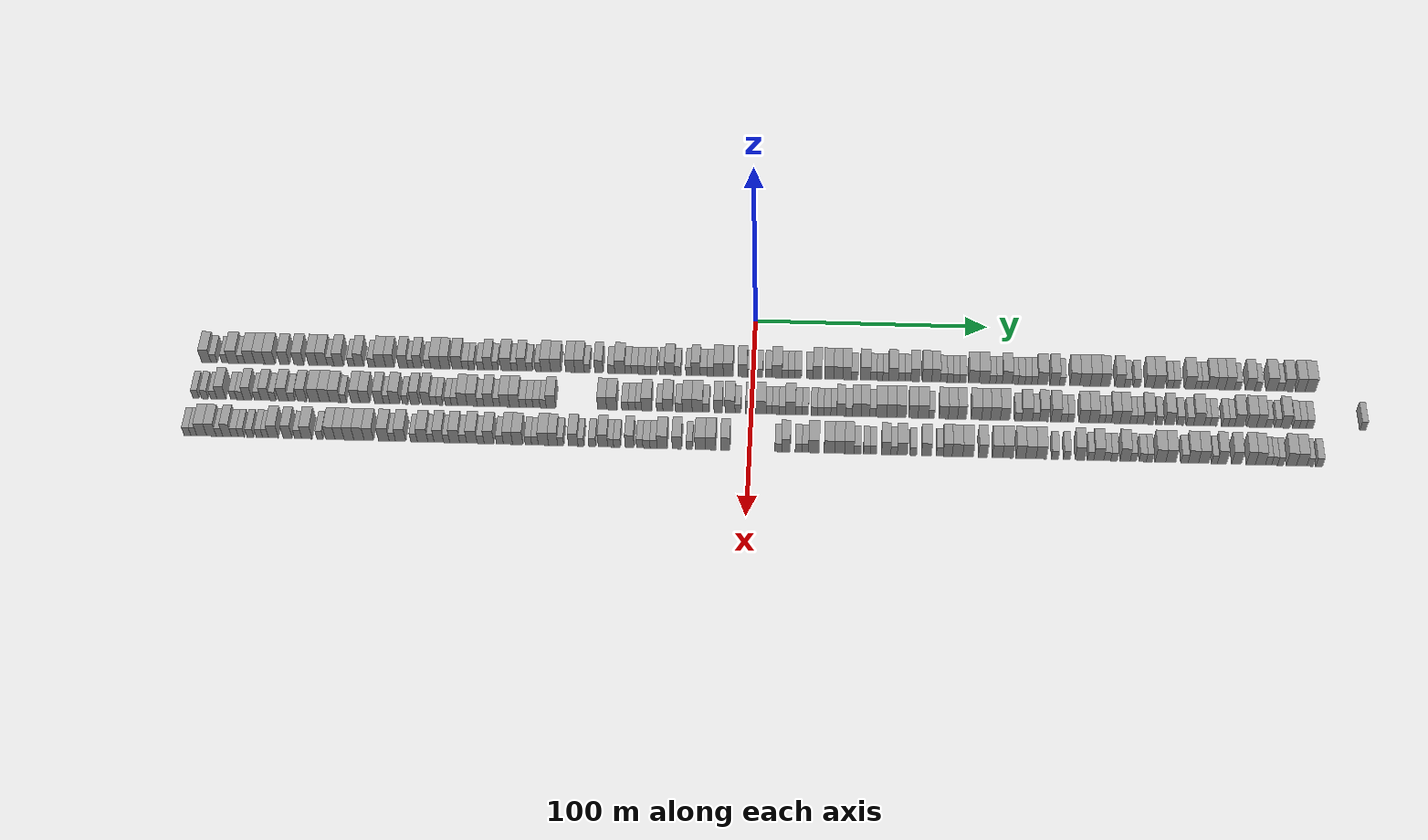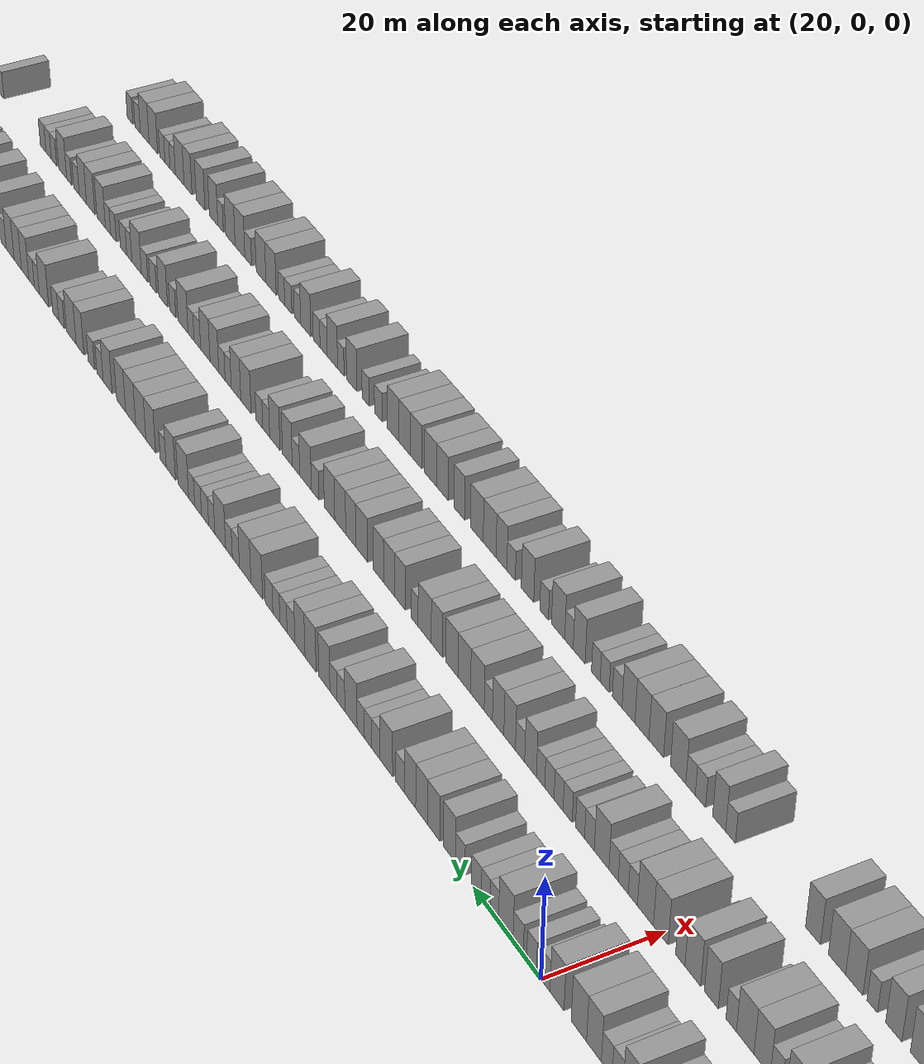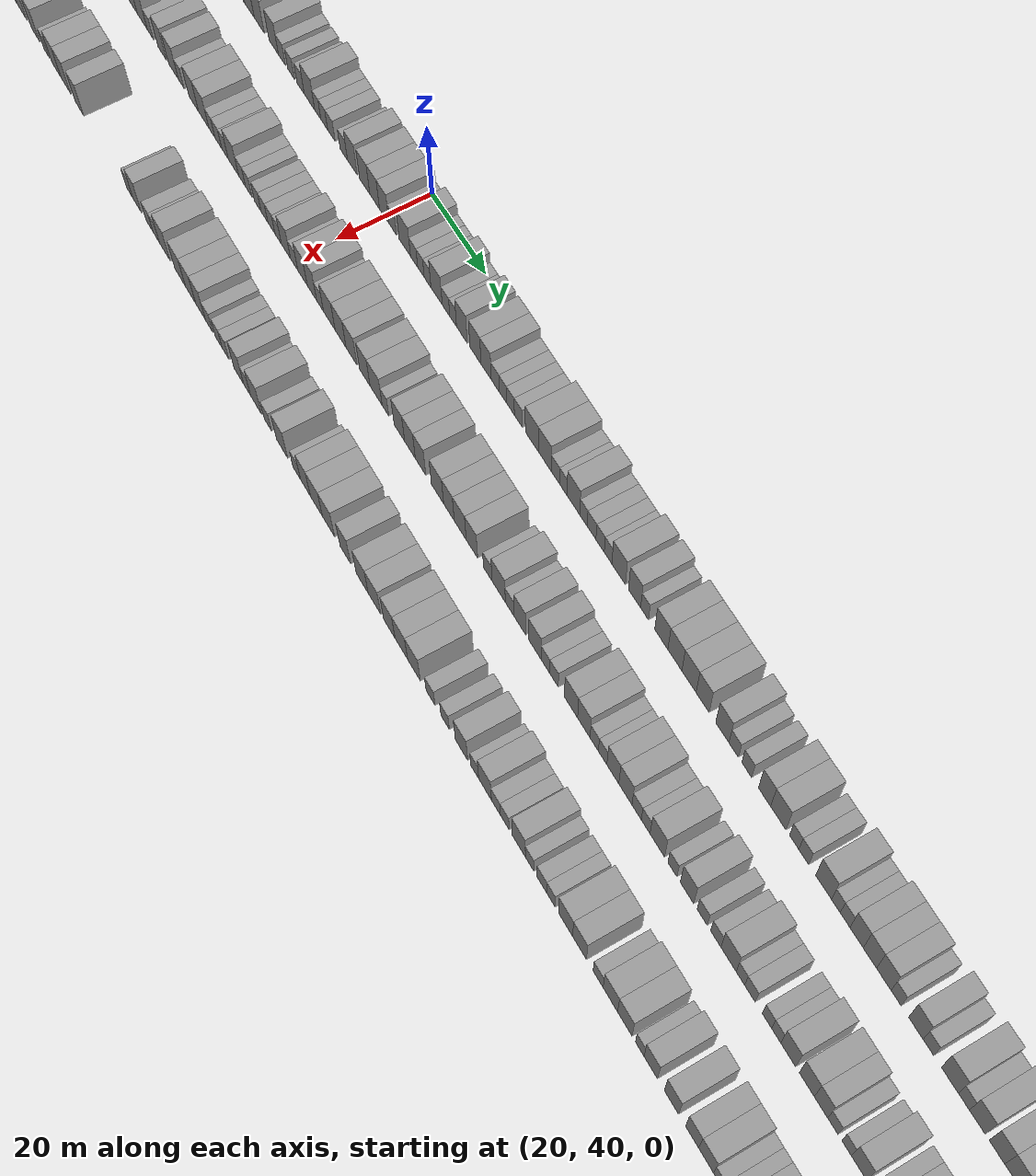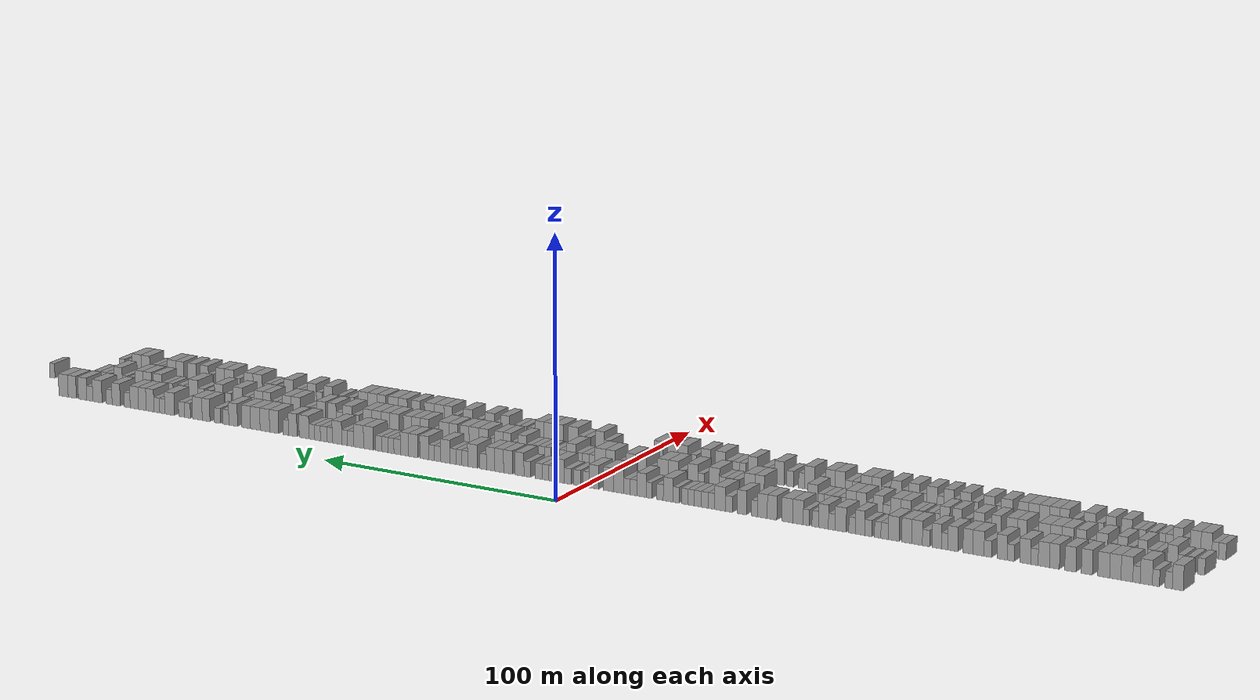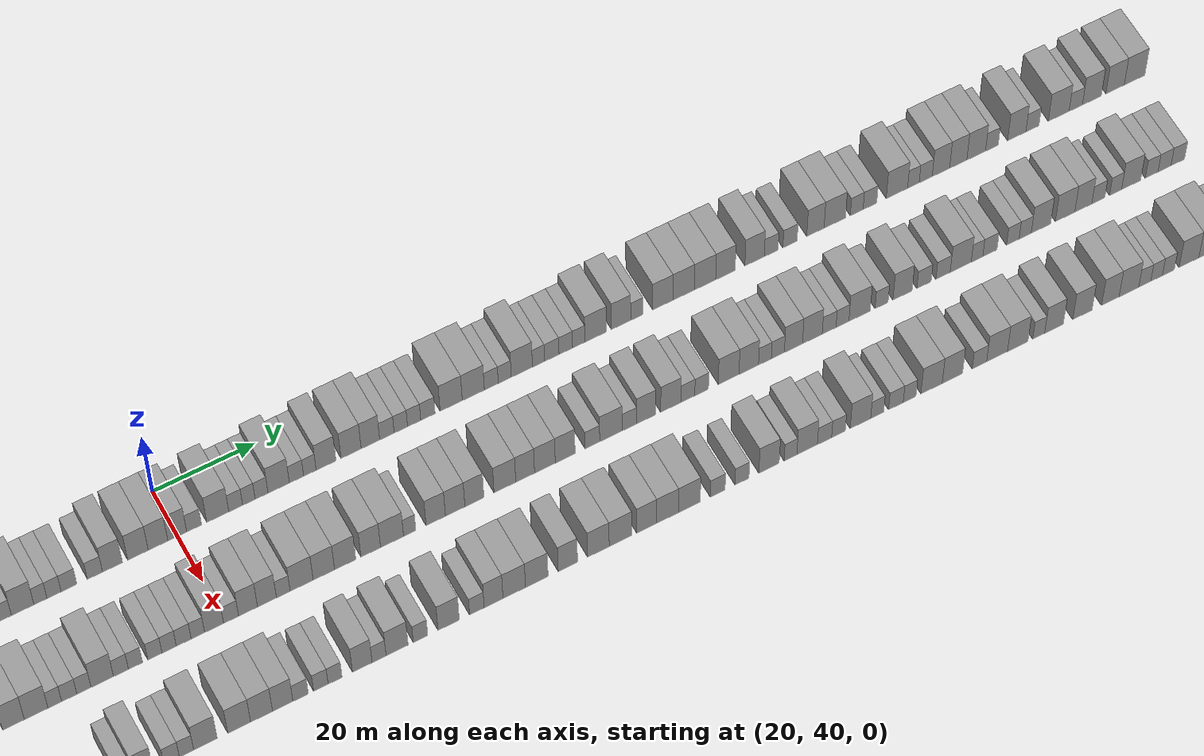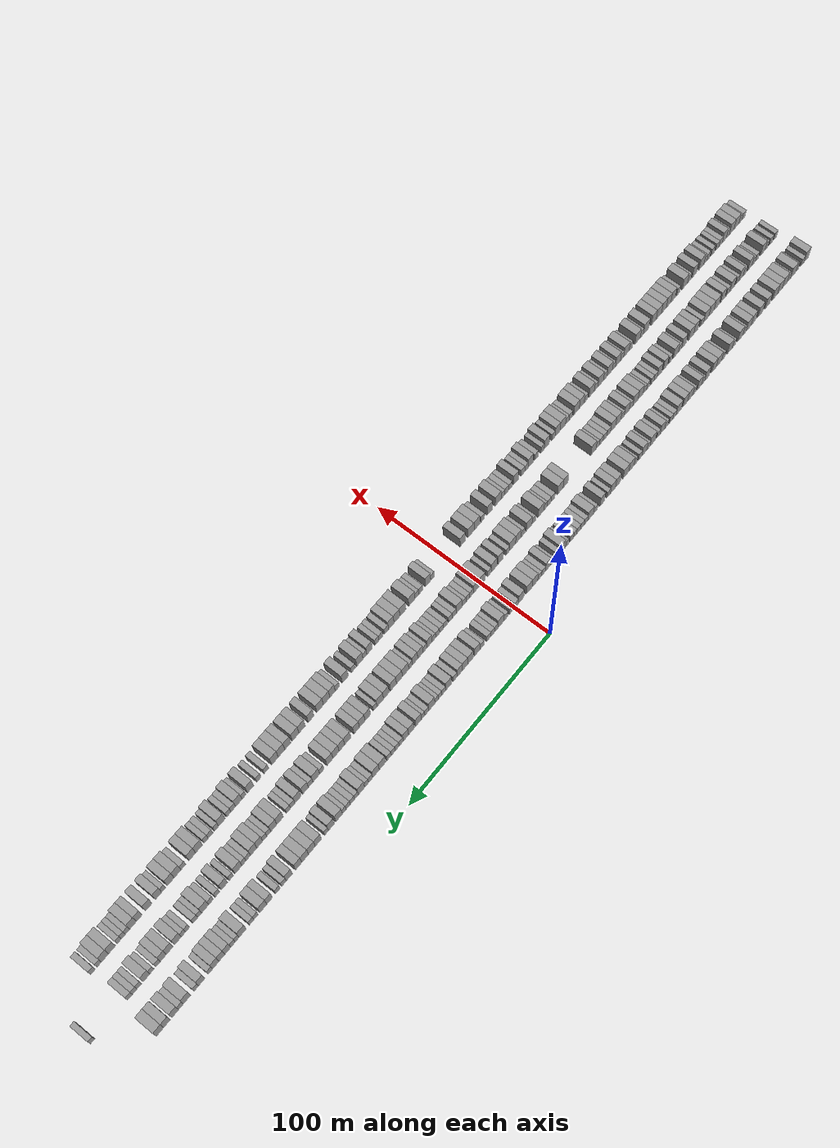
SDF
<sdf version="1.6">
 <world name="default">
  <scene>
   <sky><clouds><speed>12</speed></clouds></sky>
   <ambient>0.4 0.4 0.4 1</ambient>
   <background>0.7 0.7 0.7 1</background>
   <shadows>1</shadows>
  </scene>
  <gravity>0 0 -9.8066</gravity>
  <magnetic_field>6e-06 2.3e-05 -4.2e-05</magnetic_field>
  <physics default="0" name="default_physics" type="ode">
   <ode>
    <solver>
     <type>quick</type>
     <iters>10</iters>
     <sor>1.0</sor>
     <use_dynamic_moi_rescaling>0</use_dynamic_moi_rescaling>
    </solver>
    <constraints>
     <cfm>0</cfm>
     <erp>0.2</erp>
     <contact_max_correcting_vel>100</contact_max_correcting_vel>
     <contact_surface_layer>0.001</contact_surface_layer>
    </constraints>
   </ode>
   <max_step_size>0.004</max_step_size>
   <real_time_factor>1</real_time_factor>
   <real_time_update_rate>250</real_time_update_rate>
  </physics>
  <light name="sun" type="directional">
   <pose>0 0 10 0 0 0</pose>
   <diffuse>0.8 0.8 0.8 1</diffuse>
   <specular>0.2 0.2 0.2 1</specular>
   <attenuation>
    <range>1000</range>
    <constant>0.9</constant>
    <linear>0.01</linear>
    <quadratic>0.001</quadratic>
   </attenuation>
   <direction>-0.5 0.1 -0.9</direction>
  </light>
  <model name="building_1">
   <static>1</static>
   <pose>25.0000 -233.9836 0 0.000000 0.000000 0.000000</pose>
   <link name="link">
    <pose>0 0 4.50 0 0 0</pose>
    <collision name="collision"><geometry><box><size>10.0000 4.0328 9.0000</size></box></geometry></collision>
    <visual name="visual">
     <cast_shadows>0</cast_shadows>
     <geometry><box><size>10.0000 4.0328 9.0000</size></box></geometry>
     <material>
      <script>
       <uri>model://grey_wall/materials/scripts</uri>
       <uri>model://grey_wall/materials/textures</uri>
       <name>vrc/grey_wall</name>
      </script>
     </material>
    </visual>
   </link>
  </model>
  <model name="building_2">
   <static>1</static>
   <pose>25.0000 -230.6096 0 0.000000 0.000000 0.000000</pose>
   <link name="link">
    <pose>0 0 3.00 0 0 0</pose>
    <collision name="collision"><geometry><box><size>10.0000 2.7152 6.0000</size></box></geometry></collision>
    <visual name="visual">
     <cast_shadows>0</cast_shadows>
     <geometry><box><size>10.0000 2.7152 6.0000</size></box></geometry>
     <material>
      <script>
       <uri>model://grey_wall/materials/scripts</uri>
       <uri>model://grey_wall/materials/textures</uri>
       <name>vrc/grey_wall</name>
      </script>
     </material>
    </visual>
   </link>
  </model>
  <model name="building_3">
   <static>1</static>
   <pose>25.0000 -225.9464 0 0.000000 0.000000 0.000000</pose>
   <link name="link">
    <pose>0 0 3.00 0 0 0</pose>
    <collision name="collision"><geometry><box><size>10.0000 2.6112 6.0000</size></box></geometry></collision>
    <visual name="visual">
     <cast_shadows>0</cast_shadows>
     <geometry><box><size>10.0000 2.6112 6.0000</size></box></geometry>
     <material>
      <script>
       <uri>model://grey_wall/materials/scripts</uri>
       <uri>model://grey_wall/materials/textures</uri>
       <name>vrc/grey_wall</name>
      </script>
     </material>
    </visual>
   </link>
  </model>
  <model name="building_4">
   <static>1</static>
   <pose>25.0000 -222.4008 0 0.000000 0.000000 0.000000</pose>
   <link name="link">
    <pose>0 0 4.50 0 0 0</pose>
    <collision name="collision"><geometry><box><size>10.0000 4.4799 9.0000</size></box></geometry></collision>
    <visual name="visual">
     <cast_shadows>0</cast_shadows>
     <geometry><box><size>10.0000 4.4799 9.0000</size></box></geometry>
     <material>
      <script>
       <uri>model://grey_wall/materials/scripts</uri>
       <uri>model://grey_wall/materials/textures</uri>
       <name>vrc/grey_wall</name>
      </script>
     </material>
    </visual>
   </link>
  </model>
  <model name="building_5">
   <static>1</static>
   <pose>25.0000 -218.7899 0 0.000000 0.000000 0.000000</pose>
   <link name="link">
    <pose>0 0 3.00 0 0 0</pose>
    <collision name="collision"><geometry><box><size>10.0000 2.7420 6.0000</size></box></geometry></collision>
    <visual name="visual">
     <cast_shadows>0</cast_shadows>
     <geometry><box><size>10.0000 2.7420 6.0000</size></box></geometry>
     <material>
      <script>
       <uri>model://grey_wall/materials/scripts</uri>
       <uri>model://grey_wall/materials/textures</uri>
       <name>vrc/grey_wall</name>
      </script>
     </material>
    </visual>
   </link>
  </model>
  <model name="building_6">
   <static>1</static>
   <pose>25.0000 -215.2181 0 0.000000 0.000000 0.000000</pose>
   <link name="link">
    <pose>0 0 4.50 0 0 0</pose>
    <collision name="collision"><geometry><box><size>10.0000 4.4015 9.0000</size></box></geometry></collision>
    <visual name="visual">
     <cast_shadows>0</cast_shadows>
     <geometry><box><size>10.0000 4.4015 9.0000</size></box></geometry>
     <material>
      <script>
       <uri>model://grey_wall/materials/scripts</uri>
       <uri>model://grey_wall/materials/textures</uri>
       <name>vrc/grey_wall</name>
      </script>
     </material>
    </visual>
   </link>
  </model>
  <model name="building_7">
   <static>1</static>
   <pose>25.0000 -210.9202 0 0.000000 0.000000 0.000000</pose>
   <link name="link">
    <pose>0 0 4.50 0 0 0</pose>
    <collision name="collision"><geometry><box><size>10.0000 4.1942 9.0000</size></box></geometry></collision>
    <visual name="visual">
     <cast_shadows>0</cast_shadows>
     <geometry><box><size>10.0000 4.1942 9.0000</size></box></geometry>
     <material>
      <script>
       <uri>model://grey_wall/materials/scripts</uri>
       <uri>model://grey_wall/materials/textures</uri>
       <name>vrc/grey_wall</name>
      </script>
     </material>
    </visual>
   </link>
  </model>
  <model name="building_8">
   <static>1</static>
   <pose>25.0000 -206.6059 0 0.000000 0.000000 0.000000</pose>
   <link name="link">
    <pose>0 0 4.50 0 0 0</pose>
    <collision name="collision"><geometry><box><size>10.0000 4.4343 9.0000</size></box></geometry></collision>
    <visual name="visual">
     <cast_shadows>0</cast_shadows>
     <geometry><box><size>10.0000 4.4343 9.0000</size></box></geometry>
     <material>
      <script>
       <uri>model://grey_wall/materials/scripts</uri>
       <uri>model://grey_wall/materials/textures</uri>
       <name>vrc/grey_wall</name>
      </script>
     </material>
    </visual>
   </link>
  </model>
  <model name="building_9">
   <static>1</static>
   <pose>25.0000 -200.3135 0 0.000000 0.000000 0.000000</pose>
   <link name="link">
    <pose>0 0 4.50 0 0 0</pose>
    <collision name="collision"><geometry><box><size>10.0000 4.1505 9.0000</size></box></geometry></collision>
    <visual name="visual">
     <cast_shadows>0</cast_shadows>
     <geometry><box><size>10.0000 4.1505 9.0000</size></box></geometry>
     <material>
      <script>
       <uri>model://grey_wall/materials/scripts</uri>
       <uri>model://grey_wall/materials/textures</uri>
       <name>vrc/grey_wall</name>
      </script>
     </material>
    </visual>
   </link>
  </model>
  <model name="building_10">
   <static>1</static>
   <pose>25.0000 -194.1233 0 0.000000 0.000000 0.000000</pose>
   <link name="link">
    <pose>0 0 4.50 0 0 0</pose>
    <collision name="collision"><geometry><box><size>10.0000 4.2298 9.0000</size></box></geometry></collision>
    <visual name="visual">
     <cast_shadows>0</cast_shadows>
     <geometry><box><size>10.0000 4.2298 9.0000</size></box></geometry>
     <material>
      <script>
       <uri>model://grey_wall/materials/scripts</uri>
       <uri>model://grey_wall/materials/textures</uri>
       <name>vrc/grey_wall</name>
      </script>
     </material>
    </visual>
   </link>
  </model>
  <model name="building_11">
   <static>1</static>
   <pose>25.0000 -188.1215 0 0.000000 0.000000 0.000000</pose>
   <link name="link">
    <pose>0 0 4.50 0 0 0</pose>
    <collision name="collision"><geometry><box><size>10.0000 3.7738 9.0000</size></box></geometry></collision>
    <visual name="visual">
     <cast_shadows>0</cast_shadows>
     <geometry><box><size>10.0000 3.7738 9.0000</size></box></geometry>
     <material>
      <script>
       <uri>model://grey_wall/materials/scripts</uri>
       <uri>model://grey_wall/materials/textures</uri>
       <name>vrc/grey_wall</name>
      </script>
     </material>
    </visual>
   </link>
  </model>
  <model name="building_12">
   <static>1</static>
   <pose>25.0000 -184.0961 0 0.000000 0.000000 0.000000</pose>
   <link name="link">
    <pose>0 0 4.50 0 0 0</pose>
    <collision name="collision"><geometry><box><size>10.0000 4.2769 9.0000</size></box></geometry></collision>
    <visual name="visual">
     <cast_shadows>0</cast_shadows>
     <geometry><box><size>10.0000 4.2769 9.0000</size></box></geometry>
     <material>
      <script>
       <uri>model://grey_wall/materials/scripts</uri>
       <uri>model://grey_wall/materials/textures</uri>
       <name>vrc/grey_wall</name>
      </script>
     </material>
    </visual>
   </link>
  </model>
  <model name="building_13">
   <static>1</static>
   <pose>25.0000 -180.5495 0 0.000000 0.000000 0.000000</pose>
   <link name="link">
    <pose>0 0 3.00 0 0 0</pose>
    <collision name="collision"><geometry><box><size>10.0000 2.8164 6.0000</size></box></geometry></collision>
    <visual name="visual">
     <cast_shadows>0</cast_shadows>
     <geometry><box><size>10.0000 2.8164 6.0000</size></box></geometry>
     <material>
      <script>
       <uri>model://grey_wall/materials/scripts</uri>
       <uri>model://grey_wall/materials/textures</uri>
       <name>vrc/grey_wall</name>
      </script>
     </material>
    </visual>
   </link>
  </model>
  <model name="building_14">
   <static>1</static>
   <pose>25.0000 -177.0517 0 0.000000 0.000000 0.000000</pose>
   <link name="link">
    <pose>0 0 4.50 0 0 0</pose>
    <collision name="collision"><geometry><box><size>10.0000 4.1793 9.0000</size></box></geometry></collision>
    <visual name="visual">
     <cast_shadows>0</cast_shadows>
     <geometry><box><size>10.0000 4.1793 9.0000</size></box></geometry>
     <material>
      <script>
       <uri>model://grey_wall/materials/scripts</uri>
       <uri>model://grey_wall/materials/textures</uri>
       <name>vrc/grey_wall</name>
      </script>
     </material>
    </visual>
   </link>
  </model>
  <model name="building_15">
   <static>1</static>
   <pose>25.0000 -171.6035 0 0.000000 0.000000 0.000000</pose>
   <link name="link">
    <pose>0 0 3.00 0 0 0</pose>
    <collision name="collision"><geometry><box><size>10.0000 2.7170 6.0000</size></box></geometry></collision>
    <visual name="visual">
     <cast_shadows>0</cast_shadows>
     <geometry><box><size>10.0000 2.7170 6.0000</size></box></geometry>
     <material>
      <script>
       <uri>model://grey_wall/materials/scripts</uri>
       <uri>model://grey_wall/materials/textures</uri>
       <name>vrc/grey_wall</name>
      </script>
     </material>
    </visual>
   </link>
  </model>
  <model name="building_16">
   <static>1</static>
   <pose>25.0000 -168.2817 0 0.000000 0.000000 0.000000</pose>
   <link name="link">
    <pose>0 0 4.50 0 0 0</pose>
    <collision name="collision"><geometry><box><size>10.0000 3.9265 9.0000</size></box></geometry></collision>
    <visual name="visual">
     <cast_shadows>0</cast_shadows>
     <geometry><box><size>10.0000 3.9265 9.0000</size></box></geometry>
     <material>
      <script>
       <uri>model://grey_wall/materials/scripts</uri>
       <uri>model://grey_wall/materials/textures</uri>
       <name>vrc/grey_wall</name>
      </script>
     </material>
    </visual>
   </link>
  </model>
  <model name="building_17">
   <static>1</static>
   <pose>25.0000 -162.8379 0 0.000000 0.000000 0.000000</pose>
   <link name="link">
    <pose>0 0 3.00 0 0 0</pose>
    <collision name="collision"><geometry><box><size>10.0000 2.9611 6.0000</size></box></geometry></collision>
    <visual name="visual">
     <cast_shadows>0</cast_shadows>
     <geometry><box><size>10.0000 2.9611 6.0000</size></box></geometry>
     <material>
      <script>
       <uri>model://grey_wall/materials/scripts</uri>
       <uri>model://grey_wall/materials/textures</uri>
       <name>vrc/grey_wall</name>
      </script>
     </material>
    </visual>
   </link>
  </model>
  <model name="building_18">
   <static>1</static>
   <pose>25.0000 -159.1776 0 0.000000 0.000000 0.000000</pose>
   <link name="link">
    <pose>0 0 4.50 0 0 0</pose>
    <collision name="collision"><geometry><box><size>10.0000 4.3594 9.0000</size></box></geometry></collision>
    <visual name="visual">
     <cast_shadows>0</cast_shadows>
     <geometry><box><size>10.0000 4.3594 9.0000</size></box></geometry>
     <material>
      <script>
       <uri>model://grey_wall/materials/scripts</uri>
       <uri>model://grey_wall/materials/textures</uri>
       <name>vrc/grey_wall</name>
      </script>
     </material>
    </visual>
   </link>
  </model>
  <model name="building_19">
   <static>1</static>
   <pose>25.0000 -155.1278 0 0.000000 0.000000 0.000000</pose>
   <link name="link">
    <pose>0 0 4.50 0 0 0</pose>
    <collision name="collision"><geometry><box><size>10.0000 3.7403 9.0000</size></box></geometry></collision>
    <visual name="visual">
     <cast_shadows>0</cast_shadows>
     <geometry><box><size>10.0000 3.7403 9.0000</size></box></geometry>
     <material>
      <script>
       <uri>model://grey_wall/materials/scripts</uri>
       <uri>model://grey_wall/materials/textures</uri>
       <name>vrc/grey_wall</name>
      </script>
     </material>
    </visual>
   </link>
  </model>
  <model name="building_20">
   <static>1</static>
   <pose>25.0000 -149.3314 0 0.000000 0.000000 0.000000</pose>
   <link name="link">
    <pose>0 0 4.50 0 0 0</pose>
    <collision name="collision"><geometry><box><size>10.0000 3.8524 9.0000</size></box></geometry></collision>
    <visual name="visual">
     <cast_shadows>0</cast_shadows>
     <geometry><box><size>10.0000 3.8524 9.0000</size></box></geometry>
     <material>
      <script>
       <uri>model://grey_wall/materials/scripts</uri>
       <uri>model://grey_wall/materials/textures</uri>
       <name>vrc/grey_wall</name>
      </script>
     </material>
    </visual>
   </link>
  </model>
  <model name="building_21">
   <static>1</static>
   <pose>25.0000 -146.1760 0 0.000000 0.000000 0.000000</pose>
   <link name="link">
    <pose>0 0 3.00 0 0 0</pose>
    <collision name="collision"><geometry><box><size>10.0000 2.4586 6.0000</size></box></geometry></collision>
    <visual name="visual">
     <cast_shadows>0</cast_shadows>
     <geometry><box><size>10.0000 2.4586 6.0000</size></box></geometry>
     <material>
      <script>
       <uri>model://grey_wall/materials/scripts</uri>
       <uri>model://grey_wall/materials/textures</uri>
       <name>vrc/grey_wall</name>
      </script>
     </material>
    </visual>
   </link>
  </model>
  <model name="building_22">
   <static>1</static>
   <pose>25.0000 -143.1397 0 0.000000 0.000000 0.000000</pose>
   <link name="link">
    <pose>0 0 4.50 0 0 0</pose>
    <collision name="collision"><geometry><box><size>10.0000 3.6139 9.0000</size></box></geometry></collision>
    <visual name="visual">
     <cast_shadows>0</cast_shadows>
     <geometry><box><size>10.0000 3.6139 9.0000</size></box></geometry>
     <material>
      <script>
       <uri>model://grey_wall/materials/scripts</uri>
       <uri>model://grey_wall/materials/textures</uri>
       <name>vrc/grey_wall</name>
      </script>
     </material>
    </visual>
   </link>
  </model>
  <model name="building_23">
   <static>1</static>
   <pose>25.0000 -138.9310 0 0.000000 0.000000 0.000000</pose>
   <link name="link">
    <pose>0 0 3.00 0 0 0</pose>
    <collision name="collision"><geometry><box><size>10.0000 2.8036 6.0000</size></box></geometry></collision>
    <visual name="visual">
     <cast_shadows>0</cast_shadows>
     <geometry><box><size>10.0000 2.8036 6.0000</size></box></geometry>
     <material>
      <script>
       <uri>model://grey_wall/materials/scripts</uri>
       <uri>model://grey_wall/materials/textures</uri>
       <name>vrc/grey_wall</name>
      </script>
     </material>
    </visual>
   </link>
  </model>
  <model name="building_24">
   <static>1</static>
   <pose>25.0000 -135.4811 0 0.000000 0.000000 0.000000</pose>
   <link name="link">
    <pose>0 0 4.50 0 0 0</pose>
    <collision name="collision"><geometry><box><size>10.0000 4.0961 9.0000</size></box></geometry></collision>
    <visual name="visual">
     <cast_shadows>0</cast_shadows>
     <geometry><box><size>10.0000 4.0961 9.0000</size></box></geometry>
     <material>
      <script>
       <uri>model://grey_wall/materials/scripts</uri>
       <uri>model://grey_wall/materials/textures</uri>
       <name>vrc/grey_wall</name>
      </script>
     </material>
    </visual>
   </link>
  </model>
  <model name="building_25">
   <static>1</static>
   <pose>25.0000 -131.4556 0 0.000000 0.000000 0.000000</pose>
   <link name="link">
    <pose>0 0 4.50 0 0 0</pose>
    <collision name="collision"><geometry><box><size>10.0000 3.9550 9.0000</size></box></geometry></collision>
    <visual name="visual">
     <cast_shadows>0</cast_shadows>
     <geometry><box><size>10.0000 3.9550 9.0000</size></box></geometry>
     <material>
      <script>
       <uri>model://grey_wall/materials/scripts</uri>
       <uri>model://grey_wall/materials/textures</uri>
       <name>vrc/grey_wall</name>
      </script>
     </material>
    </visual>
   </link>
  </model>
  <model name="building_26">
   <static>1</static>
   <pose>25.0000 -126.3075 0 0.000000 0.000000 0.000000</pose>
   <link name="link">
    <pose>0 0 4.50 0 0 0</pose>
    <collision name="collision"><geometry><box><size>10.0000 4.3412 9.0000</size></box></geometry></collision>
    <visual name="visual">
     <cast_shadows>0</cast_shadows>
     <geometry><box><size>10.0000 4.3412 9.0000</size></box></geometry>
     <material>
      <script>
       <uri>model://grey_wall/materials/scripts</uri>
       <uri>model://grey_wall/materials/textures</uri>
       <name>vrc/grey_wall</name>
      </script>
     </material>
    </visual>
   </link>
  </model>
  <model name="building_27">
   <static>1</static>
   <pose>25.0000 -122.7158 0 0.000000 0.000000 0.000000</pose>
   <link name="link">
    <pose>0 0 3.00 0 0 0</pose>
    <collision name="collision"><geometry><box><size>10.0000 2.8422 6.0000</size></box></geometry></collision>
    <visual name="visual">
     <cast_shadows>0</cast_shadows>
     <geometry><box><size>10.0000 2.8422 6.0000</size></box></geometry>
     <material>
      <script>
       <uri>model://grey_wall/materials/scripts</uri>
       <uri>model://grey_wall/materials/textures</uri>
       <name>vrc/grey_wall</name>
      </script>
     </material>
    </visual>
   </link>
  </model>
  <model name="building_28">
   <static>1</static>
   <pose>25.0000 -120.0537 0 0.000000 0.000000 0.000000</pose>
   <link name="link">
    <pose>0 0 3.00 0 0 0</pose>
    <collision name="collision"><geometry><box><size>10.0000 2.4821 6.0000</size></box></geometry></collision>
    <visual name="visual">
     <cast_shadows>0</cast_shadows>
     <geometry><box><size>10.0000 2.4821 6.0000</size></box></geometry>
     <material>
      <script>
       <uri>model://grey_wall/materials/scripts</uri>
       <uri>model://grey_wall/materials/textures</uri>
       <name>vrc/grey_wall</name>
      </script>
     </material>
    </visual>
   </link>
  </model>
  <model name="building_29">
   <static>1</static>
   <pose>25.0000 -116.3490 0 0.000000 0.000000 0.000000</pose>
   <link name="link">
    <pose>0 0 3.00 0 0 0</pose>
    <collision name="collision"><geometry><box><size>10.0000 2.9272 6.0000</size></box></geometry></collision>
    <visual name="visual">
     <cast_shadows>0</cast_shadows>
     <geometry><box><size>10.0000 2.9272 6.0000</size></box></geometry>
     <material>
      <script>
       <uri>model://grey_wall/materials/scripts</uri>
       <uri>model://grey_wall/materials/textures</uri>
       <name>vrc/grey_wall</name>
      </script>
     </material>
    </visual>
   </link>
  </model>
  <model name="building_30">
   <static>1</static>
   <pose>25.0000 -113.0159 0 0.000000 0.000000 0.000000</pose>
   <link name="link">
    <pose>0 0 4.50 0 0 0</pose>
    <collision name="collision"><geometry><box><size>10.0000 3.7389 9.0000</size></box></geometry></collision>
    <visual name="visual">
     <cast_shadows>0</cast_shadows>
     <geometry><box><size>10.0000 3.7389 9.0000</size></box></geometry>
     <material>
      <script>
       <uri>model://grey_wall/materials/scripts</uri>
       <uri>model://grey_wall/materials/textures</uri>
       <name>vrc/grey_wall</name>
      </script>
     </material>
    </visual>
   </link>
  </model>
  <model name="building_31">
   <static>1</static>
   <pose>25.0000 -109.8882 0 0.000000 0.000000 0.000000</pose>
   <link name="link">
    <pose>0 0 3.00 0 0 0</pose>
    <collision name="collision"><geometry><box><size>10.0000 2.5166 6.0000</size></box></geometry></collision>
    <visual name="visual">
     <cast_shadows>0</cast_shadows>
     <geometry><box><size>10.0000 2.5166 6.0000</size></box></geometry>
     <material>
      <script>
       <uri>model://grey_wall/materials/scripts</uri>
       <uri>model://grey_wall/materials/textures</uri>
       <name>vrc/grey_wall</name>
      </script>
     </material>
    </visual>
   </link>
  </model>
  <model name="building_32">
   <static>1</static>
   <pose>25.0000 -105.3894 0 0.000000 0.000000 0.000000</pose>
   <link name="link">
    <pose>0 0 4.50 0 0 0</pose>
    <collision name="collision"><geometry><box><size>10.0000 4.4808 9.0000</size></box></geometry></collision>
    <visual name="visual">
     <cast_shadows>0</cast_shadows>
     <geometry><box><size>10.0000 4.4808 9.0000</size></box></geometry>
     <material>
      <script>
       <uri>model://grey_wall/materials/scripts</uri>
       <uri>model://grey_wall/materials/textures</uri>
       <name>vrc/grey_wall</name>
      </script>
     </material>
    </visual>
   </link>
  </model>
  <model name="building_33">
   <static>1</static>
   <pose>25.0000 -101.8352 0 0.000000 0.000000 0.000000</pose>
   <link name="link">
    <pose>0 0 3.00 0 0 0</pose>
    <collision name="collision"><geometry><box><size>10.0000 2.6276 6.0000</size></box></geometry></collision>
    <visual name="visual">
     <cast_shadows>0</cast_shadows>
     <geometry><box><size>10.0000 2.6276 6.0000</size></box></geometry>
     <material>
      <script>
       <uri>model://grey_wall/materials/scripts</uri>
       <uri>model://grey_wall/materials/textures</uri>
       <name>vrc/grey_wall</name>
      </script>
     </material>
    </visual>
   </link>
  </model>
  <model name="building_34">
   <static>1</static>
   <pose>25.0000 -98.6064 0 0.000000 0.000000 0.000000</pose>
   <link name="link">
    <pose>0 0 4.50 0 0 0</pose>
    <collision name="collision"><geometry><box><size>10.0000 3.8301 9.0000</size></box></geometry></collision>
    <visual name="visual">
     <cast_shadows>0</cast_shadows>
     <geometry><box><size>10.0000 3.8301 9.0000</size></box></geometry>
     <material>
      <script>
       <uri>model://grey_wall/materials/scripts</uri>
       <uri>model://grey_wall/materials/textures</uri>
       <name>vrc/grey_wall</name>
      </script>
     </material>
    </visual>
   </link>
  </model>
  <model name="building_35">
   <static>1</static>
   <pose>25.0000 -95.3364 0 0.000000 0.000000 0.000000</pose>
   <link name="link">
    <pose>0 0 3.00 0 0 0</pose>
    <collision name="collision"><geometry><box><size>10.0000 2.7099 6.0000</size></box></geometry></collision>
    <visual name="visual">
     <cast_shadows>0</cast_shadows>
     <geometry><box><size>10.0000 2.7099 6.0000</size></box></geometry>
     <material>
      <script>
       <uri>model://grey_wall/materials/scripts</uri>
       <uri>model://grey_wall/materials/textures</uri>
       <name>vrc/grey_wall</name>
      </script>
     </material>
    </visual>
   </link>
  </model>
  <model name="building_36">
   <static>1</static>
   <pose>25.0000 -91.7302 0 0.000000 0.000000 0.000000</pose>
   <link name="link">
    <pose>0 0 3.00 0 0 0</pose>
    <collision name="collision"><geometry><box><size>10.0000 2.5024 6.0000</size></box></geometry></collision>
    <visual name="visual">
     <cast_shadows>0</cast_shadows>
     <geometry><box><size>10.0000 2.5024 6.0000</size></box></geometry>
     <material>
      <script>
       <uri>model://grey_wall/materials/scripts</uri>
       <uri>model://grey_wall/materials/textures</uri>
       <name>vrc/grey_wall</name>
      </script>
     </material>
    </visual>
   </link>
  </model>
  <model name="building_37">
   <static>1</static>
   <pose>25.0000 -88.4005 0 0.000000 0.000000 0.000000</pose>
   <link name="link">
    <pose>0 0 4.50 0 0 0</pose>
    <collision name="collision"><geometry><box><size>10.0000 4.1570 9.0000</size></box></geometry></collision>
    <visual name="visual">
     <cast_shadows>0</cast_shadows>
     <geometry><box><size>10.0000 4.1570 9.0000</size></box></geometry>
     <material>
      <script>
       <uri>model://grey_wall/materials/scripts</uri>
       <uri>model://grey_wall/materials/textures</uri>
       <name>vrc/grey_wall</name>
      </script>
     </material>
    </visual>
   </link>
  </model>
  <model name="building_38">
   <static>1</static>
   <pose>25.0000 -84.0828 0 0.000000 0.000000 0.000000</pose>
   <link name="link">
    <pose>0 0 4.50 0 0 0</pose>
    <collision name="collision"><geometry><box><size>10.0000 4.4784 9.0000</size></box></geometry></collision>
    <visual name="visual">
     <cast_shadows>0</cast_shadows>
     <geometry><box><size>10.0000 4.4784 9.0000</size></box></geometry>
     <material>
      <script>
       <uri>model://grey_wall/materials/scripts</uri>
       <uri>model://grey_wall/materials/textures</uri>
       <name>vrc/grey_wall</name>
      </script>
     </material>
    </visual>
   </link>
  </model>
  <model name="building_39">
   <static>1</static>
   <pose>25.0000 -77.9146 0 0.000000 0.000000 0.000000</pose>
   <link name="link">
    <pose>0 0 4.50 0 0 0</pose>
    <collision name="collision"><geometry><box><size>10.0000 3.8579 9.0000</size></box></geometry></collision>
    <visual name="visual">
     <cast_shadows>0</cast_shadows>
     <geometry><box><size>10.0000 3.8579 9.0000</size></box></geometry>
     <material>
      <script>
       <uri>model://grey_wall/materials/scripts</uri>
       <uri>model://grey_wall/materials/textures</uri>
       <name>vrc/grey_wall</name>
      </script>
     </material>
    </visual>
   </link>
  </model>
  <model name="building_40">
   <static>1</static>
   <pose>25.0000 -73.9750 0 0.000000 0.000000 0.000000</pose>
   <link name="link">
    <pose>0 0 4.50 0 0 0</pose>
    <collision name="collision"><geometry><box><size>10.0000 4.0212 9.0000</size></box></geometry></collision>
    <visual name="visual">
     <cast_shadows>0</cast_shadows>
     <geometry><box><size>10.0000 4.0212 9.0000</size></box></geometry>
     <material>
      <script>
       <uri>model://grey_wall/materials/scripts</uri>
       <uri>model://grey_wall/materials/textures</uri>
       <name>vrc/grey_wall</name>
      </script>
     </material>
    </visual>
   </link>
  </model>
  <model name="building_41">
   <static>1</static>
   <pose>25.0000 -70.7265 0 0.000000 0.000000 0.000000</pose>
   <link name="link">
    <pose>0 0 3.00 0 0 0</pose>
    <collision name="collision"><geometry><box><size>10.0000 2.4758 6.0000</size></box></geometry></collision>
    <visual name="visual">
     <cast_shadows>0</cast_shadows>
     <geometry><box><size>10.0000 2.4758 6.0000</size></box></geometry>
     <material>
      <script>
       <uri>model://grey_wall/materials/scripts</uri>
       <uri>model://grey_wall/materials/textures</uri>
       <name>vrc/grey_wall</name>
      </script>
     </material>
    </visual>
   </link>
  </model>
  <model name="building_42">
   <static>1</static>
   <pose>25.0000 -65.6878 0 0.000000 0.000000 0.000000</pose>
   <link name="link">
    <pose>0 0 4.50 0 0 0</pose>
    <collision name="collision"><geometry><box><size>10.0000 3.6017 9.0000</size></box></geometry></collision>
    <visual name="visual">
     <cast_shadows>0</cast_shadows>
     <geometry><box><size>10.0000 3.6017 9.0000</size></box></geometry>
     <material>
      <script>
       <uri>model://grey_wall/materials/scripts</uri>
       <uri>model://grey_wall/materials/textures</uri>
       <name>vrc/grey_wall</name>
      </script>
     </material>
    </visual>
   </link>
  </model>
  <model name="building_43">
   <static>1</static>
   <pose>25.0000 -60.4096 0 0.000000 0.000000 0.000000</pose>
   <link name="link">
    <pose>0 0 3.00 0 0 0</pose>
    <collision name="collision"><geometry><box><size>10.0000 2.9546 6.0000</size></box></geometry></collision>
    <visual name="visual">
     <cast_shadows>0</cast_shadows>
     <geometry><box><size>10.0000 2.9546 6.0000</size></box></geometry>
     <material>
      <script>
       <uri>model://grey_wall/materials/scripts</uri>
       <uri>model://grey_wall/materials/textures</uri>
       <name>vrc/grey_wall</name>
      </script>
     </material>
    </visual>
   </link>
  </model>
  <model name="building_44">
   <static>1</static>
   <pose>25.0000 -56.7264 0 0.000000 0.000000 0.000000</pose>
   <link name="link">
    <pose>0 0 4.50 0 0 0</pose>
    <collision name="collision"><geometry><box><size>10.0000 4.4117 9.0000</size></box></geometry></collision>
    <visual name="visual">
     <cast_shadows>0</cast_shadows>
     <geometry><box><size>10.0000 4.4117 9.0000</size></box></geometry>
     <material>
      <script>
       <uri>model://grey_wall/materials/scripts</uri>
       <uri>model://grey_wall/materials/textures</uri>
       <name>vrc/grey_wall</name>
      </script>
     </material>
    </visual>
   </link>
  </model>
  <model name="building_45">
   <static>1</static>
   <pose>25.0000 -53.2146 0 0.000000 0.000000 0.000000</pose>
   <link name="link">
    <pose>0 0 3.00 0 0 0</pose>
    <collision name="collision"><geometry><box><size>10.0000 2.6120 6.0000</size></box></geometry></collision>
    <visual name="visual">
     <cast_shadows>0</cast_shadows>
     <geometry><box><size>10.0000 2.6120 6.0000</size></box></geometry>
     <material>
      <script>
       <uri>model://grey_wall/materials/scripts</uri>
       <uri>model://grey_wall/materials/textures</uri>
       <name>vrc/grey_wall</name>
      </script>
     </material>
    </visual>
   </link>
  </model>
  <model name="building_46">
   <static>1</static>
   <pose>25.0000 -50.4866 0 0.000000 0.000000 0.000000</pose>
   <link name="link">
    <pose>0 0 3.00 0 0 0</pose>
    <collision name="collision"><geometry><box><size>10.0000 2.8438 6.0000</size></box></geometry></collision>
    <visual name="visual">
     <cast_shadows>0</cast_shadows>
     <geometry><box><size>10.0000 2.8438 6.0000</size></box></geometry>
     <material>
      <script>
       <uri>model://grey_wall/materials/scripts</uri>
       <uri>model://grey_wall/materials/textures</uri>
       <name>vrc/grey_wall</name>
      </script>
     </material>
    </visual>
   </link>
  </model>
  <model name="building_47">
   <static>1</static>
   <pose>25.0000 -47.5885 0 0.000000 0.000000 0.000000</pose>
   <link name="link">
    <pose>0 0 3.00 0 0 0</pose>
    <collision name="collision"><geometry><box><size>10.0000 2.9524 6.0000</size></box></geometry></collision>
    <visual name="visual">
     <cast_shadows>0</cast_shadows>
     <geometry><box><size>10.0000 2.9524 6.0000</size></box></geometry>
     <material>
      <script>
       <uri>model://grey_wall/materials/scripts</uri>
       <uri>model://grey_wall/materials/textures</uri>
       <name>vrc/grey_wall</name>
      </script>
     </material>
    </visual>
   </link>
  </model>
  <model name="building_48">
   <static>1</static>
   <pose>25.0000 -44.8904 0 0.000000 0.000000 0.000000</pose>
   <link name="link">
    <pose>0 0 3.00 0 0 0</pose>
    <collision name="collision"><geometry><box><size>10.0000 2.4438 6.0000</size></box></geometry></collision>
    <visual name="visual">
     <cast_shadows>0</cast_shadows>
     <geometry><box><size>10.0000 2.4438 6.0000</size></box></geometry>
     <material>
      <script>
       <uri>model://grey_wall/materials/scripts</uri>
       <uri>model://grey_wall/materials/textures</uri>
       <name>vrc/grey_wall</name>
      </script>
     </material>
    </visual>
   </link>
  </model>
  <model name="building_49">
   <static>1</static>
   <pose>25.0000 -42.3016 0 0.000000 0.000000 0.000000</pose>
   <link name="link">
    <pose>0 0 3.00 0 0 0</pose>
    <collision name="collision"><geometry><box><size>10.0000 2.7338 6.0000</size></box></geometry></collision>
    <visual name="visual">
     <cast_shadows>0</cast_shadows>
     <geometry><box><size>10.0000 2.7338 6.0000</size></box></geometry>
     <material>
      <script>
       <uri>model://grey_wall/materials/scripts</uri>
       <uri>model://grey_wall/materials/textures</uri>
       <name>vrc/grey_wall</name>
      </script>
     </material>
    </visual>
   </link>
  </model>
  <model name="building_50">
   <static>1</static>
   <pose>25.0000 -38.7291 0 0.000000 0.000000 0.000000</pose>
   <link name="link">
    <pose>0 0 3.00 0 0 0</pose>
    <collision name="collision"><geometry><box><size>10.0000 2.4113 6.0000</size></box></geometry></collision>
    <visual name="visual">
     <cast_shadows>0</cast_shadows>
     <geometry><box><size>10.0000 2.4113 6.0000</size></box></geometry>
     <material>
      <script>
       <uri>model://grey_wall/materials/scripts</uri>
       <uri>model://grey_wall/materials/textures</uri>
       <name>vrc/grey_wall</name>
      </script>
     </material>
    </visual>
   </link>
  </model>
  <model name="building_51">
   <static>1</static>
   <pose>25.0000 -35.4437 0 0.000000 0.000000 0.000000</pose>
   <link name="link">
    <pose>0 0 4.50 0 0 0</pose>
    <collision name="collision"><geometry><box><size>10.0000 4.1597 9.0000</size></box></geometry></collision>
    <visual name="visual">
     <cast_shadows>0</cast_shadows>
     <geometry><box><size>10.0000 4.1597 9.0000</size></box></geometry>
     <material>
      <script>
       <uri>model://grey_wall/materials/scripts</uri>
       <uri>model://grey_wall/materials/textures</uri>
       <name>vrc/grey_wall</name>
      </script>
     </material>
    </visual>
   </link>
  </model>
  <model name="building_52">
   <static>1</static>
   <pose>25.0000 -32.0028 0 0.000000 0.000000 0.000000</pose>
   <link name="link">
    <pose>0 0 3.00 0 0 0</pose>
    <collision name="collision"><geometry><box><size>10.0000 2.7220 6.0000</size></box></geometry></collision>
    <visual name="visual">
     <cast_shadows>0</cast_shadows>
     <geometry><box><size>10.0000 2.7220 6.0000</size></box></geometry>
     <material>
      <script>
       <uri>model://grey_wall/materials/scripts</uri>
       <uri>model://grey_wall/materials/textures</uri>
       <name>vrc/grey_wall</name>
      </script>
     </material>
    </visual>
   </link>
  </model>
  <model name="building_53">
   <static>1</static>
   <pose>25.0000 -27.4361 0 0.000000 0.000000 0.000000</pose>
   <link name="link">
    <pose>0 0 3.00 0 0 0</pose>
    <collision name="collision"><geometry><box><size>10.0000 2.4115 6.0000</size></box></geometry></collision>
    <visual name="visual">
     <cast_shadows>0</cast_shadows>
     <geometry><box><size>10.0000 2.4115 6.0000</size></box></geometry>
     <material>
      <script>
       <uri>model://grey_wall/materials/scripts</uri>
       <uri>model://grey_wall/materials/textures</uri>
       <name>vrc/grey_wall</name>
      </script>
     </material>
    </visual>
   </link>
  </model>
  <model name="building_54">
   <static>1</static>
   <pose>25.0000 -24.3653 0 0.000000 0.000000 0.000000</pose>
   <link name="link">
    <pose>0 0 4.50 0 0 0</pose>
    <collision name="collision"><geometry><box><size>10.0000 3.7300 9.0000</size></box></geometry></collision>
    <visual name="visual">
     <cast_shadows>0</cast_shadows>
     <geometry><box><size>10.0000 3.7300 9.0000</size></box></geometry>
     <material>
      <script>
       <uri>model://grey_wall/materials/scripts</uri>
       <uri>model://grey_wall/materials/textures</uri>
       <name>vrc/grey_wall</name>
      </script>
     </material>
    </visual>
   </link>
  </model>
  <model name="building_55">
   <static>1</static>
   <pose>25.0000 -21.0583 0 0.000000 0.000000 0.000000</pose>
   <link name="link">
    <pose>0 0 3.00 0 0 0</pose>
    <collision name="collision"><geometry><box><size>10.0000 2.8840 6.0000</size></box></geometry></collision>
    <visual name="visual">
     <cast_shadows>0</cast_shadows>
     <geometry><box><size>10.0000 2.8840 6.0000</size></box></geometry>
     <material>
      <script>
       <uri>model://grey_wall/materials/scripts</uri>
       <uri>model://grey_wall/materials/textures</uri>
       <name>vrc/grey_wall</name>
      </script>
     </material>
    </visual>
   </link>
  </model>
  <model name="building_56">
   <static>1</static>
   <pose>25.0000 -18.1659 0 0.000000 0.000000 0.000000</pose>
   <link name="link">
    <pose>0 0 3.00 0 0 0</pose>
    <collision name="collision"><geometry><box><size>10.0000 2.9008 6.0000</size></box></geometry></collision>
    <visual name="visual">
     <cast_shadows>0</cast_shadows>
     <geometry><box><size>10.0000 2.9008 6.0000</size></box></geometry>
     <material>
      <script>
       <uri>model://grey_wall/materials/scripts</uri>
       <uri>model://grey_wall/materials/textures</uri>
       <name>vrc/grey_wall</name>
      </script>
     </material>
    </visual>
   </link>
  </model>
  <model name="building_57">
   <static>1</static>
   <pose>25.0000 -14.7046 0 0.000000 0.000000 0.000000</pose>
   <link name="link">
    <pose>0 0 4.50 0 0 0</pose>
    <collision name="collision"><geometry><box><size>10.0000 4.0219 9.0000</size></box></geometry></collision>
    <visual name="visual">
     <cast_shadows>0</cast_shadows>
     <geometry><box><size>10.0000 4.0219 9.0000</size></box></geometry>
     <material>
      <script>
       <uri>model://grey_wall/materials/scripts</uri>
       <uri>model://grey_wall/materials/textures</uri>
       <name>vrc/grey_wall</name>
      </script>
     </material>
    </visual>
   </link>
  </model>
  <model name="building_58">
   <static>1</static>
   <pose>25.0000 -10.5732 0 0.000000 0.000000 0.000000</pose>
   <link name="link">
    <pose>0 0 4.50 0 0 0</pose>
    <collision name="collision"><geometry><box><size>10.0000 4.2408 9.0000</size></box></geometry></collision>
    <visual name="visual">
     <cast_shadows>0</cast_shadows>
     <geometry><box><size>10.0000 4.2408 9.0000</size></box></geometry>
     <material>
      <script>
       <uri>model://grey_wall/materials/scripts</uri>
       <uri>model://grey_wall/materials/textures</uri>
       <name>vrc/grey_wall</name>
      </script>
     </material>
    </visual>
   </link>
  </model>
  <model name="building_59">
   <static>1</static>
   <pose>25.0000 -4.4841 0 0.000000 0.000000 0.000000</pose>
   <link name="link">
    <pose>0 0 4.50 0 0 0</pose>
    <collision name="collision"><geometry><box><size>10.0000 3.9374 9.0000</size></box></geometry></collision>
    <visual name="visual">
     <cast_shadows>0</cast_shadows>
     <geometry><box><size>10.0000 3.9374 9.0000</size></box></geometry>
     <material>
      <script>
       <uri>model://grey_wall/materials/scripts</uri>
       <uri>model://grey_wall/materials/textures</uri>
       <name>vrc/grey_wall</name>
      </script>
     </material>
    </visual>
   </link>
  </model>
  <model name="building_60">
   <static>1</static>
   <pose>25.0000 -1.0660 0 0.000000 0.000000 0.000000</pose>
   <link name="link">
    <pose>0 0 3.00 0 0 0</pose>
    <collision name="collision"><geometry><box><size>10.0000 2.8988 6.0000</size></box></geometry></collision>
    <visual name="visual">
     <cast_shadows>0</cast_shadows>
     <geometry><box><size>10.0000 2.8988 6.0000</size></box></geometry>
     <material>
      <script>
       <uri>model://grey_wall/materials/scripts</uri>
       <uri>model://grey_wall/materials/textures</uri>
       <name>vrc/grey_wall</name>
      </script>
     </material>
    </visual>
   </link>
  </model>
  <model name="building_61">
   <static>1</static>
   <pose>25.0000 2.7797 0 0.000000 0.000000 0.000000</pose>
   <link name="link">
    <pose>0 0 3.00 0 0 0</pose>
    <collision name="collision"><geometry><box><size>10.0000 2.7926 6.0000</size></box></geometry></collision>
    <visual name="visual">
     <cast_shadows>0</cast_shadows>
     <geometry><box><size>10.0000 2.7926 6.0000</size></box></geometry>
     <material>
      <script>
       <uri>model://grey_wall/materials/scripts</uri>
       <uri>model://grey_wall/materials/textures</uri>
       <name>vrc/grey_wall</name>
      </script>
     </material>
    </visual>
   </link>
  </model>
  <model name="building_62">
   <static>1</static>
   <pose>25.0000 6.6664 0 0.000000 0.000000 0.000000</pose>
   <link name="link">
    <pose>0 0 3.00 0 0 0</pose>
    <collision name="collision"><geometry><box><size>10.0000 2.9809 6.0000</size></box></geometry></collision>
    <visual name="visual">
     <cast_shadows>0</cast_shadows>
     <geometry><box><size>10.0000 2.9809 6.0000</size></box></geometry>
     <material>
      <script>
       <uri>model://grey_wall/materials/scripts</uri>
       <uri>model://grey_wall/materials/textures</uri>
       <name>vrc/grey_wall</name>
      </script>
     </material>
    </visual>
   </link>
  </model>
  <model name="building_63">
   <static>1</static>
   <pose>25.0000 10.2936 0 0.000000 0.000000 0.000000</pose>
   <link name="link">
    <pose>0 0 4.50 0 0 0</pose>
    <collision name="collision"><geometry><box><size>10.0000 4.2736 9.0000</size></box></geometry></collision>
    <visual name="visual">
     <cast_shadows>0</cast_shadows>
     <geometry><box><size>10.0000 4.2736 9.0000</size></box></geometry>
     <material>
      <script>
       <uri>model://grey_wall/materials/scripts</uri>
       <uri>model://grey_wall/materials/textures</uri>
       <name>vrc/grey_wall</name>
      </script>
     </material>
    </visual>
   </link>
  </model>
  <model name="building_64">
   <static>1</static>
   <pose>25.0000 13.6749 0 0.000000 0.000000 0.000000</pose>
   <link name="link">
    <pose>0 0 3.00 0 0 0</pose>
    <collision name="collision"><geometry><box><size>10.0000 2.4890 6.0000</size></box></geometry></collision>
    <visual name="visual">
     <cast_shadows>0</cast_shadows>
     <geometry><box><size>10.0000 2.4890 6.0000</size></box></geometry>
     <material>
      <script>
       <uri>model://grey_wall/materials/scripts</uri>
       <uri>model://grey_wall/materials/textures</uri>
       <name>vrc/grey_wall</name>
      </script>
     </material>
    </visual>
   </link>
  </model>
  <model name="building_65">
   <static>1</static>
   <pose>25.0000 16.2699 0 0.000000 0.000000 0.000000</pose>
   <link name="link">
    <pose>0 0 3.00 0 0 0</pose>
    <collision name="collision"><geometry><box><size>10.0000 2.7009 6.0000</size></box></geometry></collision>
    <visual name="visual">
     <cast_shadows>0</cast_shadows>
     <geometry><box><size>10.0000 2.7009 6.0000</size></box></geometry>
     <material>
      <script>
       <uri>model://grey_wall/materials/scripts</uri>
       <uri>model://grey_wall/materials/textures</uri>
       <name>vrc/grey_wall</name>
      </script>
     </material>
    </visual>
   </link>
  </model>
  <model name="building_66">
   <static>1</static>
   <pose>25.0000 19.1159 0 0.000000 0.000000 0.000000</pose>
   <link name="link">
    <pose>0 0 3.00 0 0 0</pose>
    <collision name="collision"><geometry><box><size>10.0000 2.9912 6.0000</size></box></geometry></collision>
    <visual name="visual">
     <cast_shadows>0</cast_shadows>
     <geometry><box><size>10.0000 2.9912 6.0000</size></box></geometry>
     <material>
      <script>
       <uri>model://grey_wall/materials/scripts</uri>
       <uri>model://grey_wall/materials/textures</uri>
       <name>vrc/grey_wall</name>
      </script>
     </material>
    </visual>
   </link>
  </model>
  <model name="building_67">
   <static>1</static>
   <pose>25.0000 24.0686 0 0.000000 0.000000 0.000000</pose>
   <link name="link">
    <pose>0 0 3.00 0 0 0</pose>
    <collision name="collision"><geometry><box><size>10.0000 2.9142 6.0000</size></box></geometry></collision>
    <visual name="visual">
     <cast_shadows>0</cast_shadows>
     <geometry><box><size>10.0000 2.9142 6.0000</size></box></geometry>
     <material>
      <script>
       <uri>model://grey_wall/materials/scripts</uri>
       <uri>model://grey_wall/materials/textures</uri>
       <name>vrc/grey_wall</name>
      </script>
     </material>
    </visual>
   </link>
  </model>
  <model name="building_68">
   <static>1</static>
   <pose>25.0000 27.4364 0 0.000000 0.000000 0.000000</pose>
   <link name="link">
    <pose>0 0 4.50 0 0 0</pose>
    <collision name="collision"><geometry><box><size>10.0000 3.8214 9.0000</size></box></geometry></collision>
    <visual name="visual">
     <cast_shadows>0</cast_shadows>
     <geometry><box><size>10.0000 3.8214 9.0000</size></box></geometry>
     <material>
      <script>
       <uri>model://grey_wall/materials/scripts</uri>
       <uri>model://grey_wall/materials/textures</uri>
       <name>vrc/grey_wall</name>
      </script>
     </material>
    </visual>
   </link>
  </model>
  <model name="building_69">
   <static>1</static>
   <pose>25.0000 32.3258 0 0.000000 0.000000 0.000000</pose>
   <link name="link">
    <pose>0 0 4.50 0 0 0</pose>
    <collision name="collision"><geometry><box><size>10.0000 3.9573 9.0000</size></box></geometry></collision>
    <visual name="visual">
     <cast_shadows>0</cast_shadows>
     <geometry><box><size>10.0000 3.9573 9.0000</size></box></geometry>
     <material>
      <script>
       <uri>model://grey_wall/materials/scripts</uri>
       <uri>model://grey_wall/materials/textures</uri>
       <name>vrc/grey_wall</name>
      </script>
     </material>
    </visual>
   </link>
  </model>
  <model name="building_70">
   <static>1</static>
   <pose>25.0000 36.1983 0 0.000000 0.000000 0.000000</pose>
   <link name="link">
    <pose>0 0 4.50 0 0 0</pose>
    <collision name="collision"><geometry><box><size>10.0000 3.7876 9.0000</size></box></geometry></collision>
    <visual name="visual">
     <cast_shadows>0</cast_shadows>
     <geometry><box><size>10.0000 3.7876 9.0000</size></box></geometry>
     <material>
      <script>
       <uri>model://grey_wall/materials/scripts</uri>
       <uri>model://grey_wall/materials/textures</uri>
       <name>vrc/grey_wall</name>
      </script>
     </material>
    </visual>
   </link>
  </model>
  <model name="building_71">
   <static>1</static>
   <pose>25.0000 39.9200 0 0.000000 0.000000 0.000000</pose>
   <link name="link">
    <pose>0 0 4.50 0 0 0</pose>
    <collision name="collision"><geometry><box><size>10.0000 3.6560 9.0000</size></box></geometry></collision>
    <visual name="visual">
     <cast_shadows>0</cast_shadows>
     <geometry><box><size>10.0000 3.6560 9.0000</size></box></geometry>
     <material>
      <script>
       <uri>model://grey_wall/materials/scripts</uri>
       <uri>model://grey_wall/materials/textures</uri>
       <name>vrc/grey_wall</name>
      </script>
     </material>
    </visual>
   </link>
  </model>
  <model name="building_72">
   <static>1</static>
   <pose>25.0000 43.1845 0 0.000000 0.000000 0.000000</pose>
   <link name="link">
    <pose>0 0 3.00 0 0 0</pose>
    <collision name="collision"><geometry><box><size>10.0000 2.8730 6.0000</size></box></geometry></collision>
    <visual name="visual">
     <cast_shadows>0</cast_shadows>
     <geometry><box><size>10.0000 2.8730 6.0000</size></box></geometry>
     <material>
      <script>
       <uri>model://grey_wall/materials/scripts</uri>
       <uri>model://grey_wall/materials/textures</uri>
       <name>vrc/grey_wall</name>
      </script>
     </material>
    </visual>
   </link>
  </model>
  <model name="building_73">
   <static>1</static>
   <pose>25.0000 47.7677 0 0.000000 0.000000 0.000000</pose>
   <link name="link">
    <pose>0 0 4.50 0 0 0</pose>
    <collision name="collision"><geometry><box><size>10.0000 4.2934 9.0000</size></box></geometry></collision>
    <visual name="visual">
     <cast_shadows>0</cast_shadows>
     <geometry><box><size>10.0000 4.2934 9.0000</size></box></geometry>
     <material>
      <script>
       <uri>model://grey_wall/materials/scripts</uri>
       <uri>model://grey_wall/materials/textures</uri>
       <name>vrc/grey_wall</name>
      </script>
     </material>
    </visual>
   </link>
  </model>
  <model name="building_74">
   <static>1</static>
   <pose>25.0000 51.2624 0 0.000000 0.000000 0.000000</pose>
   <link name="link">
    <pose>0 0 3.00 0 0 0</pose>
    <collision name="collision"><geometry><box><size>10.0000 2.6960 6.0000</size></box></geometry></collision>
    <visual name="visual">
     <cast_shadows>0</cast_shadows>
     <geometry><box><size>10.0000 2.6960 6.0000</size></box></geometry>
     <material>
      <script>
       <uri>model://grey_wall/materials/scripts</uri>
       <uri>model://grey_wall/materials/textures</uri>
       <name>vrc/grey_wall</name>
      </script>
     </material>
    </visual>
   </link>
  </model>
  <model name="building_75">
   <static>1</static>
   <pose>25.0000 53.8278 0 0.000000 0.000000 0.000000</pose>
   <link name="link">
    <pose>0 0 3.00 0 0 0</pose>
    <collision name="collision"><geometry><box><size>10.0000 2.4350 6.0000</size></box></geometry></collision>
    <visual name="visual">
     <cast_shadows>0</cast_shadows>
     <geometry><box><size>10.0000 2.4350 6.0000</size></box></geometry>
     <material>
      <script>
       <uri>model://grey_wall/materials/scripts</uri>
       <uri>model://grey_wall/materials/textures</uri>
       <name>vrc/grey_wall</name>
      </script>
     </material>
    </visual>
   </link>
  </model>
  <model name="building_76">
   <static>1</static>
   <pose>25.0000 56.3023 0 0.000000 0.000000 0.000000</pose>
   <link name="link">
    <pose>0 0 3.00 0 0 0</pose>
    <collision name="collision"><geometry><box><size>10.0000 2.5139 6.0000</size></box></geometry></collision>
    <visual name="visual">
     <cast_shadows>0</cast_shadows>
     <geometry><box><size>10.0000 2.5139 6.0000</size></box></geometry>
     <material>
      <script>
       <uri>model://grey_wall/materials/scripts</uri>
       <uri>model://grey_wall/materials/textures</uri>
       <name>vrc/grey_wall</name>
      </script>
     </material>
    </visual>
   </link>
  </model>
  <model name="building_77">
   <static>1</static>
   <pose>25.0000 59.6471 0 0.000000 0.000000 0.000000</pose>
   <link name="link">
    <pose>0 0 4.50 0 0 0</pose>
    <collision name="collision"><geometry><box><size>10.0000 4.1757 9.0000</size></box></geometry></collision>
    <visual name="visual">
     <cast_shadows>0</cast_shadows>
     <geometry><box><size>10.0000 4.1757 9.0000</size></box></geometry>
     <material>
      <script>
       <uri>model://grey_wall/materials/scripts</uri>
       <uri>model://grey_wall/materials/textures</uri>
       <name>vrc/grey_wall</name>
      </script>
     </material>
    </visual>
   </link>
  </model>
  <model name="building_78">
   <static>1</static>
   <pose>25.0000 63.1370 0 0.000000 0.000000 0.000000</pose>
   <link name="link">
    <pose>0 0 3.00 0 0 0</pose>
    <collision name="collision"><geometry><box><size>10.0000 2.8041 6.0000</size></box></geometry></collision>
    <visual name="visual">
     <cast_shadows>0</cast_shadows>
     <geometry><box><size>10.0000 2.8041 6.0000</size></box></geometry>
     <material>
      <script>
       <uri>model://grey_wall/materials/scripts</uri>
       <uri>model://grey_wall/materials/textures</uri>
       <name>vrc/grey_wall</name>
      </script>
     </material>
    </visual>
   </link>
  </model>
  <model name="building_79">
   <static>1</static>
   <pose>25.0000 65.7645 0 0.000000 0.000000 0.000000</pose>
   <link name="link">
    <pose>0 0 3.00 0 0 0</pose>
    <collision name="collision"><geometry><box><size>10.0000 2.4508 6.0000</size></box></geometry></collision>
    <visual name="visual">
     <cast_shadows>0</cast_shadows>
     <geometry><box><size>10.0000 2.4508 6.0000</size></box></geometry>
     <material>
      <script>
       <uri>model://grey_wall/materials/scripts</uri>
       <uri>model://grey_wall/materials/textures</uri>
       <name>vrc/grey_wall</name>
      </script>
     </material>
    </visual>
   </link>
  </model>
  <model name="building_80">
   <static>1</static>
   <pose>25.0000 68.9372 0 0.000000 0.000000 0.000000</pose>
   <link name="link">
    <pose>0 0 4.50 0 0 0</pose>
    <collision name="collision"><geometry><box><size>10.0000 3.8946 9.0000</size></box></geometry></collision>
    <visual name="visual">
     <cast_shadows>0</cast_shadows>
     <geometry><box><size>10.0000 3.8946 9.0000</size></box></geometry>
     <material>
      <script>
       <uri>model://grey_wall/materials/scripts</uri>
       <uri>model://grey_wall/materials/textures</uri>
       <name>vrc/grey_wall</name>
      </script>
     </material>
    </visual>
   </link>
  </model>
  <model name="building_81">
   <static>1</static>
   <pose>25.0000 73.8736 0 0.000000 0.000000 0.000000</pose>
   <link name="link">
    <pose>0 0 4.50 0 0 0</pose>
    <collision name="collision"><geometry><box><size>10.0000 3.9782 9.0000</size></box></geometry></collision>
    <visual name="visual">
     <cast_shadows>0</cast_shadows>
     <geometry><box><size>10.0000 3.9782 9.0000</size></box></geometry>
     <material>
      <script>
       <uri>model://grey_wall/materials/scripts</uri>
       <uri>model://grey_wall/materials/textures</uri>
       <name>vrc/grey_wall</name>
      </script>
     </material>
    </visual>
   </link>
  </model>
  <model name="building_82">
   <static>1</static>
   <pose>25.0000 77.6937 0 0.000000 0.000000 0.000000</pose>
   <link name="link">
    <pose>0 0 4.50 0 0 0</pose>
    <collision name="collision"><geometry><box><size>10.0000 3.6619 9.0000</size></box></geometry></collision>
    <visual name="visual">
     <cast_shadows>0</cast_shadows>
     <geometry><box><size>10.0000 3.6619 9.0000</size></box></geometry>
     <material>
      <script>
       <uri>model://grey_wall/materials/scripts</uri>
       <uri>model://grey_wall/materials/textures</uri>
       <name>vrc/grey_wall</name>
      </script>
     </material>
    </visual>
   </link>
  </model>
  <model name="building_83">
   <static>1</static>
   <pose>25.0000 80.9645 0 0.000000 0.000000 0.000000</pose>
   <link name="link">
    <pose>0 0 3.00 0 0 0</pose>
    <collision name="collision"><geometry><box><size>10.0000 2.8796 6.0000</size></box></geometry></collision>
    <visual name="visual">
     <cast_shadows>0</cast_shadows>
     <geometry><box><size>10.0000 2.8796 6.0000</size></box></geometry>
     <material>
      <script>
       <uri>model://grey_wall/materials/scripts</uri>
       <uri>model://grey_wall/materials/textures</uri>
       <name>vrc/grey_wall</name>
      </script>
     </material>
    </visual>
   </link>
  </model>
  <model name="building_84">
   <static>1</static>
   <pose>25.0000 83.7266 0 0.000000 0.000000 0.000000</pose>
   <link name="link">
    <pose>0 0 3.00 0 0 0</pose>
    <collision name="collision"><geometry><box><size>10.0000 2.6447 6.0000</size></box></geometry></collision>
    <visual name="visual">
     <cast_shadows>0</cast_shadows>
     <geometry><box><size>10.0000 2.6447 6.0000</size></box></geometry>
     <material>
      <script>
       <uri>model://grey_wall/materials/scripts</uri>
       <uri>model://grey_wall/materials/textures</uri>
       <name>vrc/grey_wall</name>
      </script>
     </material>
    </visual>
   </link>
  </model>
  <model name="building_85">
   <static>1</static>
   <pose>25.0000 86.3646 0 0.000000 0.000000 0.000000</pose>
   <link name="link">
    <pose>0 0 3.00 0 0 0</pose>
    <collision name="collision"><geometry><box><size>10.0000 2.6312 6.0000</size></box></geometry></collision>
    <visual name="visual">
     <cast_shadows>0</cast_shadows>
     <geometry><box><size>10.0000 2.6312 6.0000</size></box></geometry>
     <material>
      <script>
       <uri>model://grey_wall/materials/scripts</uri>
       <uri>model://grey_wall/materials/textures</uri>
       <name>vrc/grey_wall</name>
      </script>
     </material>
    </visual>
   </link>
  </model>
  <model name="building_86">
   <static>1</static>
   <pose>25.0000 89.1039 0 0.000000 0.000000 0.000000</pose>
   <link name="link">
    <pose>0 0 3.00 0 0 0</pose>
    <collision name="collision"><geometry><box><size>10.0000 2.8476 6.0000</size></box></geometry></collision>
    <visual name="visual">
     <cast_shadows>0</cast_shadows>
     <geometry><box><size>10.0000 2.8476 6.0000</size></box></geometry>
     <material>
      <script>
       <uri>model://grey_wall/materials/scripts</uri>
       <uri>model://grey_wall/materials/textures</uri>
       <name>vrc/grey_wall</name>
      </script>
     </material>
    </visual>
   </link>
  </model>
  <model name="building_87">
   <static>1</static>
   <pose>25.0000 93.7461 0 0.000000 0.000000 0.000000</pose>
   <link name="link">
    <pose>0 0 4.50 0 0 0</pose>
    <collision name="collision"><geometry><box><size>10.0000 4.4367 9.0000</size></box></geometry></collision>
    <visual name="visual">
     <cast_shadows>0</cast_shadows>
     <geometry><box><size>10.0000 4.4367 9.0000</size></box></geometry>
     <material>
      <script>
       <uri>model://grey_wall/materials/scripts</uri>
       <uri>model://grey_wall/materials/textures</uri>
       <name>vrc/grey_wall</name>
      </script>
     </material>
    </visual>
   </link>
  </model>
  <model name="building_88">
   <static>1</static>
   <pose>25.0000 98.1743 0 0.000000 0.000000 0.000000</pose>
   <link name="link">
    <pose>0 0 4.50 0 0 0</pose>
    <collision name="collision"><geometry><box><size>10.0000 4.4197 9.0000</size></box></geometry></collision>
    <visual name="visual">
     <cast_shadows>0</cast_shadows>
     <geometry><box><size>10.0000 4.4197 9.0000</size></box></geometry>
     <material>
      <script>
       <uri>model://grey_wall/materials/scripts</uri>
       <uri>model://grey_wall/materials/textures</uri>
       <name>vrc/grey_wall</name>
      </script>
     </material>
    </visual>
   </link>
  </model>
  <model name="building_89">
   <static>1</static>
   <pose>25.0000 101.7830 0 0.000000 0.000000 0.000000</pose>
   <link name="link">
    <pose>0 0 3.00 0 0 0</pose>
    <collision name="collision"><geometry><box><size>10.0000 2.7978 6.0000</size></box></geometry></collision>
    <visual name="visual">
     <cast_shadows>0</cast_shadows>
     <geometry><box><size>10.0000 2.7978 6.0000</size></box></geometry>
     <material>
      <script>
       <uri>model://grey_wall/materials/scripts</uri>
       <uri>model://grey_wall/materials/textures</uri>
       <name>vrc/grey_wall</name>
      </script>
     </material>
    </visual>
   </link>
  </model>
  <model name="building_90">
   <static>1</static>
   <pose>25.0000 104.4857 0 0.000000 0.000000 0.000000</pose>
   <link name="link">
    <pose>0 0 3.00 0 0 0</pose>
    <collision name="collision"><geometry><box><size>10.0000 2.6077 6.0000</size></box></geometry></collision>
    <visual name="visual">
     <cast_shadows>0</cast_shadows>
     <geometry><box><size>10.0000 2.6077 6.0000</size></box></geometry>
     <material>
      <script>
       <uri>model://grey_wall/materials/scripts</uri>
       <uri>model://grey_wall/materials/textures</uri>
       <name>vrc/grey_wall</name>
      </script>
     </material>
    </visual>
   </link>
  </model>
  <model name="building_91">
   <static>1</static>
   <pose>25.0000 107.9241 0 0.000000 0.000000 0.000000</pose>
   <link name="link">
    <pose>0 0 4.50 0 0 0</pose>
    <collision name="collision"><geometry><box><size>10.0000 4.2691 9.0000</size></box></geometry></collision>
    <visual name="visual">
     <cast_shadows>0</cast_shadows>
     <geometry><box><size>10.0000 4.2691 9.0000</size></box></geometry>
     <material>
      <script>
       <uri>model://grey_wall/materials/scripts</uri>
       <uri>model://grey_wall/materials/textures</uri>
       <name>vrc/grey_wall</name>
      </script>
     </material>
    </visual>
   </link>
  </model>
  <model name="building_92">
   <static>1</static>
   <pose>25.0000 111.2944 0 0.000000 0.000000 0.000000</pose>
   <link name="link">
    <pose>0 0 3.00 0 0 0</pose>
    <collision name="collision"><geometry><box><size>10.0000 2.4715 6.0000</size></box></geometry></collision>
    <visual name="visual">
     <cast_shadows>0</cast_shadows>
     <geometry><box><size>10.0000 2.4715 6.0000</size></box></geometry>
     <material>
      <script>
       <uri>model://grey_wall/materials/scripts</uri>
       <uri>model://grey_wall/materials/textures</uri>
       <name>vrc/grey_wall</name>
      </script>
     </material>
    </visual>
   </link>
  </model>
  <model name="building_93">
   <static>1</static>
   <pose>25.0000 113.9796 0 0.000000 0.000000 0.000000</pose>
   <link name="link">
    <pose>0 0 3.00 0 0 0</pose>
    <collision name="collision"><geometry><box><size>10.0000 2.8988 6.0000</size></box></geometry></collision>
    <visual name="visual">
     <cast_shadows>0</cast_shadows>
     <geometry><box><size>10.0000 2.8988 6.0000</size></box></geometry>
     <material>
      <script>
       <uri>model://grey_wall/materials/scripts</uri>
       <uri>model://grey_wall/materials/textures</uri>
       <name>vrc/grey_wall</name>
      </script>
     </material>
    </visual>
   </link>
  </model>
  <model name="building_94">
   <static>1</static>
   <pose>25.0000 116.7982 0 0.000000 0.000000 0.000000</pose>
   <link name="link">
    <pose>0 0 3.00 0 0 0</pose>
    <collision name="collision"><geometry><box><size>10.0000 2.7384 6.0000</size></box></geometry></collision>
    <visual name="visual">
     <cast_shadows>0</cast_shadows>
     <geometry><box><size>10.0000 2.7384 6.0000</size></box></geometry>
     <material>
      <script>
       <uri>model://grey_wall/materials/scripts</uri>
       <uri>model://grey_wall/materials/textures</uri>
       <name>vrc/grey_wall</name>
      </script>
     </material>
    </visual>
   </link>
  </model>
  <model name="building_95">
   <static>1</static>
   <pose>25.0000 119.4138 0 0.000000 0.000000 0.000000</pose>
   <link name="link">
    <pose>0 0 3.00 0 0 0</pose>
    <collision name="collision"><geometry><box><size>10.0000 2.4930 6.0000</size></box></geometry></collision>
    <visual name="visual">
     <cast_shadows>0</cast_shadows>
     <geometry><box><size>10.0000 2.4930 6.0000</size></box></geometry>
     <material>
      <script>
       <uri>model://grey_wall/materials/scripts</uri>
       <uri>model://grey_wall/materials/textures</uri>
       <name>vrc/grey_wall</name>
      </script>
     </material>
    </visual>
   </link>
  </model>
  <model name="building_96">
   <static>1</static>
   <pose>25.0000 122.8654 0 0.000000 0.000000 0.000000</pose>
   <link name="link">
    <pose>0 0 4.50 0 0 0</pose>
    <collision name="collision"><geometry><box><size>10.0000 4.4101 9.0000</size></box></geometry></collision>
    <visual name="visual">
     <cast_shadows>0</cast_shadows>
     <geometry><box><size>10.0000 4.4101 9.0000</size></box></geometry>
     <material>
      <script>
       <uri>model://grey_wall/materials/scripts</uri>
       <uri>model://grey_wall/materials/textures</uri>
       <name>vrc/grey_wall</name>
      </script>
     </material>
    </visual>
   </link>
  </model>
  <model name="building_97">
   <static>1</static>
   <pose>25.0000 128.0250 0 0.000000 0.000000 0.000000</pose>
   <link name="link">
    <pose>0 0 4.50 0 0 0</pose>
    <collision name="collision"><geometry><box><size>10.0000 3.9091 9.0000</size></box></geometry></collision>
    <visual name="visual">
     <cast_shadows>0</cast_shadows>
     <geometry><box><size>10.0000 3.9091 9.0000</size></box></geometry>
     <material>
      <script>
       <uri>model://grey_wall/materials/scripts</uri>
       <uri>model://grey_wall/materials/textures</uri>
       <name>vrc/grey_wall</name>
      </script>
     </material>
    </visual>
   </link>
  </model>
  <model name="building_98">
   <static>1</static>
   <pose>25.0000 131.2295 0 0.000000 0.000000 0.000000</pose>
   <link name="link">
    <pose>0 0 3.00 0 0 0</pose>
    <collision name="collision"><geometry><box><size>10.0000 2.4999 6.0000</size></box></geometry></collision>
    <visual name="visual">
     <cast_shadows>0</cast_shadows>
     <geometry><box><size>10.0000 2.4999 6.0000</size></box></geometry>
     <material>
      <script>
       <uri>model://grey_wall/materials/scripts</uri>
       <uri>model://grey_wall/materials/textures</uri>
       <name>vrc/grey_wall</name>
      </script>
     </material>
    </visual>
   </link>
  </model>
  <model name="building_99">
   <static>1</static>
   <pose>25.0000 136.5553 0 0.000000 0.000000 0.000000</pose>
   <link name="link">
    <pose>0 0 4.50 0 0 0</pose>
    <collision name="collision"><geometry><box><size>10.0000 4.1518 9.0000</size></box></geometry></collision>
    <visual name="visual">
     <cast_shadows>0</cast_shadows>
     <geometry><box><size>10.0000 4.1518 9.0000</size></box></geometry>
     <material>
      <script>
       <uri>model://grey_wall/materials/scripts</uri>
       <uri>model://grey_wall/materials/textures</uri>
       <name>vrc/grey_wall</name>
      </script>
     </material>
    </visual>
   </link>
  </model>
  <model name="building_100">
   <static>1</static>
   <pose>25.0000 140.8244 0 0.000000 0.000000 0.000000</pose>
   <link name="link">
    <pose>0 0 4.50 0 0 0</pose>
    <collision name="collision"><geometry><box><size>10.0000 4.3863 9.0000</size></box></geometry></collision>
    <visual name="visual">
     <cast_shadows>0</cast_shadows>
     <geometry><box><size>10.0000 4.3863 9.0000</size></box></geometry>
     <material>
      <script>
       <uri>model://grey_wall/materials/scripts</uri>
       <uri>model://grey_wall/materials/textures</uri>
       <name>vrc/grey_wall</name>
      </script>
     </material>
    </visual>
   </link>
  </model>
  <model name="building_101">
   <static>1</static>
   <pose>25.0000 145.2146 0 0.000000 0.000000 0.000000</pose>
   <link name="link">
    <pose>0 0 4.50 0 0 0</pose>
    <collision name="collision"><geometry><box><size>10.0000 4.3941 9.0000</size></box></geometry></collision>
    <visual name="visual">
     <cast_shadows>0</cast_shadows>
     <geometry><box><size>10.0000 4.3941 9.0000</size></box></geometry>
     <material>
      <script>
       <uri>model://grey_wall/materials/scripts</uri>
       <uri>model://grey_wall/materials/textures</uri>
       <name>vrc/grey_wall</name>
      </script>
     </material>
    </visual>
   </link>
  </model>
  <model name="building_102">
   <static>1</static>
   <pose>25.0000 149.4287 0 0.000000 0.000000 0.000000</pose>
   <link name="link">
    <pose>0 0 4.50 0 0 0</pose>
    <collision name="collision"><geometry><box><size>10.0000 4.0342 9.0000</size></box></geometry></collision>
    <visual name="visual">
     <cast_shadows>0</cast_shadows>
     <geometry><box><size>10.0000 4.0342 9.0000</size></box></geometry>
     <material>
      <script>
       <uri>model://grey_wall/materials/scripts</uri>
       <uri>model://grey_wall/materials/textures</uri>
       <name>vrc/grey_wall</name>
      </script>
     </material>
    </visual>
   </link>
  </model>
  <model name="building_103">
   <static>1</static>
   <pose>25.0000 155.4526 0 0.000000 0.000000 0.000000</pose>
   <link name="link">
    <pose>0 0 4.50 0 0 0</pose>
    <collision name="collision"><geometry><box><size>10.0000 4.0135 9.0000</size></box></geometry></collision>
    <visual name="visual">
     <cast_shadows>0</cast_shadows>
     <geometry><box><size>10.0000 4.0135 9.0000</size></box></geometry>
     <material>
      <script>
       <uri>model://grey_wall/materials/scripts</uri>
       <uri>model://grey_wall/materials/textures</uri>
       <name>vrc/grey_wall</name>
      </script>
     </material>
    </visual>
   </link>
  </model>
  <model name="building_104">
   <static>1</static>
   <pose>25.0000 158.8937 0 0.000000 0.000000 0.000000</pose>
   <link name="link">
    <pose>0 0 3.00 0 0 0</pose>
    <collision name="collision"><geometry><box><size>10.0000 2.8687 6.0000</size></box></geometry></collision>
    <visual name="visual">
     <cast_shadows>0</cast_shadows>
     <geometry><box><size>10.0000 2.8687 6.0000</size></box></geometry>
     <material>
      <script>
       <uri>model://grey_wall/materials/scripts</uri>
       <uri>model://grey_wall/materials/textures</uri>
       <name>vrc/grey_wall</name>
      </script>
     </material>
    </visual>
   </link>
  </model>
  <model name="building_105">
   <static>1</static>
   <pose>25.0000 162.8089 0 0.000000 0.000000 0.000000</pose>
   <link name="link">
    <pose>0 0 3.00 0 0 0</pose>
    <collision name="collision"><geometry><box><size>10.0000 2.9617 6.0000</size></box></geometry></collision>
    <visual name="visual">
     <cast_shadows>0</cast_shadows>
     <geometry><box><size>10.0000 2.9617 6.0000</size></box></geometry>
     <material>
      <script>
       <uri>model://grey_wall/materials/scripts</uri>
       <uri>model://grey_wall/materials/textures</uri>
       <name>vrc/grey_wall</name>
      </script>
     </material>
    </visual>
   </link>
  </model>
  <model name="building_106">
   <static>1</static>
   <pose>25.0000 168.0981 0 0.000000 0.000000 0.000000</pose>
   <link name="link">
    <pose>0 0 4.50 0 0 0</pose>
    <collision name="collision"><geometry><box><size>10.0000 3.6167 9.0000</size></box></geometry></collision>
    <visual name="visual">
     <cast_shadows>0</cast_shadows>
     <geometry><box><size>10.0000 3.6167 9.0000</size></box></geometry>
     <material>
      <script>
       <uri>model://grey_wall/materials/scripts</uri>
       <uri>model://grey_wall/materials/textures</uri>
       <name>vrc/grey_wall</name>
      </script>
     </material>
    </visual>
   </link>
  </model>
  <model name="building_107">
   <static>1</static>
   <pose>25.0000 172.1519 0 0.000000 0.000000 0.000000</pose>
   <link name="link">
    <pose>0 0 4.50 0 0 0</pose>
    <collision name="collision"><geometry><box><size>10.0000 4.4907 9.0000</size></box></geometry></collision>
    <visual name="visual">
     <cast_shadows>0</cast_shadows>
     <geometry><box><size>10.0000 4.4907 9.0000</size></box></geometry>
     <material>
      <script>
       <uri>model://grey_wall/materials/scripts</uri>
       <uri>model://grey_wall/materials/textures</uri>
       <name>vrc/grey_wall</name>
      </script>
     </material>
    </visual>
   </link>
  </model>
  <model name="building_108">
   <static>1</static>
   <pose>25.0000 176.7450 0 0.000000 0.000000 0.000000</pose>
   <link name="link">
    <pose>0 0 3.00 0 0 0</pose>
    <collision name="collision"><geometry><box><size>10.0000 2.6954 6.0000</size></box></geometry></collision>
    <visual name="visual">
     <cast_shadows>0</cast_shadows>
     <geometry><box><size>10.0000 2.6954 6.0000</size></box></geometry>
     <material>
      <script>
       <uri>model://grey_wall/materials/scripts</uri>
       <uri>model://grey_wall/materials/textures</uri>
       <name>vrc/grey_wall</name>
      </script>
     </material>
    </visual>
   </link>
  </model>
  <model name="building_109">
   <static>1</static>
   <pose>25.0000 179.5265 0 0.000000 0.000000 0.000000</pose>
   <link name="link">
    <pose>0 0 3.00 0 0 0</pose>
    <collision name="collision"><geometry><box><size>10.0000 2.8677 6.0000</size></box></geometry></collision>
    <visual name="visual">
     <cast_shadows>0</cast_shadows>
     <geometry><box><size>10.0000 2.8677 6.0000</size></box></geometry>
     <material>
      <script>
       <uri>model://grey_wall/materials/scripts</uri>
       <uri>model://grey_wall/materials/textures</uri>
       <name>vrc/grey_wall</name>
      </script>
     </material>
    </visual>
   </link>
  </model>
  <model name="building_110">
   <static>1</static>
   <pose>25.0000 185.2100 0 0.000000 0.000000 0.000000</pose>
   <link name="link">
    <pose>0 0 4.50 0 0 0</pose>
    <collision name="collision"><geometry><box><size>10.0000 4.4993 9.0000</size></box></geometry></collision>
    <visual name="visual">
     <cast_shadows>0</cast_shadows>
     <geometry><box><size>10.0000 4.4993 9.0000</size></box></geometry>
     <material>
      <script>
       <uri>model://grey_wall/materials/scripts</uri>
       <uri>model://grey_wall/materials/textures</uri>
       <name>vrc/grey_wall</name>
      </script>
     </material>
    </visual>
   </link>
  </model>
  <model name="building_111">
   <static>1</static>
   <pose>25.0000 188.6798 0 0.000000 0.000000 0.000000</pose>
   <link name="link">
    <pose>0 0 3.00 0 0 0</pose>
    <collision name="collision"><geometry><box><size>10.0000 2.4403 6.0000</size></box></geometry></collision>
    <visual name="visual">
     <cast_shadows>0</cast_shadows>
     <geometry><box><size>10.0000 2.4403 6.0000</size></box></geometry>
     <material>
      <script>
       <uri>model://grey_wall/materials/scripts</uri>
       <uri>model://grey_wall/materials/textures</uri>
       <name>vrc/grey_wall</name>
      </script>
     </material>
    </visual>
   </link>
  </model>
  <model name="building_112">
   <static>1</static>
   <pose>25.0000 191.2703 0 0.000000 0.000000 0.000000</pose>
   <link name="link">
    <pose>0 0 3.00 0 0 0</pose>
    <collision name="collision"><geometry><box><size>10.0000 2.7408 6.0000</size></box></geometry></collision>
    <visual name="visual">
     <cast_shadows>0</cast_shadows>
     <geometry><box><size>10.0000 2.7408 6.0000</size></box></geometry>
     <material>
      <script>
       <uri>model://grey_wall/materials/scripts</uri>
       <uri>model://grey_wall/materials/textures</uri>
       <name>vrc/grey_wall</name>
      </script>
     </material>
    </visual>
   </link>
  </model>
  <model name="building_113">
   <static>1</static>
   <pose>25.0000 194.4860 0 0.000000 0.000000 0.000000</pose>
   <link name="link">
    <pose>0 0 4.50 0 0 0</pose>
    <collision name="collision"><geometry><box><size>10.0000 3.6906 9.0000</size></box></geometry></collision>
    <visual name="visual">
     <cast_shadows>0</cast_shadows>
     <geometry><box><size>10.0000 3.6906 9.0000</size></box></geometry>
     <material>
      <script>
       <uri>model://grey_wall/materials/scripts</uri>
       <uri>model://grey_wall/materials/textures</uri>
       <name>vrc/grey_wall</name>
      </script>
     </material>
    </visual>
   </link>
  </model>
  <model name="building_114">
   <static>1</static>
   <pose>25.0000 198.1640 0 0.000000 0.000000 0.000000</pose>
   <link name="link">
    <pose>0 0 4.50 0 0 0</pose>
    <collision name="collision"><geometry><box><size>10.0000 3.6653 9.0000</size></box></geometry></collision>
    <visual name="visual">
     <cast_shadows>0</cast_shadows>
     <geometry><box><size>10.0000 3.6653 9.0000</size></box></geometry>
     <material>
      <script>
       <uri>model://grey_wall/materials/scripts</uri>
       <uri>model://grey_wall/materials/textures</uri>
       <name>vrc/grey_wall</name>
      </script>
     </material>
    </visual>
   </link>
  </model>
  <model name="building_115">
   <static>1</static>
   <pose>25.0000 201.9775 0 0.000000 0.000000 0.000000</pose>
   <link name="link">
    <pose>0 0 4.50 0 0 0</pose>
    <collision name="collision"><geometry><box><size>10.0000 3.9618 9.0000</size></box></geometry></collision>
    <visual name="visual">
     <cast_shadows>0</cast_shadows>
     <geometry><box><size>10.0000 3.9618 9.0000</size></box></geometry>
     <material>
      <script>
       <uri>model://grey_wall/materials/scripts</uri>
       <uri>model://grey_wall/materials/textures</uri>
       <name>vrc/grey_wall</name>
      </script>
     </material>
    </visual>
   </link>
  </model>
  <model name="building_116">
   <static>1</static>
   <pose>25.0000 205.3219 0 0.000000 0.000000 0.000000</pose>
   <link name="link">
    <pose>0 0 3.00 0 0 0</pose>
    <collision name="collision"><geometry><box><size>10.0000 2.7269 6.0000</size></box></geometry></collision>
    <visual name="visual">
     <cast_shadows>0</cast_shadows>
     <geometry><box><size>10.0000 2.7269 6.0000</size></box></geometry>
     <material>
      <script>
       <uri>model://grey_wall/materials/scripts</uri>
       <uri>model://grey_wall/materials/textures</uri>
       <name>vrc/grey_wall</name>
      </script>
     </material>
    </visual>
   </link>
  </model>
  <model name="building_117">
   <static>1</static>
   <pose>25.0000 210.6358 0 0.000000 0.000000 0.000000</pose>
   <link name="link">
    <pose>0 0 4.50 0 0 0</pose>
    <collision name="collision"><geometry><box><size>10.0000 3.9009 9.0000</size></box></geometry></collision>
    <visual name="visual">
     <cast_shadows>0</cast_shadows>
     <geometry><box><size>10.0000 3.9009 9.0000</size></box></geometry>
     <material>
      <script>
       <uri>model://grey_wall/materials/scripts</uri>
       <uri>model://grey_wall/materials/textures</uri>
       <name>vrc/grey_wall</name>
      </script>
     </material>
    </visual>
   </link>
  </model>
  <model name="building_118">
   <static>1</static>
   <pose>25.0000 213.9976 0 0.000000 0.000000 0.000000</pose>
   <link name="link">
    <pose>0 0 3.00 0 0 0</pose>
    <collision name="collision"><geometry><box><size>10.0000 2.8227 6.0000</size></box></geometry></collision>
    <visual name="visual">
     <cast_shadows>0</cast_shadows>
     <geometry><box><size>10.0000 2.8227 6.0000</size></box></geometry>
     <material>
      <script>
       <uri>model://grey_wall/materials/scripts</uri>
       <uri>model://grey_wall/materials/textures</uri>
       <name>vrc/grey_wall</name>
      </script>
     </material>
    </visual>
   </link>
  </model>
  <model name="building_119">
   <static>1</static>
   <pose>25.0000 219.6432 0 0.000000 0.000000 0.000000</pose>
   <link name="link">
    <pose>0 0 4.50 0 0 0</pose>
    <collision name="collision"><geometry><box><size>10.0000 4.4686 9.0000</size></box></geometry></collision>
    <visual name="visual">
     <cast_shadows>0</cast_shadows>
     <geometry><box><size>10.0000 4.4686 9.0000</size></box></geometry>
     <material>
      <script>
       <uri>model://grey_wall/materials/scripts</uri>
       <uri>model://grey_wall/materials/textures</uri>
       <name>vrc/grey_wall</name>
      </script>
     </material>
    </visual>
   </link>
  </model>
  <model name="building_120">
   <static>1</static>
   <pose>25.0000 223.3139 0 0.000000 0.000000 0.000000</pose>
   <link name="link">
    <pose>0 0 3.00 0 0 0</pose>
    <collision name="collision"><geometry><box><size>10.0000 2.8727 6.0000</size></box></geometry></collision>
    <visual name="visual">
     <cast_shadows>0</cast_shadows>
     <geometry><box><size>10.0000 2.8727 6.0000</size></box></geometry>
     <material>
      <script>
       <uri>model://grey_wall/materials/scripts</uri>
       <uri>model://grey_wall/materials/textures</uri>
       <name>vrc/grey_wall</name>
      </script>
     </material>
    </visual>
   </link>
  </model>
  <model name="building_121">
   <static>1</static>
   <pose>25.0000 226.7899 0 0.000000 0.000000 0.000000</pose>
   <link name="link">
    <pose>0 0 4.50 0 0 0</pose>
    <collision name="collision"><geometry><box><size>10.0000 4.0792 9.0000</size></box></geometry></collision>
    <visual name="visual">
     <cast_shadows>0</cast_shadows>
     <geometry><box><size>10.0000 4.0792 9.0000</size></box></geometry>
     <material>
      <script>
       <uri>model://grey_wall/materials/scripts</uri>
       <uri>model://grey_wall/materials/textures</uri>
       <name>vrc/grey_wall</name>
      </script>
     </material>
    </visual>
   </link>
  </model>
  <model name="building_122">
   <static>1</static>
   <pose>25.0000 231.8167 0 0.000000 0.000000 0.000000</pose>
   <link name="link">
    <pose>0 0 4.50 0 0 0</pose>
    <collision name="collision"><geometry><box><size>10.0000 3.9744 9.0000</size></box></geometry></collision>
    <visual name="visual">
     <cast_shadows>0</cast_shadows>
     <geometry><box><size>10.0000 3.9744 9.0000</size></box></geometry>
     <material>
      <script>
       <uri>model://grey_wall/materials/scripts</uri>
       <uri>model://grey_wall/materials/textures</uri>
       <name>vrc/grey_wall</name>
      </script>
     </material>
    </visual>
   </link>
  </model>
  <model name="building_123">
   <static>1</static>
   <pose>25.0000 236.0335 0 0.000000 0.000000 0.000000</pose>
   <link name="link">
    <pose>0 0 4.50 0 0 0</pose>
    <collision name="collision"><geometry><box><size>10.0000 4.4591 9.0000</size></box></geometry></collision>
    <visual name="visual">
     <cast_shadows>0</cast_shadows>
     <geometry><box><size>10.0000 4.4591 9.0000</size></box></geometry>
     <material>
      <script>
       <uri>model://grey_wall/materials/scripts</uri>
       <uri>model://grey_wall/materials/textures</uri>
       <name>vrc/grey_wall</name>
      </script>
     </material>
    </visual>
   </link>
  </model>
  <model name="building_124">
   <static>1</static>
   <pose>44.0000 -234.6560 0 0.000000 0.000000 0.000000</pose>
   <link name="link">
    <pose>0 0 3.00 0 0 0</pose>
    <collision name="collision"><geometry><box><size>10.0000 2.6880 6.0000</size></box></geometry></collision>
    <visual name="visual">
     <cast_shadows>0</cast_shadows>
     <geometry><box><size>10.0000 2.6880 6.0000</size></box></geometry>
     <material>
      <script>
       <uri>model://grey_wall/materials/scripts</uri>
       <uri>model://grey_wall/materials/textures</uri>
       <name>vrc/grey_wall</name>
      </script>
     </material>
    </visual>
   </link>
  </model>
  <model name="building_125">
   <static>1</static>
   <pose>44.0000 -230.8934 0 0.000000 0.000000 0.000000</pose>
   <link name="link">
    <pose>0 0 3.00 0 0 0</pose>
    <collision name="collision"><geometry><box><size>10.0000 2.8372 6.0000</size></box></geometry></collision>
    <visual name="visual">
     <cast_shadows>0</cast_shadows>
     <geometry><box><size>10.0000 2.8372 6.0000</size></box></geometry>
     <material>
      <script>
       <uri>model://grey_wall/materials/scripts</uri>
       <uri>model://grey_wall/materials/textures</uri>
       <name>vrc/grey_wall</name>
      </script>
     </material>
    </visual>
   </link>
  </model>
  <model name="building_126">
   <static>1</static>
   <pose>44.0000 -227.1511 0 0.000000 0.000000 0.000000</pose>
   <link name="link">
    <pose>0 0 3.00 0 0 0</pose>
    <collision name="collision"><geometry><box><size>10.0000 2.6474 6.0000</size></box></geometry></collision>
    <visual name="visual">
     <cast_shadows>0</cast_shadows>
     <geometry><box><size>10.0000 2.6474 6.0000</size></box></geometry>
     <material>
      <script>
       <uri>model://grey_wall/materials/scripts</uri>
       <uri>model://grey_wall/materials/textures</uri>
       <name>vrc/grey_wall</name>
      </script>
     </material>
    </visual>
   </link>
  </model>
  <model name="building_127">
   <static>1</static>
   <pose>44.0000 -223.9081 0 0.000000 0.000000 0.000000</pose>
   <link name="link">
    <pose>0 0 4.50 0 0 0</pose>
    <collision name="collision"><geometry><box><size>10.0000 3.8386 9.0000</size></box></geometry></collision>
    <visual name="visual">
     <cast_shadows>0</cast_shadows>
     <geometry><box><size>10.0000 3.8386 9.0000</size></box></geometry>
     <material>
      <script>
       <uri>model://grey_wall/materials/scripts</uri>
       <uri>model://grey_wall/materials/textures</uri>
       <name>vrc/grey_wall</name>
      </script>
     </material>
    </visual>
   </link>
  </model>
  <model name="building_128">
   <static>1</static>
   <pose>44.0000 -218.6937 0 0.000000 0.000000 0.000000</pose>
   <link name="link">
    <pose>0 0 3.00 0 0 0</pose>
    <collision name="collision"><geometry><box><size>10.0000 2.5903 6.0000</size></box></geometry></collision>
    <visual name="visual">
     <cast_shadows>0</cast_shadows>
     <geometry><box><size>10.0000 2.5903 6.0000</size></box></geometry>
     <material>
      <script>
       <uri>model://grey_wall/materials/scripts</uri>
       <uri>model://grey_wall/materials/textures</uri>
       <name>vrc/grey_wall</name>
      </script>
     </material>
    </visual>
   </link>
  </model>
  <model name="building_129">
   <static>1</static>
   <pose>44.0000 -215.9642 0 0.000000 0.000000 0.000000</pose>
   <link name="link">
    <pose>0 0 3.00 0 0 0</pose>
    <collision name="collision"><geometry><box><size>10.0000 2.8687 6.0000</size></box></geometry></collision>
    <visual name="visual">
     <cast_shadows>0</cast_shadows>
     <geometry><box><size>10.0000 2.8687 6.0000</size></box></geometry>
     <material>
      <script>
       <uri>model://grey_wall/materials/scripts</uri>
       <uri>model://grey_wall/materials/textures</uri>
       <name>vrc/grey_wall</name>
      </script>
     </material>
    </visual>
   </link>
  </model>
  <model name="building_130">
   <static>1</static>
   <pose>44.0000 -212.7077 0 0.000000 0.000000 0.000000</pose>
   <link name="link">
    <pose>0 0 4.50 0 0 0</pose>
    <collision name="collision"><geometry><box><size>10.0000 3.6442 9.0000</size></box></geometry></collision>
    <visual name="visual">
     <cast_shadows>0</cast_shadows>
     <geometry><box><size>10.0000 3.6442 9.0000</size></box></geometry>
     <material>
      <script>
       <uri>model://grey_wall/materials/scripts</uri>
       <uri>model://grey_wall/materials/textures</uri>
       <name>vrc/grey_wall</name>
      </script>
     </material>
    </visual>
   </link>
  </model>
  <model name="building_131">
   <static>1</static>
   <pose>44.0000 -208.4676 0 0.000000 0.000000 0.000000</pose>
   <link name="link">
    <pose>0 0 3.00 0 0 0</pose>
    <collision name="collision"><geometry><box><size>10.0000 2.8359 6.0000</size></box></geometry></collision>
    <visual name="visual">
     <cast_shadows>0</cast_shadows>
     <geometry><box><size>10.0000 2.8359 6.0000</size></box></geometry>
     <material>
      <script>
       <uri>model://grey_wall/materials/scripts</uri>
       <uri>model://grey_wall/materials/textures</uri>
       <name>vrc/grey_wall</name>
      </script>
     </material>
    </visual>
   </link>
  </model>
  <model name="building_132">
   <static>1</static>
   <pose>44.0000 -205.1764 0 0.000000 0.000000 0.000000</pose>
   <link name="link">
    <pose>0 0 4.50 0 0 0</pose>
    <collision name="collision"><geometry><box><size>10.0000 3.7465 9.0000</size></box></geometry></collision>
    <visual name="visual">
     <cast_shadows>0</cast_shadows>
     <geometry><box><size>10.0000 3.7465 9.0000</size></box></geometry>
     <material>
      <script>
       <uri>model://grey_wall/materials/scripts</uri>
       <uri>model://grey_wall/materials/textures</uri>
       <name>vrc/grey_wall</name>
      </script>
     </material>
    </visual>
   </link>
  </model>
  <model name="building_133">
   <static>1</static>
   <pose>44.0000 -201.9931 0 0.000000 0.000000 0.000000</pose>
   <link name="link">
    <pose>0 0 3.00 0 0 0</pose>
    <collision name="collision"><geometry><box><size>10.0000 2.6202 6.0000</size></box></geometry></collision>
    <visual name="visual">
     <cast_shadows>0</cast_shadows>
     <geometry><box><size>10.0000 2.6202 6.0000</size></box></geometry>
     <material>
      <script>
       <uri>model://grey_wall/materials/scripts</uri>
       <uri>model://grey_wall/materials/textures</uri>
       <name>vrc/grey_wall</name>
      </script>
     </material>
    </visual>
   </link>
  </model>
  <model name="building_134">
   <static>1</static>
   <pose>44.0000 -197.5718 0 0.000000 0.000000 0.000000</pose>
   <link name="link">
    <pose>0 0 4.50 0 0 0</pose>
    <collision name="collision"><geometry><box><size>10.0000 4.2224 9.0000</size></box></geometry></collision>
    <visual name="visual">
     <cast_shadows>0</cast_shadows>
     <geometry><box><size>10.0000 4.2224 9.0000</size></box></geometry>
     <material>
      <script>
       <uri>model://grey_wall/materials/scripts</uri>
       <uri>model://grey_wall/materials/textures</uri>
       <name>vrc/grey_wall</name>
      </script>
     </material>
    </visual>
   </link>
  </model>
  <model name="building_135">
   <static>1</static>
   <pose>44.0000 -194.0302 0 0.000000 0.000000 0.000000</pose>
   <link name="link">
    <pose>0 0 3.00 0 0 0</pose>
    <collision name="collision"><geometry><box><size>10.0000 2.8608 6.0000</size></box></geometry></collision>
    <visual name="visual">
     <cast_shadows>0</cast_shadows>
     <geometry><box><size>10.0000 2.8608 6.0000</size></box></geometry>
     <material>
      <script>
       <uri>model://grey_wall/materials/scripts</uri>
       <uri>model://grey_wall/materials/textures</uri>
       <name>vrc/grey_wall</name>
      </script>
     </material>
    </visual>
   </link>
  </model>
  <model name="building_136">
   <static>1</static>
   <pose>44.0000 -189.6367 0 0.000000 0.000000 0.000000</pose>
   <link name="link">
    <pose>0 0 4.50 0 0 0</pose>
    <collision name="collision"><geometry><box><size>10.0000 3.9262 9.0000</size></box></geometry></collision>
    <visual name="visual">
     <cast_shadows>0</cast_shadows>
     <geometry><box><size>10.0000 3.9262 9.0000</size></box></geometry>
     <material>
      <script>
       <uri>model://grey_wall/materials/scripts</uri>
       <uri>model://grey_wall/materials/textures</uri>
       <name>vrc/grey_wall</name>
      </script>
     </material>
    </visual>
   </link>
  </model>
  <model name="building_137">
   <static>1</static>
   <pose>44.0000 -184.4446 0 0.000000 0.000000 0.000000</pose>
   <link name="link">
    <pose>0 0 4.50 0 0 0</pose>
    <collision name="collision"><geometry><box><size>10.0000 4.4580 9.0000</size></box></geometry></collision>
    <visual name="visual">
     <cast_shadows>0</cast_shadows>
     <geometry><box><size>10.0000 4.4580 9.0000</size></box></geometry>
     <material>
      <script>
       <uri>model://grey_wall/materials/scripts</uri>
       <uri>model://grey_wall/materials/textures</uri>
       <name>vrc/grey_wall</name>
      </script>
     </material>
    </visual>
   </link>
  </model>
  <model name="building_138">
   <static>1</static>
   <pose>44.0000 -180.0533 0 0.000000 0.000000 0.000000</pose>
   <link name="link">
    <pose>0 0 4.50 0 0 0</pose>
    <collision name="collision"><geometry><box><size>10.0000 4.3246 9.0000</size></box></geometry></collision>
    <visual name="visual">
     <cast_shadows>0</cast_shadows>
     <geometry><box><size>10.0000 4.3246 9.0000</size></box></geometry>
     <material>
      <script>
       <uri>model://grey_wall/materials/scripts</uri>
       <uri>model://grey_wall/materials/textures</uri>
       <name>vrc/grey_wall</name>
      </script>
     </material>
    </visual>
   </link>
  </model>
  <model name="building_139">
   <static>1</static>
   <pose>44.0000 -175.6700 0 0.000000 0.000000 0.000000</pose>
   <link name="link">
    <pose>0 0 4.50 0 0 0</pose>
    <collision name="collision"><geometry><box><size>10.0000 4.4419 9.0000</size></box></geometry></collision>
    <visual name="visual">
     <cast_shadows>0</cast_shadows>
     <geometry><box><size>10.0000 4.4419 9.0000</size></box></geometry>
     <material>
      <script>
       <uri>model://grey_wall/materials/scripts</uri>
       <uri>model://grey_wall/materials/textures</uri>
       <name>vrc/grey_wall</name>
      </script>
     </material>
    </visual>
   </link>
  </model>
  <model name="building_140">
   <static>1</static>
   <pose>44.0000 -172.1251 0 0.000000 0.000000 0.000000</pose>
   <link name="link">
    <pose>0 0 3.00 0 0 0</pose>
    <collision name="collision"><geometry><box><size>10.0000 2.6479 6.0000</size></box></geometry></collision>
    <visual name="visual">
     <cast_shadows>0</cast_shadows>
     <geometry><box><size>10.0000 2.6479 6.0000</size></box></geometry>
     <material>
      <script>
       <uri>model://grey_wall/materials/scripts</uri>
       <uri>model://grey_wall/materials/textures</uri>
       <name>vrc/grey_wall</name>
      </script>
     </material>
    </visual>
   </link>
  </model>
  <model name="building_141">
   <static>1</static>
   <pose>44.0000 -166.9537 0 0.000000 0.000000 0.000000</pose>
   <link name="link">
    <pose>0 0 4.50 0 0 0</pose>
    <collision name="collision"><geometry><box><size>10.0000 3.6950 9.0000</size></box></geometry></collision>
    <visual name="visual">
     <cast_shadows>0</cast_shadows>
     <geometry><box><size>10.0000 3.6950 9.0000</size></box></geometry>
     <material>
      <script>
       <uri>model://grey_wall/materials/scripts</uri>
       <uri>model://grey_wall/materials/textures</uri>
       <name>vrc/grey_wall</name>
      </script>
     </material>
    </visual>
   </link>
  </model>
  <model name="building_142">
   <static>1</static>
   <pose>44.0000 -163.0066 0 0.000000 0.000000 0.000000</pose>
   <link name="link">
    <pose>0 0 4.50 0 0 0</pose>
    <collision name="collision"><geometry><box><size>10.0000 4.1993 9.0000</size></box></geometry></collision>
    <visual name="visual">
     <cast_shadows>0</cast_shadows>
     <geometry><box><size>10.0000 4.1993 9.0000</size></box></geometry>
     <material>
      <script>
       <uri>model://grey_wall/materials/scripts</uri>
       <uri>model://grey_wall/materials/textures</uri>
       <name>vrc/grey_wall</name>
      </script>
     </material>
    </visual>
   </link>
  </model>
  <model name="building_143">
   <static>1</static>
   <pose>44.0000 -157.0333 0 0.000000 0.000000 0.000000</pose>
   <link name="link">
    <pose>0 0 4.50 0 0 0</pose>
    <collision name="collision"><geometry><box><size>10.0000 3.7471 9.0000</size></box></geometry></collision>
    <visual name="visual">
     <cast_shadows>0</cast_shadows>
     <geometry><box><size>10.0000 3.7471 9.0000</size></box></geometry>
     <material>
      <script>
       <uri>model://grey_wall/materials/scripts</uri>
       <uri>model://grey_wall/materials/textures</uri>
       <name>vrc/grey_wall</name>
      </script>
     </material>
    </visual>
   </link>
  </model>
  <model name="building_144">
   <static>1</static>
   <pose>44.0000 -153.8432 0 0.000000 0.000000 0.000000</pose>
   <link name="link">
    <pose>0 0 3.00 0 0 0</pose>
    <collision name="collision"><geometry><box><size>10.0000 2.6332 6.0000</size></box></geometry></collision>
    <visual name="visual">
     <cast_shadows>0</cast_shadows>
     <geometry><box><size>10.0000 2.6332 6.0000</size></box></geometry>
     <material>
      <script>
       <uri>model://grey_wall/materials/scripts</uri>
       <uri>model://grey_wall/materials/textures</uri>
       <name>vrc/grey_wall</name>
      </script>
     </material>
    </visual>
   </link>
  </model>
  <model name="building_145">
   <static>1</static>
   <pose>44.0000 -150.3522 0 0.000000 0.000000 0.000000</pose>
   <link name="link">
    <pose>0 0 4.50 0 0 0</pose>
    <collision name="collision"><geometry><box><size>10.0000 4.3489 9.0000</size></box></geometry></collision>
    <visual name="visual">
     <cast_shadows>0</cast_shadows>
     <geometry><box><size>10.0000 4.3489 9.0000</size></box></geometry>
     <material>
      <script>
       <uri>model://grey_wall/materials/scripts</uri>
       <uri>model://grey_wall/materials/textures</uri>
       <name>vrc/grey_wall</name>
      </script>
     </material>
    </visual>
   </link>
  </model>
  <model name="building_146">
   <static>1</static>
   <pose>44.0000 -145.9190 0 0.000000 0.000000 0.000000</pose>
   <link name="link">
    <pose>0 0 3.00 0 0 0</pose>
    <collision name="collision"><geometry><box><size>10.0000 2.5176 6.0000</size></box></geometry></collision>
    <visual name="visual">
     <cast_shadows>0</cast_shadows>
     <geometry><box><size>10.0000 2.5176 6.0000</size></box></geometry>
     <material>
      <script>
       <uri>model://grey_wall/materials/scripts</uri>
       <uri>model://grey_wall/materials/textures</uri>
       <name>vrc/grey_wall</name>
      </script>
     </material>
    </visual>
   </link>
  </model>
  <model name="building_147">
   <static>1</static>
   <pose>44.0000 -141.7962 0 0.000000 0.000000 0.000000</pose>
   <link name="link">
    <pose>0 0 4.50 0 0 0</pose>
    <collision name="collision"><geometry><box><size>10.0000 3.7279 9.0000</size></box></geometry></collision>
    <visual name="visual">
     <cast_shadows>0</cast_shadows>
     <geometry><box><size>10.0000 3.7279 9.0000</size></box></geometry>
     <material>
      <script>
       <uri>model://grey_wall/materials/scripts</uri>
       <uri>model://grey_wall/materials/textures</uri>
       <name>vrc/grey_wall</name>
      </script>
     </material>
    </visual>
   </link>
  </model>
  <model name="building_148">
   <static>1</static>
   <pose>44.0000 -137.0550 0 0.000000 0.000000 0.000000</pose>
   <link name="link">
    <pose>0 0 4.50 0 0 0</pose>
    <collision name="collision"><geometry><box><size>10.0000 3.7545 9.0000</size></box></geometry></collision>
    <visual name="visual">
     <cast_shadows>0</cast_shadows>
     <geometry><box><size>10.0000 3.7545 9.0000</size></box></geometry>
     <material>
      <script>
       <uri>model://grey_wall/materials/scripts</uri>
       <uri>model://grey_wall/materials/textures</uri>
       <name>vrc/grey_wall</name>
      </script>
     </material>
    </visual>
   </link>
  </model>
  <model name="building_149">
   <static>1</static>
   <pose>44.0000 -133.9026 0 0.000000 0.000000 0.000000</pose>
   <link name="link">
    <pose>0 0 3.00 0 0 0</pose>
    <collision name="collision"><geometry><box><size>10.0000 2.5504 6.0000</size></box></geometry></collision>
    <visual name="visual">
     <cast_shadows>0</cast_shadows>
     <geometry><box><size>10.0000 2.5504 6.0000</size></box></geometry>
     <material>
      <script>
       <uri>model://grey_wall/materials/scripts</uri>
       <uri>model://grey_wall/materials/textures</uri>
       <name>vrc/grey_wall</name>
      </script>
     </material>
    </visual>
   </link>
  </model>
  <model name="building_150">
   <static>1</static>
   <pose>44.0000 -131.3201 0 0.000000 0.000000 0.000000</pose>
   <link name="link">
    <pose>0 0 3.00 0 0 0</pose>
    <collision name="collision"><geometry><box><size>10.0000 2.6146 6.0000</size></box></geometry></collision>
    <visual name="visual">
     <cast_shadows>0</cast_shadows>
     <geometry><box><size>10.0000 2.6146 6.0000</size></box></geometry>
     <material>
      <script>
       <uri>model://grey_wall/materials/scripts</uri>
       <uri>model://grey_wall/materials/textures</uri>
       <name>vrc/grey_wall</name>
      </script>
     </material>
    </visual>
   </link>
  </model>
  <model name="building_151">
   <static>1</static>
   <pose>44.0000 -127.7524 0 0.000000 0.000000 0.000000</pose>
   <link name="link">
    <pose>0 0 3.00 0 0 0</pose>
    <collision name="collision"><geometry><box><size>10.0000 2.5208 6.0000</size></box></geometry></collision>
    <visual name="visual">
     <cast_shadows>0</cast_shadows>
     <geometry><box><size>10.0000 2.5208 6.0000</size></box></geometry>
     <material>
      <script>
       <uri>model://grey_wall/materials/scripts</uri>
       <uri>model://grey_wall/materials/textures</uri>
       <name>vrc/grey_wall</name>
      </script>
     </material>
    </visual>
   </link>
  </model>
  <model name="building_152">
   <static>1</static>
   <pose>44.0000 -125.1302 0 0.000000 0.000000 0.000000</pose>
   <link name="link">
    <pose>0 0 3.00 0 0 0</pose>
    <collision name="collision"><geometry><box><size>10.0000 2.7235 6.0000</size></box></geometry></collision>
    <visual name="visual">
     <cast_shadows>0</cast_shadows>
     <geometry><box><size>10.0000 2.7235 6.0000</size></box></geometry>
     <material>
      <script>
       <uri>model://grey_wall/materials/scripts</uri>
       <uri>model://grey_wall/materials/textures</uri>
       <name>vrc/grey_wall</name>
      </script>
     </material>
    </visual>
   </link>
  </model>
  <model name="building_153">
   <static>1</static>
   <pose>44.0000 -121.7438 0 0.000000 0.000000 0.000000</pose>
   <link name="link">
    <pose>0 0 4.50 0 0 0</pose>
    <collision name="collision"><geometry><box><size>10.0000 4.0493 9.0000</size></box></geometry></collision>
    <visual name="visual">
     <cast_shadows>0</cast_shadows>
     <geometry><box><size>10.0000 4.0493 9.0000</size></box></geometry>
     <material>
      <script>
       <uri>model://grey_wall/materials/scripts</uri>
       <uri>model://grey_wall/materials/textures</uri>
       <name>vrc/grey_wall</name>
      </script>
     </material>
    </visual>
   </link>
  </model>
  <model name="building_154">
   <static>1</static>
   <pose>44.0000 -117.6230 0 0.000000 0.000000 0.000000</pose>
   <link name="link">
    <pose>0 0 4.50 0 0 0</pose>
    <collision name="collision"><geometry><box><size>10.0000 4.1924 9.0000</size></box></geometry></collision>
    <visual name="visual">
     <cast_shadows>0</cast_shadows>
     <geometry><box><size>10.0000 4.1924 9.0000</size></box></geometry>
     <material>
      <script>
       <uri>model://grey_wall/materials/scripts</uri>
       <uri>model://grey_wall/materials/textures</uri>
       <name>vrc/grey_wall</name>
      </script>
     </material>
    </visual>
   </link>
  </model>
  <model name="building_155">
   <static>1</static>
   <pose>44.0000 -114.0986 0 0.000000 0.000000 0.000000</pose>
   <link name="link">
    <pose>0 0 3.00 0 0 0</pose>
    <collision name="collision"><geometry><box><size>10.0000 2.8564 6.0000</size></box></geometry></collision>
    <visual name="visual">
     <cast_shadows>0</cast_shadows>
     <geometry><box><size>10.0000 2.8564 6.0000</size></box></geometry>
     <material>
      <script>
       <uri>model://grey_wall/materials/scripts</uri>
       <uri>model://grey_wall/materials/textures</uri>
       <name>vrc/grey_wall</name>
      </script>
     </material>
    </visual>
   </link>
  </model>
  <model name="building_156">
   <static>1</static>
   <pose>44.0000 -110.6460 0 0.000000 0.000000 0.000000</pose>
   <link name="link">
    <pose>0 0 4.50 0 0 0</pose>
    <collision name="collision"><geometry><box><size>10.0000 4.0487 9.0000</size></box></geometry></collision>
    <visual name="visual">
     <cast_shadows>0</cast_shadows>
     <geometry><box><size>10.0000 4.0487 9.0000</size></box></geometry>
     <material>
      <script>
       <uri>model://grey_wall/materials/scripts</uri>
       <uri>model://grey_wall/materials/textures</uri>
       <name>vrc/grey_wall</name>
      </script>
     </material>
    </visual>
   </link>
  </model>
  <model name="building_157">
   <static>1</static>
   <pose>44.0000 -107.2489 0 0.000000 0.000000 0.000000</pose>
   <link name="link">
    <pose>0 0 3.00 0 0 0</pose>
    <collision name="collision"><geometry><box><size>10.0000 2.7455 6.0000</size></box></geometry></collision>
    <visual name="visual">
     <cast_shadows>0</cast_shadows>
     <geometry><box><size>10.0000 2.7455 6.0000</size></box></geometry>
     <material>
      <script>
       <uri>model://grey_wall/materials/scripts</uri>
       <uri>model://grey_wall/materials/textures</uri>
       <name>vrc/grey_wall</name>
      </script>
     </material>
    </visual>
   </link>
  </model>
  <model name="building_158">
   <static>1</static>
   <pose>44.0000 -103.8751 0 0.000000 0.000000 0.000000</pose>
   <link name="link">
    <pose>0 0 4.50 0 0 0</pose>
    <collision name="collision"><geometry><box><size>10.0000 4.0020 9.0000</size></box></geometry></collision>
    <visual name="visual">
     <cast_shadows>0</cast_shadows>
     <geometry><box><size>10.0000 4.0020 9.0000</size></box></geometry>
     <material>
      <script>
       <uri>model://grey_wall/materials/scripts</uri>
       <uri>model://grey_wall/materials/textures</uri>
       <name>vrc/grey_wall</name>
      </script>
     </material>
    </visual>
   </link>
  </model>
  <model name="building_159">
   <static>1</static>
   <pose>44.0000 -99.7988 0 0.000000 0.000000 0.000000</pose>
   <link name="link">
    <pose>0 0 4.50 0 0 0</pose>
    <collision name="collision"><geometry><box><size>10.0000 4.1507 9.0000</size></box></geometry></collision>
    <visual name="visual">
     <cast_shadows>0</cast_shadows>
     <geometry><box><size>10.0000 4.1507 9.0000</size></box></geometry>
     <material>
      <script>
       <uri>model://grey_wall/materials/scripts</uri>
       <uri>model://grey_wall/materials/textures</uri>
       <name>vrc/grey_wall</name>
      </script>
     </material>
    </visual>
   </link>
  </model>
  <model name="building_160">
   <static>1</static>
   <pose>44.0000 -96.2697 0 0.000000 0.000000 0.000000</pose>
   <link name="link">
    <pose>0 0 3.00 0 0 0</pose>
    <collision name="collision"><geometry><box><size>10.0000 2.9073 6.0000</size></box></geometry></collision>
    <visual name="visual">
     <cast_shadows>0</cast_shadows>
     <geometry><box><size>10.0000 2.9073 6.0000</size></box></geometry>
     <material>
      <script>
       <uri>model://grey_wall/materials/scripts</uri>
       <uri>model://grey_wall/materials/textures</uri>
       <name>vrc/grey_wall</name>
      </script>
     </material>
    </visual>
   </link>
  </model>
  <model name="building_161">
   <static>1</static>
   <pose>44.0000 -93.3725 0 0.000000 0.000000 0.000000</pose>
   <link name="link">
    <pose>0 0 3.00 0 0 0</pose>
    <collision name="collision"><geometry><box><size>10.0000 2.8871 6.0000</size></box></geometry></collision>
    <visual name="visual">
     <cast_shadows>0</cast_shadows>
     <geometry><box><size>10.0000 2.8871 6.0000</size></box></geometry>
     <material>
      <script>
       <uri>model://grey_wall/materials/scripts</uri>
       <uri>model://grey_wall/materials/textures</uri>
       <name>vrc/grey_wall</name>
      </script>
     </material>
    </visual>
   </link>
  </model>
  <model name="building_162">
   <static>1</static>
   <pose>44.0000 -90.4573 0 0.000000 0.000000 0.000000</pose>
   <link name="link">
    <pose>0 0 3.00 0 0 0</pose>
    <collision name="collision"><geometry><box><size>10.0000 2.9433 6.0000</size></box></geometry></collision>
    <visual name="visual">
     <cast_shadows>0</cast_shadows>
     <geometry><box><size>10.0000 2.9433 6.0000</size></box></geometry>
     <material>
      <script>
       <uri>model://grey_wall/materials/scripts</uri>
       <uri>model://grey_wall/materials/textures</uri>
       <name>vrc/grey_wall</name>
      </script>
     </material>
    </visual>
   </link>
  </model>
  <model name="building_163">
   <static>1</static>
   <pose>44.0000 -87.6757 0 0.000000 0.000000 0.000000</pose>
   <link name="link">
    <pose>0 0 3.00 0 0 0</pose>
    <collision name="collision"><geometry><box><size>10.0000 2.6199 6.0000</size></box></geometry></collision>
    <visual name="visual">
     <cast_shadows>0</cast_shadows>
     <geometry><box><size>10.0000 2.6199 6.0000</size></box></geometry>
     <material>
      <script>
       <uri>model://grey_wall/materials/scripts</uri>
       <uri>model://grey_wall/materials/textures</uri>
       <name>vrc/grey_wall</name>
      </script>
     </material>
    </visual>
   </link>
  </model>
  <model name="building_164">
   <static>1</static>
   <pose>44.0000 -84.3680 0 0.000000 0.000000 0.000000</pose>
   <link name="link">
    <pose>0 0 4.50 0 0 0</pose>
    <collision name="collision"><geometry><box><size>10.0000 3.9955 9.0000</size></box></geometry></collision>
    <visual name="visual">
     <cast_shadows>0</cast_shadows>
     <geometry><box><size>10.0000 3.9955 9.0000</size></box></geometry>
     <material>
      <script>
       <uri>model://grey_wall/materials/scripts</uri>
       <uri>model://grey_wall/materials/textures</uri>
       <name>vrc/grey_wall</name>
      </script>
     </material>
    </visual>
   </link>
  </model>
  <model name="building_165">
   <static>1</static>
   <pose>44.0000 -62.7465 0 0.000000 0.000000 0.000000</pose>
   <link name="link">
    <pose>0 0 4.50 0 0 0</pose>
    <collision name="collision"><geometry><box><size>10.0000 3.7492 9.0000</size></box></geometry></collision>
    <visual name="visual">
     <cast_shadows>0</cast_shadows>
     <geometry><box><size>10.0000 3.7492 9.0000</size></box></geometry>
     <material>
      <script>
       <uri>model://grey_wall/materials/scripts</uri>
       <uri>model://grey_wall/materials/textures</uri>
       <name>vrc/grey_wall</name>
      </script>
     </material>
    </visual>
   </link>
  </model>
  <model name="building_166">
   <static>1</static>
   <pose>44.0000 -58.6935 0 0.000000 0.000000 0.000000</pose>
   <link name="link">
    <pose>0 0 4.50 0 0 0</pose>
    <collision name="collision"><geometry><box><size>10.0000 4.3569 9.0000</size></box></geometry></collision>
    <visual name="visual">
     <cast_shadows>0</cast_shadows>
     <geometry><box><size>10.0000 4.3569 9.0000</size></box></geometry>
     <material>
      <script>
       <uri>model://grey_wall/materials/scripts</uri>
       <uri>model://grey_wall/materials/textures</uri>
       <name>vrc/grey_wall</name>
      </script>
     </material>
    </visual>
   </link>
  </model>
  <model name="building_167">
   <static>1</static>
   <pose>44.0000 -53.1075 0 0.000000 0.000000 0.000000</pose>
   <link name="link">
    <pose>0 0 3.00 0 0 0</pose>
    <collision name="collision"><geometry><box><size>10.0000 2.8149 6.0000</size></box></geometry></collision>
    <visual name="visual">
     <cast_shadows>0</cast_shadows>
     <geometry><box><size>10.0000 2.8149 6.0000</size></box></geometry>
     <material>
      <script>
       <uri>model://grey_wall/materials/scripts</uri>
       <uri>model://grey_wall/materials/textures</uri>
       <name>vrc/grey_wall</name>
      </script>
     </material>
    </visual>
   </link>
  </model>
  <model name="building_168">
   <static>1</static>
   <pose>44.0000 -50.2106 0 0.000000 0.000000 0.000000</pose>
   <link name="link">
    <pose>0 0 3.00 0 0 0</pose>
    <collision name="collision"><geometry><box><size>10.0000 2.9791 6.0000</size></box></geometry></collision>
    <visual name="visual">
     <cast_shadows>0</cast_shadows>
     <geometry><box><size>10.0000 2.9791 6.0000</size></box></geometry>
     <material>
      <script>
       <uri>model://grey_wall/materials/scripts</uri>
       <uri>model://grey_wall/materials/textures</uri>
       <name>vrc/grey_wall</name>
      </script>
     </material>
    </visual>
   </link>
  </model>
  <model name="building_169">
   <static>1</static>
   <pose>44.0000 -47.4678 0 0.000000 0.000000 0.000000</pose>
   <link name="link">
    <pose>0 0 3.00 0 0 0</pose>
    <collision name="collision"><geometry><box><size>10.0000 2.5063 6.0000</size></box></geometry></collision>
    <visual name="visual">
     <cast_shadows>0</cast_shadows>
     <geometry><box><size>10.0000 2.5063 6.0000</size></box></geometry>
     <material>
      <script>
       <uri>model://grey_wall/materials/scripts</uri>
       <uri>model://grey_wall/materials/textures</uri>
       <name>vrc/grey_wall</name>
      </script>
     </material>
    </visual>
   </link>
  </model>
  <model name="building_170">
   <static>1</static>
   <pose>44.0000 -44.0339 0 0.000000 0.000000 0.000000</pose>
   <link name="link">
    <pose>0 0 4.50 0 0 0</pose>
    <collision name="collision"><geometry><box><size>10.0000 4.3616 9.0000</size></box></geometry></collision>
    <visual name="visual">
     <cast_shadows>0</cast_shadows>
     <geometry><box><size>10.0000 4.3616 9.0000</size></box></geometry>
     <material>
      <script>
       <uri>model://grey_wall/materials/scripts</uri>
       <uri>model://grey_wall/materials/textures</uri>
       <name>vrc/grey_wall</name>
      </script>
     </material>
    </visual>
   </link>
  </model>
  <model name="building_171">
   <static>1</static>
   <pose>44.0000 -38.5172 0 0.000000 0.000000 0.000000</pose>
   <link name="link">
    <pose>0 0 3.00 0 0 0</pose>
    <collision name="collision"><geometry><box><size>10.0000 2.6718 6.0000</size></box></geometry></collision>
    <visual name="visual">
     <cast_shadows>0</cast_shadows>
     <geometry><box><size>10.0000 2.6718 6.0000</size></box></geometry>
     <material>
      <script>
       <uri>model://grey_wall/materials/scripts</uri>
       <uri>model://grey_wall/materials/textures</uri>
       <name>vrc/grey_wall</name>
      </script>
     </material>
    </visual>
   </link>
  </model>
  <model name="building_172">
   <static>1</static>
   <pose>44.0000 -35.0351 0 0.000000 0.000000 0.000000</pose>
   <link name="link">
    <pose>0 0 4.50 0 0 0</pose>
    <collision name="collision"><geometry><box><size>10.0000 4.2924 9.0000</size></box></geometry></collision>
    <visual name="visual">
     <cast_shadows>0</cast_shadows>
     <geometry><box><size>10.0000 4.2924 9.0000</size></box></geometry>
     <material>
      <script>
       <uri>model://grey_wall/materials/scripts</uri>
       <uri>model://grey_wall/materials/textures</uri>
       <name>vrc/grey_wall</name>
      </script>
     </material>
    </visual>
   </link>
  </model>
  <model name="building_173">
   <static>1</static>
   <pose>44.0000 -30.4312 0 0.000000 0.000000 0.000000</pose>
   <link name="link">
    <pose>0 0 3.00 0 0 0</pose>
    <collision name="collision"><geometry><box><size>10.0000 2.9153 6.0000</size></box></geometry></collision>
    <visual name="visual">
     <cast_shadows>0</cast_shadows>
     <geometry><box><size>10.0000 2.9153 6.0000</size></box></geometry>
     <material>
      <script>
       <uri>model://grey_wall/materials/scripts</uri>
       <uri>model://grey_wall/materials/textures</uri>
       <name>vrc/grey_wall</name>
      </script>
     </material>
    </visual>
   </link>
  </model>
  <model name="building_174">
   <static>1</static>
   <pose>44.0000 -26.9191 0 0.000000 0.000000 0.000000</pose>
   <link name="link">
    <pose>0 0 4.50 0 0 0</pose>
    <collision name="collision"><geometry><box><size>10.0000 4.1088 9.0000</size></box></geometry></collision>
    <visual name="visual">
     <cast_shadows>0</cast_shadows>
     <geometry><box><size>10.0000 4.1088 9.0000</size></box></geometry>
     <material>
      <script>
       <uri>model://grey_wall/materials/scripts</uri>
       <uri>model://grey_wall/materials/textures</uri>
       <name>vrc/grey_wall</name>
      </script>
     </material>
    </visual>
   </link>
  </model>
  <model name="building_175">
   <static>1</static>
   <pose>44.0000 -22.6178 0 0.000000 0.000000 0.000000</pose>
   <link name="link">
    <pose>0 0 4.50 0 0 0</pose>
    <collision name="collision"><geometry><box><size>10.0000 4.4938 9.0000</size></box></geometry></collision>
    <visual name="visual">
     <cast_shadows>0</cast_shadows>
     <geometry><box><size>10.0000 4.4938 9.0000</size></box></geometry>
     <material>
      <script>
       <uri>model://grey_wall/materials/scripts</uri>
       <uri>model://grey_wall/materials/textures</uri>
       <name>vrc/grey_wall</name>
      </script>
     </material>
    </visual>
   </link>
  </model>
  <model name="building_176">
   <static>1</static>
   <pose>44.0000 -19.0262 0 0.000000 0.000000 0.000000</pose>
   <link name="link">
    <pose>0 0 3.00 0 0 0</pose>
    <collision name="collision"><geometry><box><size>10.0000 2.6893 6.0000</size></box></geometry></collision>
    <visual name="visual">
     <cast_shadows>0</cast_shadows>
     <geometry><box><size>10.0000 2.6893 6.0000</size></box></geometry>
     <material>
      <script>
       <uri>model://grey_wall/materials/scripts</uri>
       <uri>model://grey_wall/materials/textures</uri>
       <name>vrc/grey_wall</name>
      </script>
     </material>
    </visual>
   </link>
  </model>
  <model name="building_177">
   <static>1</static>
   <pose>44.0000 -13.8633 0 0.000000 0.000000 0.000000</pose>
   <link name="link">
    <pose>0 0 4.50 0 0 0</pose>
    <collision name="collision"><geometry><box><size>10.0000 3.6364 9.0000</size></box></geometry></collision>
    <visual name="visual">
     <cast_shadows>0</cast_shadows>
     <geometry><box><size>10.0000 3.6364 9.0000</size></box></geometry>
     <material>
      <script>
       <uri>model://grey_wall/materials/scripts</uri>
       <uri>model://grey_wall/materials/textures</uri>
       <name>vrc/grey_wall</name>
      </script>
     </material>
    </visual>
   </link>
  </model>
  <model name="building_178">
   <static>1</static>
   <pose>44.0000 -8.9491 0 0.000000 0.000000 0.000000</pose>
   <link name="link">
    <pose>0 0 4.50 0 0 0</pose>
    <collision name="collision"><geometry><box><size>10.0000 4.1920 9.0000</size></box></geometry></collision>
    <visual name="visual">
     <cast_shadows>0</cast_shadows>
     <geometry><box><size>10.0000 4.1920 9.0000</size></box></geometry>
     <material>
      <script>
       <uri>model://grey_wall/materials/scripts</uri>
       <uri>model://grey_wall/materials/textures</uri>
       <name>vrc/grey_wall</name>
      </script>
     </material>
    </visual>
   </link>
  </model>
  <model name="building_179">
   <static>1</static>
   <pose>44.0000 -5.5780 0 0.000000 0.000000 0.000000</pose>
   <link name="link">
    <pose>0 0 3.00 0 0 0</pose>
    <collision name="collision"><geometry><box><size>10.0000 2.5501 6.0000</size></box></geometry></collision>
    <visual name="visual">
     <cast_shadows>0</cast_shadows>
     <geometry><box><size>10.0000 2.5501 6.0000</size></box></geometry>
     <material>
      <script>
       <uri>model://grey_wall/materials/scripts</uri>
       <uri>model://grey_wall/materials/textures</uri>
       <name>vrc/grey_wall</name>
      </script>
     </material>
    </visual>
   </link>
  </model>
  <model name="building_180">
   <static>1</static>
   <pose>44.0000 -0.2696 0 0.000000 0.000000 0.000000</pose>
   <link name="link">
    <pose>0 0 4.50 0 0 0</pose>
    <collision name="collision"><geometry><box><size>10.0000 4.0667 9.0000</size></box></geometry></collision>
    <visual name="visual">
     <cast_shadows>0</cast_shadows>
     <geometry><box><size>10.0000 4.0667 9.0000</size></box></geometry>
     <material>
      <script>
       <uri>model://grey_wall/materials/scripts</uri>
       <uri>model://grey_wall/materials/textures</uri>
       <name>vrc/grey_wall</name>
      </script>
     </material>
    </visual>
   </link>
  </model>
  <model name="building_181">
   <static>1</static>
   <pose>44.0000 3.9824 0 0.000000 0.000000 0.000000</pose>
   <link name="link">
    <pose>0 0 4.50 0 0 0</pose>
    <collision name="collision"><geometry><box><size>10.0000 4.4374 9.0000</size></box></geometry></collision>
    <visual name="visual">
     <cast_shadows>0</cast_shadows>
     <geometry><box><size>10.0000 4.4374 9.0000</size></box></geometry>
     <material>
      <script>
       <uri>model://grey_wall/materials/scripts</uri>
       <uri>model://grey_wall/materials/textures</uri>
       <name>vrc/grey_wall</name>
      </script>
     </material>
    </visual>
   </link>
  </model>
  <model name="building_182">
   <static>1</static>
   <pose>44.0000 7.4896 0 0.000000 0.000000 0.000000</pose>
   <link name="link">
    <pose>0 0 3.00 0 0 0</pose>
    <collision name="collision"><geometry><box><size>10.0000 2.5770 6.0000</size></box></geometry></collision>
    <visual name="visual">
     <cast_shadows>0</cast_shadows>
     <geometry><box><size>10.0000 2.5770 6.0000</size></box></geometry>
     <material>
      <script>
       <uri>model://grey_wall/materials/scripts</uri>
       <uri>model://grey_wall/materials/textures</uri>
       <name>vrc/grey_wall</name>
      </script>
     </material>
    </visual>
   </link>
  </model>
  <model name="building_183">
   <static>1</static>
   <pose>44.0000 10.2066 0 0.000000 0.000000 0.000000</pose>
   <link name="link">
    <pose>0 0 3.00 0 0 0</pose>
    <collision name="collision"><geometry><box><size>10.0000 2.8570 6.0000</size></box></geometry></collision>
    <visual name="visual">
     <cast_shadows>0</cast_shadows>
     <geometry><box><size>10.0000 2.8570 6.0000</size></box></geometry>
     <material>
      <script>
       <uri>model://grey_wall/materials/scripts</uri>
       <uri>model://grey_wall/materials/textures</uri>
       <name>vrc/grey_wall</name>
      </script>
     </material>
    </visual>
   </link>
  </model>
  <model name="building_184">
   <static>1</static>
   <pose>44.0000 12.9665 0 0.000000 0.000000 0.000000</pose>
   <link name="link">
    <pose>0 0 3.00 0 0 0</pose>
    <collision name="collision"><geometry><box><size>10.0000 2.6627 6.0000</size></box></geometry></collision>
    <visual name="visual">
     <cast_shadows>0</cast_shadows>
     <geometry><box><size>10.0000 2.6627 6.0000</size></box></geometry>
     <material>
      <script>
       <uri>model://grey_wall/materials/scripts</uri>
       <uri>model://grey_wall/materials/textures</uri>
       <name>vrc/grey_wall</name>
      </script>
     </material>
    </visual>
   </link>
  </model>
  <model name="building_185">
   <static>1</static>
   <pose>44.0000 16.4330 0 0.000000 0.000000 0.000000</pose>
   <link name="link">
    <pose>0 0 4.50 0 0 0</pose>
    <collision name="collision"><geometry><box><size>10.0000 4.2705 9.0000</size></box></geometry></collision>
    <visual name="visual">
     <cast_shadows>0</cast_shadows>
     <geometry><box><size>10.0000 4.2705 9.0000</size></box></geometry>
     <material>
      <script>
       <uri>model://grey_wall/materials/scripts</uri>
       <uri>model://grey_wall/materials/textures</uri>
       <name>vrc/grey_wall</name>
      </script>
     </material>
    </visual>
   </link>
  </model>
  <model name="building_186">
   <static>1</static>
   <pose>44.0000 19.9833 0 0.000000 0.000000 0.000000</pose>
   <link name="link">
    <pose>0 0 3.00 0 0 0</pose>
    <collision name="collision"><geometry><box><size>10.0000 2.8300 6.0000</size></box></geometry></collision>
    <visual name="visual">
     <cast_shadows>0</cast_shadows>
     <geometry><box><size>10.0000 2.8300 6.0000</size></box></geometry>
     <material>
      <script>
       <uri>model://grey_wall/materials/scripts</uri>
       <uri>model://grey_wall/materials/textures</uri>
       <name>vrc/grey_wall</name>
      </script>
     </material>
    </visual>
   </link>
  </model>
  <model name="building_187">
   <static>1</static>
   <pose>44.0000 22.7374 0 0.000000 0.000000 0.000000</pose>
   <link name="link">
    <pose>0 0 3.00 0 0 0</pose>
    <collision name="collision"><geometry><box><size>10.0000 2.6782 6.0000</size></box></geometry></collision>
    <visual name="visual">
     <cast_shadows>0</cast_shadows>
     <geometry><box><size>10.0000 2.6782 6.0000</size></box></geometry>
     <material>
      <script>
       <uri>model://grey_wall/materials/scripts</uri>
       <uri>model://grey_wall/materials/textures</uri>
       <name>vrc/grey_wall</name>
      </script>
     </material>
    </visual>
   </link>
  </model>
  <model name="building_188">
   <static>1</static>
   <pose>44.0000 26.4315 0 0.000000 0.000000 0.000000</pose>
   <link name="link">
    <pose>0 0 3.00 0 0 0</pose>
    <collision name="collision"><geometry><box><size>10.0000 2.7100 6.0000</size></box></geometry></collision>
    <visual name="visual">
     <cast_shadows>0</cast_shadows>
     <geometry><box><size>10.0000 2.7100 6.0000</size></box></geometry>
     <material>
      <script>
       <uri>model://grey_wall/materials/scripts</uri>
       <uri>model://grey_wall/materials/textures</uri>
       <name>vrc/grey_wall</name>
      </script>
     </material>
    </visual>
   </link>
  </model>
  <model name="building_189">
   <static>1</static>
   <pose>44.0000 29.1424 0 0.000000 0.000000 0.000000</pose>
   <link name="link">
    <pose>0 0 3.00 0 0 0</pose>
    <collision name="collision"><geometry><box><size>10.0000 2.7119 6.0000</size></box></geometry></collision>
    <visual name="visual">
     <cast_shadows>0</cast_shadows>
     <geometry><box><size>10.0000 2.7119 6.0000</size></box></geometry>
     <material>
      <script>
       <uri>model://grey_wall/materials/scripts</uri>
       <uri>model://grey_wall/materials/textures</uri>
       <name>vrc/grey_wall</name>
      </script>
     </material>
    </visual>
   </link>
  </model>
  <model name="building_190">
   <static>1</static>
   <pose>44.0000 31.9244 0 0.000000 0.000000 0.000000</pose>
   <link name="link">
    <pose>0 0 3.00 0 0 0</pose>
    <collision name="collision"><geometry><box><size>10.0000 2.8520 6.0000</size></box></geometry></collision>
    <visual name="visual">
     <cast_shadows>0</cast_shadows>
     <geometry><box><size>10.0000 2.8520 6.0000</size></box></geometry>
     <material>
      <script>
       <uri>model://grey_wall/materials/scripts</uri>
       <uri>model://grey_wall/materials/textures</uri>
       <name>vrc/grey_wall</name>
      </script>
     </material>
    </visual>
   </link>
  </model>
  <model name="building_191">
   <static>1</static>
   <pose>44.0000 34.6269 0 0.000000 0.000000 0.000000</pose>
   <link name="link">
    <pose>0 0 3.00 0 0 0</pose>
    <collision name="collision"><geometry><box><size>10.0000 2.5531 6.0000</size></box></geometry></collision>
    <visual name="visual">
     <cast_shadows>0</cast_shadows>
     <geometry><box><size>10.0000 2.5531 6.0000</size></box></geometry>
     <material>
      <script>
       <uri>model://grey_wall/materials/scripts</uri>
       <uri>model://grey_wall/materials/textures</uri>
       <name>vrc/grey_wall</name>
      </script>
     </material>
    </visual>
   </link>
  </model>
  <model name="building_192">
   <static>1</static>
   <pose>44.0000 37.7241 0 0.000000 0.000000 0.000000</pose>
   <link name="link">
    <pose>0 0 4.50 0 0 0</pose>
    <collision name="collision"><geometry><box><size>10.0000 3.6412 9.0000</size></box></geometry></collision>
    <visual name="visual">
     <cast_shadows>0</cast_shadows>
     <geometry><box><size>10.0000 3.6412 9.0000</size></box></geometry>
     <material>
      <script>
       <uri>model://grey_wall/materials/scripts</uri>
       <uri>model://grey_wall/materials/textures</uri>
       <name>vrc/grey_wall</name>
      </script>
     </material>
    </visual>
   </link>
  </model>
  <model name="building_193">
   <static>1</static>
   <pose>44.0000 40.9850 0 0.000000 0.000000 0.000000</pose>
   <link name="link">
    <pose>0 0 3.00 0 0 0</pose>
    <collision name="collision"><geometry><box><size>10.0000 2.8806 6.0000</size></box></geometry></collision>
    <visual name="visual">
     <cast_shadows>0</cast_shadows>
     <geometry><box><size>10.0000 2.8806 6.0000</size></box></geometry>
     <material>
      <script>
       <uri>model://grey_wall/materials/scripts</uri>
       <uri>model://grey_wall/materials/textures</uri>
       <name>vrc/grey_wall</name>
      </script>
     </material>
    </visual>
   </link>
  </model>
  <model name="building_194">
   <static>1</static>
   <pose>44.0000 44.2427 0 0.000000 0.000000 0.000000</pose>
   <link name="link">
    <pose>0 0 4.50 0 0 0</pose>
    <collision name="collision"><geometry><box><size>10.0000 3.6348 9.0000</size></box></geometry></collision>
    <visual name="visual">
     <cast_shadows>0</cast_shadows>
     <geometry><box><size>10.0000 3.6348 9.0000</size></box></geometry>
     <material>
      <script>
       <uri>model://grey_wall/materials/scripts</uri>
       <uri>model://grey_wall/materials/textures</uri>
       <name>vrc/grey_wall</name>
      </script>
     </material>
    </visual>
   </link>
  </model>
  <model name="building_195">
   <static>1</static>
   <pose>44.0000 47.8875 0 0.000000 0.000000 0.000000</pose>
   <link name="link">
    <pose>0 0 4.50 0 0 0</pose>
    <collision name="collision"><geometry><box><size>10.0000 3.6547 9.0000</size></box></geometry></collision>
    <visual name="visual">
     <cast_shadows>0</cast_shadows>
     <geometry><box><size>10.0000 3.6547 9.0000</size></box></geometry>
     <material>
      <script>
       <uri>model://grey_wall/materials/scripts</uri>
       <uri>model://grey_wall/materials/textures</uri>
       <name>vrc/grey_wall</name>
      </script>
     </material>
    </visual>
   </link>
  </model>
  <model name="building_196">
   <static>1</static>
   <pose>44.0000 51.0408 0 0.000000 0.000000 0.000000</pose>
   <link name="link">
    <pose>0 0 3.00 0 0 0</pose>
    <collision name="collision"><geometry><box><size>10.0000 2.6519 6.0000</size></box></geometry></collision>
    <visual name="visual">
     <cast_shadows>0</cast_shadows>
     <geometry><box><size>10.0000 2.6519 6.0000</size></box></geometry>
     <material>
      <script>
       <uri>model://grey_wall/materials/scripts</uri>
       <uri>model://grey_wall/materials/textures</uri>
       <name>vrc/grey_wall</name>
      </script>
     </material>
    </visual>
   </link>
  </model>
  <model name="building_197">
   <static>1</static>
   <pose>44.0000 54.5911 0 0.000000 0.000000 0.000000</pose>
   <link name="link">
    <pose>0 0 4.50 0 0 0</pose>
    <collision name="collision"><geometry><box><size>10.0000 4.4487 9.0000</size></box></geometry></collision>
    <visual name="visual">
     <cast_shadows>0</cast_shadows>
     <geometry><box><size>10.0000 4.4487 9.0000</size></box></geometry>
     <material>
      <script>
       <uri>model://grey_wall/materials/scripts</uri>
       <uri>model://grey_wall/materials/textures</uri>
       <name>vrc/grey_wall</name>
      </script>
     </material>
    </visual>
   </link>
  </model>
  <model name="building_198">
   <static>1</static>
   <pose>44.0000 58.9009 0 0.000000 0.000000 0.000000</pose>
   <link name="link">
    <pose>0 0 4.50 0 0 0</pose>
    <collision name="collision"><geometry><box><size>10.0000 4.1709 9.0000</size></box></geometry></collision>
    <visual name="visual">
     <cast_shadows>0</cast_shadows>
     <geometry><box><size>10.0000 4.1709 9.0000</size></box></geometry>
     <material>
      <script>
       <uri>model://grey_wall/materials/scripts</uri>
       <uri>model://grey_wall/materials/textures</uri>
       <name>vrc/grey_wall</name>
      </script>
     </material>
    </visual>
   </link>
  </model>
  <model name="building_199">
   <static>1</static>
   <pose>44.0000 63.0461 0 0.000000 0.000000 0.000000</pose>
   <link name="link">
    <pose>0 0 4.50 0 0 0</pose>
    <collision name="collision"><geometry><box><size>10.0000 4.1196 9.0000</size></box></geometry></collision>
    <visual name="visual">
     <cast_shadows>0</cast_shadows>
     <geometry><box><size>10.0000 4.1196 9.0000</size></box></geometry>
     <material>
      <script>
       <uri>model://grey_wall/materials/scripts</uri>
       <uri>model://grey_wall/materials/textures</uri>
       <name>vrc/grey_wall</name>
      </script>
     </material>
    </visual>
   </link>
  </model>
  <model name="building_200">
   <static>1</static>
   <pose>44.0000 68.0249 0 0.000000 0.000000 0.000000</pose>
   <link name="link">
    <pose>0 0 4.50 0 0 0</pose>
    <collision name="collision"><geometry><box><size>10.0000 3.8380 9.0000</size></box></geometry></collision>
    <visual name="visual">
     <cast_shadows>0</cast_shadows>
     <geometry><box><size>10.0000 3.8380 9.0000</size></box></geometry>
     <material>
      <script>
       <uri>model://grey_wall/materials/scripts</uri>
       <uri>model://grey_wall/materials/textures</uri>
       <name>vrc/grey_wall</name>
      </script>
     </material>
    </visual>
   </link>
  </model>
  <model name="building_201">
   <static>1</static>
   <pose>44.0000 72.1924 0 0.000000 0.000000 0.000000</pose>
   <link name="link">
    <pose>0 0 4.50 0 0 0</pose>
    <collision name="collision"><geometry><box><size>10.0000 4.4969 9.0000</size></box></geometry></collision>
    <visual name="visual">
     <cast_shadows>0</cast_shadows>
     <geometry><box><size>10.0000 4.4969 9.0000</size></box></geometry>
     <material>
      <script>
       <uri>model://grey_wall/materials/scripts</uri>
       <uri>model://grey_wall/materials/textures</uri>
       <name>vrc/grey_wall</name>
      </script>
     </material>
    </visual>
   </link>
  </model>
  <model name="building_202">
   <static>1</static>
   <pose>44.0000 75.6455 0 0.000000 0.000000 0.000000</pose>
   <link name="link">
    <pose>0 0 3.00 0 0 0</pose>
    <collision name="collision"><geometry><box><size>10.0000 2.4093 6.0000</size></box></geometry></collision>
    <visual name="visual">
     <cast_shadows>0</cast_shadows>
     <geometry><box><size>10.0000 2.4093 6.0000</size></box></geometry>
     <material>
      <script>
       <uri>model://grey_wall/materials/scripts</uri>
       <uri>model://grey_wall/materials/textures</uri>
       <name>vrc/grey_wall</name>
      </script>
     </material>
    </visual>
   </link>
  </model>
  <model name="building_203">
   <static>1</static>
   <pose>44.0000 80.7567 0 0.000000 0.000000 0.000000</pose>
   <link name="link">
    <pose>0 0 4.50 0 0 0</pose>
    <collision name="collision"><geometry><box><size>10.0000 3.8132 9.0000</size></box></geometry></collision>
    <visual name="visual">
     <cast_shadows>0</cast_shadows>
     <geometry><box><size>10.0000 3.8132 9.0000</size></box></geometry>
     <material>
      <script>
       <uri>model://grey_wall/materials/scripts</uri>
       <uri>model://grey_wall/materials/textures</uri>
       <name>vrc/grey_wall</name>
      </script>
     </material>
    </visual>
   </link>
  </model>
  <model name="building_204">
   <static>1</static>
   <pose>44.0000 84.5862 0 0.000000 0.000000 0.000000</pose>
   <link name="link">
    <pose>0 0 4.50 0 0 0</pose>
    <collision name="collision"><geometry><box><size>10.0000 3.8456 9.0000</size></box></geometry></collision>
    <visual name="visual">
     <cast_shadows>0</cast_shadows>
     <geometry><box><size>10.0000 3.8456 9.0000</size></box></geometry>
     <material>
      <script>
       <uri>model://grey_wall/materials/scripts</uri>
       <uri>model://grey_wall/materials/textures</uri>
       <name>vrc/grey_wall</name>
      </script>
     </material>
    </visual>
   </link>
  </model>
  <model name="building_205">
   <static>1</static>
   <pose>44.0000 88.3862 0 0.000000 0.000000 0.000000</pose>
   <link name="link">
    <pose>0 0 4.50 0 0 0</pose>
    <collision name="collision"><geometry><box><size>10.0000 3.7543 9.0000</size></box></geometry></collision>
    <visual name="visual">
     <cast_shadows>0</cast_shadows>
     <geometry><box><size>10.0000 3.7543 9.0000</size></box></geometry>
     <material>
      <script>
       <uri>model://grey_wall/materials/scripts</uri>
       <uri>model://grey_wall/materials/textures</uri>
       <name>vrc/grey_wall</name>
      </script>
     </material>
    </visual>
   </link>
  </model>
  <model name="building_206">
   <static>1</static>
   <pose>44.0000 94.4235 0 0.000000 0.000000 0.000000</pose>
   <link name="link">
    <pose>0 0 4.50 0 0 0</pose>
    <collision name="collision"><geometry><box><size>10.0000 4.3204 9.0000</size></box></geometry></collision>
    <visual name="visual">
     <cast_shadows>0</cast_shadows>
     <geometry><box><size>10.0000 4.3204 9.0000</size></box></geometry>
     <material>
      <script>
       <uri>model://grey_wall/materials/scripts</uri>
       <uri>model://grey_wall/materials/textures</uri>
       <name>vrc/grey_wall</name>
      </script>
     </material>
    </visual>
   </link>
  </model>
  <model name="building_207">
   <static>1</static>
   <pose>44.0000 98.4523 0 0.000000 0.000000 0.000000</pose>
   <link name="link">
    <pose>0 0 4.50 0 0 0</pose>
    <collision name="collision"><geometry><box><size>10.0000 3.7372 9.0000</size></box></geometry></collision>
    <visual name="visual">
     <cast_shadows>0</cast_shadows>
     <geometry><box><size>10.0000 3.7372 9.0000</size></box></geometry>
     <material>
      <script>
       <uri>model://grey_wall/materials/scripts</uri>
       <uri>model://grey_wall/materials/textures</uri>
       <name>vrc/grey_wall</name>
      </script>
     </material>
    </visual>
   </link>
  </model>
  <model name="building_208">
   <static>1</static>
   <pose>44.0000 102.3821 0 0.000000 0.000000 0.000000</pose>
   <link name="link">
    <pose>0 0 4.50 0 0 0</pose>
    <collision name="collision"><geometry><box><size>10.0000 4.1223 9.0000</size></box></geometry></collision>
    <visual name="visual">
     <cast_shadows>0</cast_shadows>
     <geometry><box><size>10.0000 4.1223 9.0000</size></box></geometry>
     <material>
      <script>
       <uri>model://grey_wall/materials/scripts</uri>
       <uri>model://grey_wall/materials/textures</uri>
       <name>vrc/grey_wall</name>
      </script>
     </material>
    </visual>
   </link>
  </model>
  <model name="building_209">
   <static>1</static>
   <pose>44.0000 106.4245 0 0.000000 0.000000 0.000000</pose>
   <link name="link">
    <pose>0 0 4.50 0 0 0</pose>
    <collision name="collision"><geometry><box><size>10.0000 3.9626 9.0000</size></box></geometry></collision>
    <visual name="visual">
     <cast_shadows>0</cast_shadows>
     <geometry><box><size>10.0000 3.9626 9.0000</size></box></geometry>
     <material>
      <script>
       <uri>model://grey_wall/materials/scripts</uri>
       <uri>model://grey_wall/materials/textures</uri>
       <name>vrc/grey_wall</name>
      </script>
     </material>
    </visual>
   </link>
  </model>
  <model name="building_210">
   <static>1</static>
   <pose>44.0000 111.8694 0 0.000000 0.000000 0.000000</pose>
   <link name="link">
    <pose>0 0 3.00 0 0 0</pose>
    <collision name="collision"><geometry><box><size>10.0000 2.9271 6.0000</size></box></geometry></collision>
    <visual name="visual">
     <cast_shadows>0</cast_shadows>
     <geometry><box><size>10.0000 2.9271 6.0000</size></box></geometry>
     <material>
      <script>
       <uri>model://grey_wall/materials/scripts</uri>
       <uri>model://grey_wall/materials/textures</uri>
       <name>vrc/grey_wall</name>
      </script>
     </material>
    </visual>
   </link>
  </model>
  <model name="building_211">
   <static>1</static>
   <pose>44.0000 115.5755 0 0.000000 0.000000 0.000000</pose>
   <link name="link">
    <pose>0 0 4.50 0 0 0</pose>
    <collision name="collision"><geometry><box><size>10.0000 4.4851 9.0000</size></box></geometry></collision>
    <visual name="visual">
     <cast_shadows>0</cast_shadows>
     <geometry><box><size>10.0000 4.4851 9.0000</size></box></geometry>
     <material>
      <script>
       <uri>model://grey_wall/materials/scripts</uri>
       <uri>model://grey_wall/materials/textures</uri>
       <name>vrc/grey_wall</name>
      </script>
     </material>
    </visual>
   </link>
  </model>
  <model name="building_212">
   <static>1</static>
   <pose>44.0000 119.3002 0 0.000000 0.000000 0.000000</pose>
   <link name="link">
    <pose>0 0 3.00 0 0 0</pose>
    <collision name="collision"><geometry><box><size>10.0000 2.9643 6.0000</size></box></geometry></collision>
    <visual name="visual">
     <cast_shadows>0</cast_shadows>
     <geometry><box><size>10.0000 2.9643 6.0000</size></box></geometry>
     <material>
      <script>
       <uri>model://grey_wall/materials/scripts</uri>
       <uri>model://grey_wall/materials/textures</uri>
       <name>vrc/grey_wall</name>
      </script>
     </material>
    </visual>
   </link>
  </model>
  <model name="building_213">
   <static>1</static>
   <pose>44.0000 122.6978 0 0.000000 0.000000 0.000000</pose>
   <link name="link">
    <pose>0 0 4.50 0 0 0</pose>
    <collision name="collision"><geometry><box><size>10.0000 3.8308 9.0000</size></box></geometry></collision>
    <visual name="visual">
     <cast_shadows>0</cast_shadows>
     <geometry><box><size>10.0000 3.8308 9.0000</size></box></geometry>
     <material>
      <script>
       <uri>model://grey_wall/materials/scripts</uri>
       <uri>model://grey_wall/materials/textures</uri>
       <name>vrc/grey_wall</name>
      </script>
     </material>
    </visual>
   </link>
  </model>
  <model name="building_214">
   <static>1</static>
   <pose>44.0000 127.6751 0 0.000000 0.000000 0.000000</pose>
   <link name="link">
    <pose>0 0 4.50 0 0 0</pose>
    <collision name="collision"><geometry><box><size>10.0000 4.1238 9.0000</size></box></geometry></collision>
    <visual name="visual">
     <cast_shadows>0</cast_shadows>
     <geometry><box><size>10.0000 4.1238 9.0000</size></box></geometry>
     <material>
      <script>
       <uri>model://grey_wall/materials/scripts</uri>
       <uri>model://grey_wall/materials/textures</uri>
       <name>vrc/grey_wall</name>
      </script>
     </material>
    </visual>
   </link>
  </model>
  <model name="building_215">
   <static>1</static>
   <pose>44.0000 131.1288 0 0.000000 0.000000 0.000000</pose>
   <link name="link">
    <pose>0 0 3.00 0 0 0</pose>
    <collision name="collision"><geometry><box><size>10.0000 2.7836 6.0000</size></box></geometry></collision>
    <visual name="visual">
     <cast_shadows>0</cast_shadows>
     <geometry><box><size>10.0000 2.7836 6.0000</size></box></geometry>
     <material>
      <script>
       <uri>model://grey_wall/materials/scripts</uri>
       <uri>model://grey_wall/materials/textures</uri>
       <name>vrc/grey_wall</name>
      </script>
     </material>
    </visual>
   </link>
  </model>
  <model name="building_216">
   <static>1</static>
   <pose>44.0000 133.9061 0 0.000000 0.000000 0.000000</pose>
   <link name="link">
    <pose>0 0 3.00 0 0 0</pose>
    <collision name="collision"><geometry><box><size>10.0000 2.7711 6.0000</size></box></geometry></collision>
    <visual name="visual">
     <cast_shadows>0</cast_shadows>
     <geometry><box><size>10.0000 2.7711 6.0000</size></box></geometry>
     <material>
      <script>
       <uri>model://grey_wall/materials/scripts</uri>
       <uri>model://grey_wall/materials/textures</uri>
       <name>vrc/grey_wall</name>
      </script>
     </material>
    </visual>
   </link>
  </model>
  <model name="building_217">
   <static>1</static>
   <pose>44.0000 139.4028 0 0.000000 0.000000 0.000000</pose>
   <link name="link">
    <pose>0 0 4.50 0 0 0</pose>
    <collision name="collision"><geometry><box><size>10.0000 4.2223 9.0000</size></box></geometry></collision>
    <visual name="visual">
     <cast_shadows>0</cast_shadows>
     <geometry><box><size>10.0000 4.2223 9.0000</size></box></geometry>
     <material>
      <script>
       <uri>model://grey_wall/materials/scripts</uri>
       <uri>model://grey_wall/materials/textures</uri>
       <name>vrc/grey_wall</name>
      </script>
     </material>
    </visual>
   </link>
  </model>
  <model name="building_218">
   <static>1</static>
   <pose>44.0000 143.5031 0 0.000000 0.000000 0.000000</pose>
   <link name="link">
    <pose>0 0 4.50 0 0 0</pose>
    <collision name="collision"><geometry><box><size>10.0000 3.9782 9.0000</size></box></geometry></collision>
    <visual name="visual">
     <cast_shadows>0</cast_shadows>
     <geometry><box><size>10.0000 3.9782 9.0000</size></box></geometry>
     <material>
      <script>
       <uri>model://grey_wall/materials/scripts</uri>
       <uri>model://grey_wall/materials/textures</uri>
       <name>vrc/grey_wall</name>
      </script>
     </material>
    </visual>
   </link>
  </model>
  <model name="building_219">
   <static>1</static>
   <pose>44.0000 146.8042 0 0.000000 0.000000 0.000000</pose>
   <link name="link">
    <pose>0 0 3.00 0 0 0</pose>
    <collision name="collision"><geometry><box><size>10.0000 2.6240 6.0000</size></box></geometry></collision>
    <visual name="visual">
     <cast_shadows>0</cast_shadows>
     <geometry><box><size>10.0000 2.6240 6.0000</size></box></geometry>
     <material>
      <script>
       <uri>model://grey_wall/materials/scripts</uri>
       <uri>model://grey_wall/materials/textures</uri>
       <name>vrc/grey_wall</name>
      </script>
     </material>
    </visual>
   </link>
  </model>
  <model name="building_220">
   <static>1</static>
   <pose>44.0000 149.4507 0 0.000000 0.000000 0.000000</pose>
   <link name="link">
    <pose>0 0 3.00 0 0 0</pose>
    <collision name="collision"><geometry><box><size>10.0000 2.6691 6.0000</size></box></geometry></collision>
    <visual name="visual">
     <cast_shadows>0</cast_shadows>
     <geometry><box><size>10.0000 2.6691 6.0000</size></box></geometry>
     <material>
      <script>
       <uri>model://grey_wall/materials/scripts</uri>
       <uri>model://grey_wall/materials/textures</uri>
       <name>vrc/grey_wall</name>
      </script>
     </material>
    </visual>
   </link>
  </model>
  <model name="building_221">
   <static>1</static>
   <pose>44.0000 152.6465 0 0.000000 0.000000 0.000000</pose>
   <link name="link">
    <pose>0 0 4.50 0 0 0</pose>
    <collision name="collision"><geometry><box><size>10.0000 3.7224 9.0000</size></box></geometry></collision>
    <visual name="visual">
     <cast_shadows>0</cast_shadows>
     <geometry><box><size>10.0000 3.7224 9.0000</size></box></geometry>
     <material>
      <script>
       <uri>model://grey_wall/materials/scripts</uri>
       <uri>model://grey_wall/materials/textures</uri>
       <name>vrc/grey_wall</name>
      </script>
     </material>
    </visual>
   </link>
  </model>
  <model name="building_222">
   <static>1</static>
   <pose>44.0000 156.5366 0 0.000000 0.000000 0.000000</pose>
   <link name="link">
    <pose>0 0 4.50 0 0 0</pose>
    <collision name="collision"><geometry><box><size>10.0000 4.0577 9.0000</size></box></geometry></collision>
    <visual name="visual">
     <cast_shadows>0</cast_shadows>
     <geometry><box><size>10.0000 4.0577 9.0000</size></box></geometry>
     <material>
      <script>
       <uri>model://grey_wall/materials/scripts</uri>
       <uri>model://grey_wall/materials/textures</uri>
       <name>vrc/grey_wall</name>
      </script>
     </material>
    </visual>
   </link>
  </model>
  <model name="building_223">
   <static>1</static>
   <pose>44.0000 159.9938 0 0.000000 0.000000 0.000000</pose>
   <link name="link">
    <pose>0 0 3.00 0 0 0</pose>
    <collision name="collision"><geometry><box><size>10.0000 2.8568 6.0000</size></box></geometry></collision>
    <visual name="visual">
     <cast_shadows>0</cast_shadows>
     <geometry><box><size>10.0000 2.8568 6.0000</size></box></geometry>
     <material>
      <script>
       <uri>model://grey_wall/materials/scripts</uri>
       <uri>model://grey_wall/materials/textures</uri>
       <name>vrc/grey_wall</name>
      </script>
     </material>
    </visual>
   </link>
  </model>
  <model name="building_224">
   <static>1</static>
   <pose>44.0000 162.7529 0 0.000000 0.000000 0.000000</pose>
   <link name="link">
    <pose>0 0 3.00 0 0 0</pose>
    <collision name="collision"><geometry><box><size>10.0000 2.6615 6.0000</size></box></geometry></collision>
    <visual name="visual">
     <cast_shadows>0</cast_shadows>
     <geometry><box><size>10.0000 2.6615 6.0000</size></box></geometry>
     <material>
      <script>
       <uri>model://grey_wall/materials/scripts</uri>
       <uri>model://grey_wall/materials/textures</uri>
       <name>vrc/grey_wall</name>
      </script>
     </material>
    </visual>
   </link>
  </model>
  <model name="building_225">
   <static>1</static>
   <pose>44.0000 166.2893 0 0.000000 0.000000 0.000000</pose>
   <link name="link">
    <pose>0 0 4.50 0 0 0</pose>
    <collision name="collision"><geometry><box><size>10.0000 4.4113 9.0000</size></box></geometry></collision>
    <visual name="visual">
     <cast_shadows>0</cast_shadows>
     <geometry><box><size>10.0000 4.4113 9.0000</size></box></geometry>
     <material>
      <script>
       <uri>model://grey_wall/materials/scripts</uri>
       <uri>model://grey_wall/materials/textures</uri>
       <name>vrc/grey_wall</name>
      </script>
     </material>
    </visual>
   </link>
  </model>
  <model name="building_226">
   <static>1</static>
   <pose>44.0000 170.8499 0 0.000000 0.000000 0.000000</pose>
   <link name="link">
    <pose>0 0 3.00 0 0 0</pose>
    <collision name="collision"><geometry><box><size>10.0000 2.7099 6.0000</size></box></geometry></collision>
    <visual name="visual">
     <cast_shadows>0</cast_shadows>
     <geometry><box><size>10.0000 2.7099 6.0000</size></box></geometry>
     <material>
      <script>
       <uri>model://grey_wall/materials/scripts</uri>
       <uri>model://grey_wall/materials/textures</uri>
       <name>vrc/grey_wall</name>
      </script>
     </material>
    </visual>
   </link>
  </model>
  <model name="building_227">
   <static>1</static>
   <pose>44.0000 175.2017 0 0.000000 0.000000 0.000000</pose>
   <link name="link">
    <pose>0 0 4.50 0 0 0</pose>
    <collision name="collision"><geometry><box><size>10.0000 3.9937 9.0000</size></box></geometry></collision>
    <visual name="visual">
     <cast_shadows>0</cast_shadows>
     <geometry><box><size>10.0000 3.9937 9.0000</size></box></geometry>
     <material>
      <script>
       <uri>model://grey_wall/materials/scripts</uri>
       <uri>model://grey_wall/materials/textures</uri>
       <name>vrc/grey_wall</name>
      </script>
     </material>
    </visual>
   </link>
  </model>
  <model name="building_228">
   <static>1</static>
   <pose>44.0000 179.6846 0 0.000000 0.000000 0.000000</pose>
   <link name="link">
    <pose>0 0 3.00 0 0 0</pose>
    <collision name="collision"><geometry><box><size>10.0000 2.9720 6.0000</size></box></geometry></collision>
    <visual name="visual">
     <cast_shadows>0</cast_shadows>
     <geometry><box><size>10.0000 2.9720 6.0000</size></box></geometry>
     <material>
      <script>
       <uri>model://grey_wall/materials/scripts</uri>
       <uri>model://grey_wall/materials/textures</uri>
       <name>vrc/grey_wall</name>
      </script>
     </material>
    </visual>
   </link>
  </model>
  <model name="building_229">
   <static>1</static>
   <pose>44.0000 183.6609 0 0.000000 0.000000 0.000000</pose>
   <link name="link">
    <pose>0 0 3.00 0 0 0</pose>
    <collision name="collision"><geometry><box><size>10.0000 2.9806 6.0000</size></box></geometry></collision>
    <visual name="visual">
     <cast_shadows>0</cast_shadows>
     <geometry><box><size>10.0000 2.9806 6.0000</size></box></geometry>
     <material>
      <script>
       <uri>model://grey_wall/materials/scripts</uri>
       <uri>model://grey_wall/materials/textures</uri>
       <name>vrc/grey_wall</name>
      </script>
     </material>
    </visual>
   </link>
  </model>
  <model name="building_230">
   <static>1</static>
   <pose>44.0000 187.3597 0 0.000000 0.000000 0.000000</pose>
   <link name="link">
    <pose>0 0 4.50 0 0 0</pose>
    <collision name="collision"><geometry><box><size>10.0000 4.4170 9.0000</size></box></geometry></collision>
    <visual name="visual">
     <cast_shadows>0</cast_shadows>
     <geometry><box><size>10.0000 4.4170 9.0000</size></box></geometry>
     <material>
      <script>
       <uri>model://grey_wall/materials/scripts</uri>
       <uri>model://grey_wall/materials/textures</uri>
       <name>vrc/grey_wall</name>
      </script>
     </material>
    </visual>
   </link>
  </model>
  <model name="building_231">
   <static>1</static>
   <pose>44.0000 190.7822 0 0.000000 0.000000 0.000000</pose>
   <link name="link">
    <pose>0 0 3.00 0 0 0</pose>
    <collision name="collision"><geometry><box><size>10.0000 2.4280 6.0000</size></box></geometry></collision>
    <visual name="visual">
     <cast_shadows>0</cast_shadows>
     <geometry><box><size>10.0000 2.4280 6.0000</size></box></geometry>
     <material>
      <script>
       <uri>model://grey_wall/materials/scripts</uri>
       <uri>model://grey_wall/materials/textures</uri>
       <name>vrc/grey_wall</name>
      </script>
     </material>
    </visual>
   </link>
  </model>
  <model name="building_232">
   <static>1</static>
   <pose>44.0000 193.4909 0 0.000000 0.000000 0.000000</pose>
   <link name="link">
    <pose>0 0 3.00 0 0 0</pose>
    <collision name="collision"><geometry><box><size>10.0000 2.9895 6.0000</size></box></geometry></collision>
    <visual name="visual">
     <cast_shadows>0</cast_shadows>
     <geometry><box><size>10.0000 2.9895 6.0000</size></box></geometry>
     <material>
      <script>
       <uri>model://grey_wall/materials/scripts</uri>
       <uri>model://grey_wall/materials/textures</uri>
       <name>vrc/grey_wall</name>
      </script>
     </material>
    </visual>
   </link>
  </model>
  <model name="building_233">
   <static>1</static>
   <pose>44.0000 198.3148 0 0.000000 0.000000 0.000000</pose>
   <link name="link">
    <pose>0 0 3.00 0 0 0</pose>
    <collision name="collision"><geometry><box><size>10.0000 2.6583 6.0000</size></box></geometry></collision>
    <visual name="visual">
     <cast_shadows>0</cast_shadows>
     <geometry><box><size>10.0000 2.6583 6.0000</size></box></geometry>
     <material>
      <script>
       <uri>model://grey_wall/materials/scripts</uri>
       <uri>model://grey_wall/materials/textures</uri>
       <name>vrc/grey_wall</name>
      </script>
     </material>
    </visual>
   </link>
  </model>
  <model name="building_234">
   <static>1</static>
   <pose>44.0000 200.9219 0 0.000000 0.000000 0.000000</pose>
   <link name="link">
    <pose>0 0 3.00 0 0 0</pose>
    <collision name="collision"><geometry><box><size>10.0000 2.5560 6.0000</size></box></geometry></collision>
    <visual name="visual">
     <cast_shadows>0</cast_shadows>
     <geometry><box><size>10.0000 2.5560 6.0000</size></box></geometry>
     <material>
      <script>
       <uri>model://grey_wall/materials/scripts</uri>
       <uri>model://grey_wall/materials/textures</uri>
       <name>vrc/grey_wall</name>
      </script>
     </material>
    </visual>
   </link>
  </model>
  <model name="building_235">
   <static>1</static>
   <pose>44.0000 204.2604 0 0.000000 0.000000 0.000000</pose>
   <link name="link">
    <pose>0 0 4.50 0 0 0</pose>
    <collision name="collision"><geometry><box><size>10.0000 4.1209 9.0000</size></box></geometry></collision>
    <visual name="visual">
     <cast_shadows>0</cast_shadows>
     <geometry><box><size>10.0000 4.1209 9.0000</size></box></geometry>
     <material>
      <script>
       <uri>model://grey_wall/materials/scripts</uri>
       <uri>model://grey_wall/materials/textures</uri>
       <name>vrc/grey_wall</name>
      </script>
     </material>
    </visual>
   </link>
  </model>
  <model name="building_236">
   <static>1</static>
   <pose>44.0000 209.3865 0 0.000000 0.000000 0.000000</pose>
   <link name="link">
    <pose>0 0 4.50 0 0 0</pose>
    <collision name="collision"><geometry><box><size>10.0000 4.1313 9.0000</size></box></geometry></collision>
    <visual name="visual">
     <cast_shadows>0</cast_shadows>
     <geometry><box><size>10.0000 4.1313 9.0000</size></box></geometry>
     <material>
      <script>
       <uri>model://grey_wall/materials/scripts</uri>
       <uri>model://grey_wall/materials/textures</uri>
       <name>vrc/grey_wall</name>
      </script>
     </material>
    </visual>
   </link>
  </model>
  <model name="building_237">
   <static>1</static>
   <pose>44.0000 213.2594 0 0.000000 0.000000 0.000000</pose>
   <link name="link">
    <pose>0 0 4.50 0 0 0</pose>
    <collision name="collision"><geometry><box><size>10.0000 3.6143 9.0000</size></box></geometry></collision>
    <visual name="visual">
     <cast_shadows>0</cast_shadows>
     <geometry><box><size>10.0000 3.6143 9.0000</size></box></geometry>
     <material>
      <script>
       <uri>model://grey_wall/materials/scripts</uri>
       <uri>model://grey_wall/materials/textures</uri>
       <name>vrc/grey_wall</name>
      </script>
     </material>
    </visual>
   </link>
  </model>
  <model name="building_238">
   <static>1</static>
   <pose>44.0000 216.4581 0 0.000000 0.000000 0.000000</pose>
   <link name="link">
    <pose>0 0 3.00 0 0 0</pose>
    <collision name="collision"><geometry><box><size>10.0000 2.7831 6.0000</size></box></geometry></collision>
    <visual name="visual">
     <cast_shadows>0</cast_shadows>
     <geometry><box><size>10.0000 2.7831 6.0000</size></box></geometry>
     <material>
      <script>
       <uri>model://grey_wall/materials/scripts</uri>
       <uri>model://grey_wall/materials/textures</uri>
       <name>vrc/grey_wall</name>
      </script>
     </material>
    </visual>
   </link>
  </model>
  <model name="building_239">
   <static>1</static>
   <pose>44.0000 220.1316 0 0.000000 0.000000 0.000000</pose>
   <link name="link">
    <pose>0 0 3.00 0 0 0</pose>
    <collision name="collision"><geometry><box><size>10.0000 2.5639 6.0000</size></box></geometry></collision>
    <visual name="visual">
     <cast_shadows>0</cast_shadows>
     <geometry><box><size>10.0000 2.5639 6.0000</size></box></geometry>
     <material>
      <script>
       <uri>model://grey_wall/materials/scripts</uri>
       <uri>model://grey_wall/materials/textures</uri>
       <name>vrc/grey_wall</name>
      </script>
     </material>
    </visual>
   </link>
  </model>
  <model name="building_240">
   <static>1</static>
   <pose>44.0000 223.4546 0 0.000000 0.000000 0.000000</pose>
   <link name="link">
    <pose>0 0 4.50 0 0 0</pose>
    <collision name="collision"><geometry><box><size>10.0000 4.0821 9.0000</size></box></geometry></collision>
    <visual name="visual">
     <cast_shadows>0</cast_shadows>
     <geometry><box><size>10.0000 4.0821 9.0000</size></box></geometry>
     <material>
      <script>
       <uri>model://grey_wall/materials/scripts</uri>
       <uri>model://grey_wall/materials/textures</uri>
       <name>vrc/grey_wall</name>
      </script>
     </material>
    </visual>
   </link>
  </model>
  <model name="building_241">
   <static>1</static>
   <pose>44.0000 227.8583 0 0.000000 0.000000 0.000000</pose>
   <link name="link">
    <pose>0 0 3.00 0 0 0</pose>
    <collision name="collision"><geometry><box><size>10.0000 2.7251 6.0000</size></box></geometry></collision>
    <visual name="visual">
     <cast_shadows>0</cast_shadows>
     <geometry><box><size>10.0000 2.7251 6.0000</size></box></geometry>
     <material>
      <script>
       <uri>model://grey_wall/materials/scripts</uri>
       <uri>model://grey_wall/materials/textures</uri>
       <name>vrc/grey_wall</name>
      </script>
     </material>
    </visual>
   </link>
  </model>
  <model name="building_242">
   <static>1</static>
   <pose>44.0000 230.6167 0 0.000000 0.000000 0.000000</pose>
   <link name="link">
    <pose>0 0 3.00 0 0 0</pose>
    <collision name="collision"><geometry><box><size>10.0000 2.7918 6.0000</size></box></geometry></collision>
    <visual name="visual">
     <cast_shadows>0</cast_shadows>
     <geometry><box><size>10.0000 2.7918 6.0000</size></box></geometry>
     <material>
      <script>
       <uri>model://grey_wall/materials/scripts</uri>
       <uri>model://grey_wall/materials/textures</uri>
       <name>vrc/grey_wall</name>
      </script>
     </material>
    </visual>
   </link>
  </model>
  <model name="building_243">
   <static>1</static>
   <pose>44.0000 233.4787 0 0.000000 0.000000 0.000000</pose>
   <link name="link">
    <pose>0 0 3.00 0 0 0</pose>
    <collision name="collision"><geometry><box><size>10.0000 2.9322 6.0000</size></box></geometry></collision>
    <visual name="visual">
     <cast_shadows>0</cast_shadows>
     <geometry><box><size>10.0000 2.9322 6.0000</size></box></geometry>
     <material>
      <script>
       <uri>model://grey_wall/materials/scripts</uri>
       <uri>model://grey_wall/materials/textures</uri>
       <name>vrc/grey_wall</name>
      </script>
     </material>
    </visual>
   </link>
  </model>
  <model name="building_244">
   <static>1</static>
   <pose>44.0000 255.7568 0 0.000000 0.000000 0.000000</pose>
   <link name="link">
    <pose>0 0 3.00 0 0 0</pose>
    <collision name="collision"><geometry><box><size>10.0000 2.5413 6.0000</size></box></geometry></collision>
    <visual name="visual">
     <cast_shadows>0</cast_shadows>
     <geometry><box><size>10.0000 2.5413 6.0000</size></box></geometry>
     <material>
      <script>
       <uri>model://grey_wall/materials/scripts</uri>
       <uri>model://grey_wall/materials/textures</uri>
       <name>vrc/grey_wall</name>
      </script>
     </material>
    </visual>
   </link>
  </model>
  <model name="building_245">
   <static>1</static>
   <pose>63.0000 -234.5922 0 0.000000 0.000000 0.000000</pose>
   <link name="link">
    <pose>0 0 3.00 0 0 0</pose>
    <collision name="collision"><geometry><box><size>10.0000 2.8156 6.0000</size></box></geometry></collision>
    <visual name="visual">
     <cast_shadows>0</cast_shadows>
     <geometry><box><size>10.0000 2.8156 6.0000</size></box></geometry>
     <material>
      <script>
       <uri>model://grey_wall/materials/scripts</uri>
       <uri>model://grey_wall/materials/textures</uri>
       <name>vrc/grey_wall</name>
      </script>
     </material>
    </visual>
   </link>
  </model>
  <model name="building_246">
   <static>1</static>
   <pose>63.0000 -231.9451 0 0.000000 0.000000 0.000000</pose>
   <link name="link">
    <pose>0 0 3.00 0 0 0</pose>
    <collision name="collision"><geometry><box><size>10.0000 2.4787 6.0000</size></box></geometry></collision>
    <visual name="visual">
     <cast_shadows>0</cast_shadows>
     <geometry><box><size>10.0000 2.4787 6.0000</size></box></geometry>
     <material>
      <script>
       <uri>model://grey_wall/materials/scripts</uri>
       <uri>model://grey_wall/materials/textures</uri>
       <name>vrc/grey_wall</name>
      </script>
     </material>
    </visual>
   </link>
  </model>
  <model name="building_247">
   <static>1</static>
   <pose>63.0000 -228.6180 0 0.000000 0.000000 0.000000</pose>
   <link name="link">
    <pose>0 0 4.50 0 0 0</pose>
    <collision name="collision"><geometry><box><size>10.0000 4.1755 9.0000</size></box></geometry></collision>
    <visual name="visual">
     <cast_shadows>0</cast_shadows>
     <geometry><box><size>10.0000 4.1755 9.0000</size></box></geometry>
     <material>
      <script>
       <uri>model://grey_wall/materials/scripts</uri>
       <uri>model://grey_wall/materials/textures</uri>
       <name>vrc/grey_wall</name>
      </script>
     </material>
    </visual>
   </link>
  </model>
  <model name="building_248">
   <static>1</static>
   <pose>63.0000 -224.5358 0 0.000000 0.000000 0.000000</pose>
   <link name="link">
    <pose>0 0 4.50 0 0 0</pose>
    <collision name="collision"><geometry><box><size>10.0000 3.9888 9.0000</size></box></geometry></collision>
    <visual name="visual">
     <cast_shadows>0</cast_shadows>
     <geometry><box><size>10.0000 3.9888 9.0000</size></box></geometry>
     <material>
      <script>
       <uri>model://grey_wall/materials/scripts</uri>
       <uri>model://grey_wall/materials/textures</uri>
       <name>vrc/grey_wall</name>
      </script>
     </material>
    </visual>
   </link>
  </model>
  <model name="building_249">
   <static>1</static>
   <pose>63.0000 -221.1683 0 0.000000 0.000000 0.000000</pose>
   <link name="link">
    <pose>0 0 3.00 0 0 0</pose>
    <collision name="collision"><geometry><box><size>10.0000 2.7462 6.0000</size></box></geometry></collision>
    <visual name="visual">
     <cast_shadows>0</cast_shadows>
     <geometry><box><size>10.0000 2.7462 6.0000</size></box></geometry>
     <material>
      <script>
       <uri>model://grey_wall/materials/scripts</uri>
       <uri>model://grey_wall/materials/textures</uri>
       <name>vrc/grey_wall</name>
      </script>
     </material>
    </visual>
   </link>
  </model>
  <model name="building_250">
   <static>1</static>
   <pose>63.0000 -217.9680 0 0.000000 0.000000 0.000000</pose>
   <link name="link">
    <pose>0 0 4.50 0 0 0</pose>
    <collision name="collision"><geometry><box><size>10.0000 3.6543 9.0000</size></box></geometry></collision>
    <visual name="visual">
     <cast_shadows>0</cast_shadows>
     <geometry><box><size>10.0000 3.6543 9.0000</size></box></geometry>
     <material>
      <script>
       <uri>model://grey_wall/materials/scripts</uri>
       <uri>model://grey_wall/materials/textures</uri>
       <name>vrc/grey_wall</name>
      </script>
     </material>
    </visual>
   </link>
  </model>
  <model name="building_251">
   <static>1</static>
   <pose>63.0000 -214.7028 0 0.000000 0.000000 0.000000</pose>
   <link name="link">
    <pose>0 0 3.00 0 0 0</pose>
    <collision name="collision"><geometry><box><size>10.0000 2.8761 6.0000</size></box></geometry></collision>
    <visual name="visual">
     <cast_shadows>0</cast_shadows>
     <geometry><box><size>10.0000 2.8761 6.0000</size></box></geometry>
     <material>
      <script>
       <uri>model://grey_wall/materials/scripts</uri>
       <uri>model://grey_wall/materials/textures</uri>
       <name>vrc/grey_wall</name>
      </script>
     </material>
    </visual>
   </link>
  </model>
  <model name="building_252">
   <static>1</static>
   <pose>63.0000 -211.9359 0 0.000000 0.000000 0.000000</pose>
   <link name="link">
    <pose>0 0 3.00 0 0 0</pose>
    <collision name="collision"><geometry><box><size>10.0000 2.6578 6.0000</size></box></geometry></collision>
    <visual name="visual">
     <cast_shadows>0</cast_shadows>
     <geometry><box><size>10.0000 2.6578 6.0000</size></box></geometry>
     <material>
      <script>
       <uri>model://grey_wall/materials/scripts</uri>
       <uri>model://grey_wall/materials/textures</uri>
       <name>vrc/grey_wall</name>
      </script>
     </material>
    </visual>
   </link>
  </model>
  <model name="building_253">
   <static>1</static>
   <pose>63.0000 -208.1619 0 0.000000 0.000000 0.000000</pose>
   <link name="link">
    <pose>0 0 3.00 0 0 0</pose>
    <collision name="collision"><geometry><box><size>10.0000 2.8901 6.0000</size></box></geometry></collision>
    <visual name="visual">
     <cast_shadows>0</cast_shadows>
     <geometry><box><size>10.0000 2.8901 6.0000</size></box></geometry>
     <material>
      <script>
       <uri>model://grey_wall/materials/scripts</uri>
       <uri>model://grey_wall/materials/textures</uri>
       <name>vrc/grey_wall</name>
      </script>
     </material>
    </visual>
   </link>
  </model>
  <model name="building_254">
   <static>1</static>
   <pose>63.0000 -204.4173 0 0.000000 0.000000 0.000000</pose>
   <link name="link">
    <pose>0 0 3.00 0 0 0</pose>
    <collision name="collision"><geometry><box><size>10.0000 2.5990 6.0000</size></box></geometry></collision>
    <visual name="visual">
     <cast_shadows>0</cast_shadows>
     <geometry><box><size>10.0000 2.5990 6.0000</size></box></geometry>
     <material>
      <script>
       <uri>model://grey_wall/materials/scripts</uri>
       <uri>model://grey_wall/materials/textures</uri>
       <name>vrc/grey_wall</name>
      </script>
     </material>
    </visual>
   </link>
  </model>
  <model name="building_255">
   <static>1</static>
   <pose>63.0000 -201.8491 0 0.000000 0.000000 0.000000</pose>
   <link name="link">
    <pose>0 0 3.00 0 0 0</pose>
    <collision name="collision"><geometry><box><size>10.0000 2.5374 6.0000</size></box></geometry></collision>
    <visual name="visual">
     <cast_shadows>0</cast_shadows>
     <geometry><box><size>10.0000 2.5374 6.0000</size></box></geometry>
     <material>
      <script>
       <uri>model://grey_wall/materials/scripts</uri>
       <uri>model://grey_wall/materials/textures</uri>
       <name>vrc/grey_wall</name>
      </script>
     </material>
    </visual>
   </link>
  </model>
  <model name="building_256">
   <static>1</static>
   <pose>63.0000 -198.5160 0 0.000000 0.000000 0.000000</pose>
   <link name="link">
    <pose>0 0 4.50 0 0 0</pose>
    <collision name="collision"><geometry><box><size>10.0000 4.1288 9.0000</size></box></geometry></collision>
    <visual name="visual">
     <cast_shadows>0</cast_shadows>
     <geometry><box><size>10.0000 4.1288 9.0000</size></box></geometry>
     <material>
      <script>
       <uri>model://grey_wall/materials/scripts</uri>
       <uri>model://grey_wall/materials/textures</uri>
       <name>vrc/grey_wall</name>
      </script>
     </material>
    </visual>
   </link>
  </model>
  <model name="building_257">
   <static>1</static>
   <pose>63.0000 -192.5543 0 0.000000 0.000000 0.000000</pose>
   <link name="link">
    <pose>0 0 4.50 0 0 0</pose>
    <collision name="collision"><geometry><box><size>10.0000 3.7947 9.0000</size></box></geometry></collision>
    <visual name="visual">
     <cast_shadows>0</cast_shadows>
     <geometry><box><size>10.0000 3.7947 9.0000</size></box></geometry>
     <material>
      <script>
       <uri>model://grey_wall/materials/scripts</uri>
       <uri>model://grey_wall/materials/textures</uri>
       <name>vrc/grey_wall</name>
      </script>
     </material>
    </visual>
   </link>
  </model>
  <model name="building_258">
   <static>1</static>
   <pose>63.0000 -188.1837 0 0.000000 0.000000 0.000000</pose>
   <link name="link">
    <pose>0 0 3.00 0 0 0</pose>
    <collision name="collision"><geometry><box><size>10.0000 2.9464 6.0000</size></box></geometry></collision>
    <visual name="visual">
     <cast_shadows>0</cast_shadows>
     <geometry><box><size>10.0000 2.9464 6.0000</size></box></geometry>
     <material>
      <script>
       <uri>model://grey_wall/materials/scripts</uri>
       <uri>model://grey_wall/materials/textures</uri>
       <name>vrc/grey_wall</name>
      </script>
     </material>
    </visual>
   </link>
  </model>
  <model name="building_259">
   <static>1</static>
   <pose>63.0000 -184.5043 0 0.000000 0.000000 0.000000</pose>
   <link name="link">
    <pose>0 0 4.50 0 0 0</pose>
    <collision name="collision"><geometry><box><size>10.0000 4.4124 9.0000</size></box></geometry></collision>
    <visual name="visual">
     <cast_shadows>0</cast_shadows>
     <geometry><box><size>10.0000 4.4124 9.0000</size></box></geometry>
     <material>
      <script>
       <uri>model://grey_wall/materials/scripts</uri>
       <uri>model://grey_wall/materials/textures</uri>
       <name>vrc/grey_wall</name>
      </script>
     </material>
    </visual>
   </link>
  </model>
  <model name="building_260">
   <static>1</static>
   <pose>63.0000 -178.9569 0 0.000000 0.000000 0.000000</pose>
   <link name="link">
    <pose>0 0 3.00 0 0 0</pose>
    <collision name="collision"><geometry><box><size>10.0000 2.6824 6.0000</size></box></geometry></collision>
    <visual name="visual">
     <cast_shadows>0</cast_shadows>
     <geometry><box><size>10.0000 2.6824 6.0000</size></box></geometry>
     <material>
      <script>
       <uri>model://grey_wall/materials/scripts</uri>
       <uri>model://grey_wall/materials/textures</uri>
       <name>vrc/grey_wall</name>
      </script>
     </material>
    </visual>
   </link>
  </model>
  <model name="building_261">
   <static>1</static>
   <pose>63.0000 -174.6755 0 0.000000 0.000000 0.000000</pose>
   <link name="link">
    <pose>0 0 4.50 0 0 0</pose>
    <collision name="collision"><geometry><box><size>10.0000 3.8805 9.0000</size></box></geometry></collision>
    <visual name="visual">
     <cast_shadows>0</cast_shadows>
     <geometry><box><size>10.0000 3.8805 9.0000</size></box></geometry>
     <material>
      <script>
       <uri>model://grey_wall/materials/scripts</uri>
       <uri>model://grey_wall/materials/textures</uri>
       <name>vrc/grey_wall</name>
      </script>
     </material>
    </visual>
   </link>
  </model>
  <model name="building_262">
   <static>1</static>
   <pose>63.0000 -170.8448 0 0.000000 0.000000 0.000000</pose>
   <link name="link">
    <pose>0 0 4.50 0 0 0</pose>
    <collision name="collision"><geometry><box><size>10.0000 3.7808 9.0000</size></box></geometry></collision>
    <visual name="visual">
     <cast_shadows>0</cast_shadows>
     <geometry><box><size>10.0000 3.7808 9.0000</size></box></geometry>
     <material>
      <script>
       <uri>model://grey_wall/materials/scripts</uri>
       <uri>model://grey_wall/materials/textures</uri>
       <name>vrc/grey_wall</name>
      </script>
     </material>
    </visual>
   </link>
  </model>
  <model name="building_263">
   <static>1</static>
   <pose>63.0000 -166.9362 0 0.000000 0.000000 0.000000</pose>
   <link name="link">
    <pose>0 0 4.50 0 0 0</pose>
    <collision name="collision"><geometry><box><size>10.0000 4.0365 9.0000</size></box></geometry></collision>
    <visual name="visual">
     <cast_shadows>0</cast_shadows>
     <geometry><box><size>10.0000 4.0365 9.0000</size></box></geometry>
     <material>
      <script>
       <uri>model://grey_wall/materials/scripts</uri>
       <uri>model://grey_wall/materials/textures</uri>
       <name>vrc/grey_wall</name>
      </script>
     </material>
    </visual>
   </link>
  </model>
  <model name="building_264">
   <static>1</static>
   <pose>63.0000 -162.7663 0 0.000000 0.000000 0.000000</pose>
   <link name="link">
    <pose>0 0 4.50 0 0 0</pose>
    <collision name="collision"><geometry><box><size>10.0000 4.3034 9.0000</size></box></geometry></collision>
    <visual name="visual">
     <cast_shadows>0</cast_shadows>
     <geometry><box><size>10.0000 4.3034 9.0000</size></box></geometry>
     <material>
      <script>
       <uri>model://grey_wall/materials/scripts</uri>
       <uri>model://grey_wall/materials/textures</uri>
       <name>vrc/grey_wall</name>
      </script>
     </material>
    </visual>
   </link>
  </model>
  <model name="building_265">
   <static>1</static>
   <pose>63.0000 -158.6053 0 0.000000 0.000000 0.000000</pose>
   <link name="link">
    <pose>0 0 4.50 0 0 0</pose>
    <collision name="collision"><geometry><box><size>10.0000 4.0185 9.0000</size></box></geometry></collision>
    <visual name="visual">
     <cast_shadows>0</cast_shadows>
     <geometry><box><size>10.0000 4.0185 9.0000</size></box></geometry>
     <material>
      <script>
       <uri>model://grey_wall/materials/scripts</uri>
       <uri>model://grey_wall/materials/textures</uri>
       <name>vrc/grey_wall</name>
      </script>
     </material>
    </visual>
   </link>
  </model>
  <model name="building_266">
   <static>1</static>
   <pose>63.0000 -152.3490 0 0.000000 0.000000 0.000000</pose>
   <link name="link">
    <pose>0 0 4.50 0 0 0</pose>
    <collision name="collision"><geometry><box><size>10.0000 4.4941 9.0000</size></box></geometry></collision>
    <visual name="visual">
     <cast_shadows>0</cast_shadows>
     <geometry><box><size>10.0000 4.4941 9.0000</size></box></geometry>
     <material>
      <script>
       <uri>model://grey_wall/materials/scripts</uri>
       <uri>model://grey_wall/materials/textures</uri>
       <name>vrc/grey_wall</name>
      </script>
     </material>
    </visual>
   </link>
  </model>
  <model name="building_267">
   <static>1</static>
   <pose>63.0000 -148.8014 0 0.000000 0.000000 0.000000</pose>
   <link name="link">
    <pose>0 0 3.00 0 0 0</pose>
    <collision name="collision"><geometry><box><size>10.0000 2.6011 6.0000</size></box></geometry></collision>
    <visual name="visual">
     <cast_shadows>0</cast_shadows>
     <geometry><box><size>10.0000 2.6011 6.0000</size></box></geometry>
     <material>
      <script>
       <uri>model://grey_wall/materials/scripts</uri>
       <uri>model://grey_wall/materials/textures</uri>
       <name>vrc/grey_wall</name>
      </script>
     </material>
    </visual>
   </link>
  </model>
  <model name="building_268">
   <static>1</static>
   <pose>63.0000 -145.3234 0 0.000000 0.000000 0.000000</pose>
   <link name="link">
    <pose>0 0 4.50 0 0 0</pose>
    <collision name="collision"><geometry><box><size>10.0000 4.3550 9.0000</size></box></geometry></collision>
    <visual name="visual">
     <cast_shadows>0</cast_shadows>
     <geometry><box><size>10.0000 4.3550 9.0000</size></box></geometry>
     <material>
      <script>
       <uri>model://grey_wall/materials/scripts</uri>
       <uri>model://grey_wall/materials/textures</uri>
       <name>vrc/grey_wall</name>
      </script>
     </material>
    </visual>
   </link>
  </model>
  <model name="building_269">
   <static>1</static>
   <pose>63.0000 -139.7485 0 0.000000 0.000000 0.000000</pose>
   <link name="link">
    <pose>0 0 3.00 0 0 0</pose>
    <collision name="collision"><geometry><box><size>10.0000 2.7947 6.0000</size></box></geometry></collision>
    <visual name="visual">
     <cast_shadows>0</cast_shadows>
     <geometry><box><size>10.0000 2.7947 6.0000</size></box></geometry>
     <material>
      <script>
       <uri>model://grey_wall/materials/scripts</uri>
       <uri>model://grey_wall/materials/textures</uri>
       <name>vrc/grey_wall</name>
      </script>
     </material>
    </visual>
   </link>
  </model>
  <model name="building_270">
   <static>1</static>
   <pose>63.0000 -136.1548 0 0.000000 0.000000 0.000000</pose>
   <link name="link">
    <pose>0 0 4.50 0 0 0</pose>
    <collision name="collision"><geometry><box><size>10.0000 4.3928 9.0000</size></box></geometry></collision>
    <visual name="visual">
     <cast_shadows>0</cast_shadows>
     <geometry><box><size>10.0000 4.3928 9.0000</size></box></geometry>
     <material>
      <script>
       <uri>model://grey_wall/materials/scripts</uri>
       <uri>model://grey_wall/materials/textures</uri>
       <name>vrc/grey_wall</name>
      </script>
     </material>
    </visual>
   </link>
  </model>
  <model name="building_271">
   <static>1</static>
   <pose>63.0000 -132.6714 0 0.000000 0.000000 0.000000</pose>
   <link name="link">
    <pose>0 0 3.00 0 0 0</pose>
    <collision name="collision"><geometry><box><size>10.0000 2.5740 6.0000</size></box></geometry></collision>
    <visual name="visual">
     <cast_shadows>0</cast_shadows>
     <geometry><box><size>10.0000 2.5740 6.0000</size></box></geometry>
     <material>
      <script>
       <uri>model://grey_wall/materials/scripts</uri>
       <uri>model://grey_wall/materials/textures</uri>
       <name>vrc/grey_wall</name>
      </script>
     </material>
    </visual>
   </link>
  </model>
  <model name="building_272">
   <static>1</static>
   <pose>63.0000 -129.3933 0 0.000000 0.000000 0.000000</pose>
   <link name="link">
    <pose>0 0 4.50 0 0 0</pose>
    <collision name="collision"><geometry><box><size>10.0000 3.9822 9.0000</size></box></geometry></collision>
    <visual name="visual">
     <cast_shadows>0</cast_shadows>
     <geometry><box><size>10.0000 3.9822 9.0000</size></box></geometry>
     <material>
      <script>
       <uri>model://grey_wall/materials/scripts</uri>
       <uri>model://grey_wall/materials/textures</uri>
       <name>vrc/grey_wall</name>
      </script>
     </material>
    </visual>
   </link>
  </model>
  <model name="building_273">
   <static>1</static>
   <pose>63.0000 -126.1380 0 0.000000 0.000000 0.000000</pose>
   <link name="link">
    <pose>0 0 3.00 0 0 0</pose>
    <collision name="collision"><geometry><box><size>10.0000 2.5285 6.0000</size></box></geometry></collision>
    <visual name="visual">
     <cast_shadows>0</cast_shadows>
     <geometry><box><size>10.0000 2.5285 6.0000</size></box></geometry>
     <material>
      <script>
       <uri>model://grey_wall/materials/scripts</uri>
       <uri>model://grey_wall/materials/textures</uri>
       <name>vrc/grey_wall</name>
      </script>
     </material>
    </visual>
   </link>
  </model>
  <model name="building_274">
   <static>1</static>
   <pose>63.0000 -122.7771 0 0.000000 0.000000 0.000000</pose>
   <link name="link">
    <pose>0 0 4.50 0 0 0</pose>
    <collision name="collision"><geometry><box><size>10.0000 4.1933 9.0000</size></box></geometry></collision>
    <visual name="visual">
     <cast_shadows>0</cast_shadows>
     <geometry><box><size>10.0000 4.1933 9.0000</size></box></geometry>
     <material>
      <script>
       <uri>model://grey_wall/materials/scripts</uri>
       <uri>model://grey_wall/materials/textures</uri>
       <name>vrc/grey_wall</name>
      </script>
     </material>
    </visual>
   </link>
  </model>
  <model name="building_275">
   <static>1</static>
   <pose>63.0000 -119.2113 0 0.000000 0.000000 0.000000</pose>
   <link name="link">
    <pose>0 0 3.00 0 0 0</pose>
    <collision name="collision"><geometry><box><size>10.0000 2.9382 6.0000</size></box></geometry></collision>
    <visual name="visual">
     <cast_shadows>0</cast_shadows>
     <geometry><box><size>10.0000 2.9382 6.0000</size></box></geometry>
     <material>
      <script>
       <uri>model://grey_wall/materials/scripts</uri>
       <uri>model://grey_wall/materials/textures</uri>
       <name>vrc/grey_wall</name>
      </script>
     </material>
    </visual>
   </link>
  </model>
  <model name="building_276">
   <static>1</static>
   <pose>63.0000 -115.5404 0 0.000000 0.000000 0.000000</pose>
   <link name="link">
    <pose>0 0 4.50 0 0 0</pose>
    <collision name="collision"><geometry><box><size>10.0000 4.4036 9.0000</size></box></geometry></collision>
    <visual name="visual">
     <cast_shadows>0</cast_shadows>
     <geometry><box><size>10.0000 4.4036 9.0000</size></box></geometry>
     <material>
      <script>
       <uri>model://grey_wall/materials/scripts</uri>
       <uri>model://grey_wall/materials/textures</uri>
       <name>vrc/grey_wall</name>
      </script>
     </material>
    </visual>
   </link>
  </model>
  <model name="building_277">
   <static>1</static>
   <pose>63.0000 -111.9039 0 0.000000 0.000000 0.000000</pose>
   <link name="link">
    <pose>0 0 3.00 0 0 0</pose>
    <collision name="collision"><geometry><box><size>10.0000 2.8694 6.0000</size></box></geometry></collision>
    <visual name="visual">
     <cast_shadows>0</cast_shadows>
     <geometry><box><size>10.0000 2.8694 6.0000</size></box></geometry>
     <material>
      <script>
       <uri>model://grey_wall/materials/scripts</uri>
       <uri>model://grey_wall/materials/textures</uri>
       <name>vrc/grey_wall</name>
      </script>
     </material>
    </visual>
   </link>
  </model>
  <model name="building_278">
   <static>1</static>
   <pose>63.0000 -108.4049 0 0.000000 0.000000 0.000000</pose>
   <link name="link">
    <pose>0 0 4.50 0 0 0</pose>
    <collision name="collision"><geometry><box><size>10.0000 4.1286 9.0000</size></box></geometry></collision>
    <visual name="visual">
     <cast_shadows>0</cast_shadows>
     <geometry><box><size>10.0000 4.1286 9.0000</size></box></geometry>
     <material>
      <script>
       <uri>model://grey_wall/materials/scripts</uri>
       <uri>model://grey_wall/materials/textures</uri>
       <name>vrc/grey_wall</name>
      </script>
     </material>
    </visual>
   </link>
  </model>
  <model name="building_279">
   <static>1</static>
   <pose>63.0000 -103.8780 0 0.000000 0.000000 0.000000</pose>
   <link name="link">
    <pose>0 0 3.00 0 0 0</pose>
    <collision name="collision"><geometry><box><size>10.0000 2.9251 6.0000</size></box></geometry></collision>
    <visual name="visual">
     <cast_shadows>0</cast_shadows>
     <geometry><box><size>10.0000 2.9251 6.0000</size></box></geometry>
     <material>
      <script>
       <uri>model://grey_wall/materials/scripts</uri>
       <uri>model://grey_wall/materials/textures</uri>
       <name>vrc/grey_wall</name>
      </script>
     </material>
    </visual>
   </link>
  </model>
  <model name="building_280">
   <static>1</static>
   <pose>63.0000 -100.4940 0 0.000000 0.000000 0.000000</pose>
   <link name="link">
    <pose>0 0 4.50 0 0 0</pose>
    <collision name="collision"><geometry><box><size>10.0000 3.8429 9.0000</size></box></geometry></collision>
    <visual name="visual">
     <cast_shadows>0</cast_shadows>
     <geometry><box><size>10.0000 3.8429 9.0000</size></box></geometry>
     <material>
      <script>
       <uri>model://grey_wall/materials/scripts</uri>
       <uri>model://grey_wall/materials/textures</uri>
       <name>vrc/grey_wall</name>
      </script>
     </material>
    </visual>
   </link>
  </model>
  <model name="building_281">
   <static>1</static>
   <pose>63.0000 -96.4352 0 0.000000 0.000000 0.000000</pose>
   <link name="link">
    <pose>0 0 4.50 0 0 0</pose>
    <collision name="collision"><geometry><box><size>10.0000 4.2747 9.0000</size></box></geometry></collision>
    <visual name="visual">
     <cast_shadows>0</cast_shadows>
     <geometry><box><size>10.0000 4.2747 9.0000</size></box></geometry>
     <material>
      <script>
       <uri>model://grey_wall/materials/scripts</uri>
       <uri>model://grey_wall/materials/textures</uri>
       <name>vrc/grey_wall</name>
      </script>
     </material>
    </visual>
   </link>
  </model>
  <model name="building_282">
   <static>1</static>
   <pose>63.0000 -91.9684 0 0.000000 0.000000 0.000000</pose>
   <link name="link">
    <pose>0 0 3.00 0 0 0</pose>
    <collision name="collision"><geometry><box><size>10.0000 2.6588 6.0000</size></box></geometry></collision>
    <visual name="visual">
     <cast_shadows>0</cast_shadows>
     <geometry><box><size>10.0000 2.6588 6.0000</size></box></geometry>
     <material>
      <script>
       <uri>model://grey_wall/materials/scripts</uri>
       <uri>model://grey_wall/materials/textures</uri>
       <name>vrc/grey_wall</name>
      </script>
     </material>
    </visual>
   </link>
  </model>
  <model name="building_283">
   <static>1</static>
   <pose>63.0000 -89.2430 0 0.000000 0.000000 0.000000</pose>
   <link name="link">
    <pose>0 0 3.00 0 0 0</pose>
    <collision name="collision"><geometry><box><size>10.0000 2.7920 6.0000</size></box></geometry></collision>
    <visual name="visual">
     <cast_shadows>0</cast_shadows>
     <geometry><box><size>10.0000 2.7920 6.0000</size></box></geometry>
     <material>
      <script>
       <uri>model://grey_wall/materials/scripts</uri>
       <uri>model://grey_wall/materials/textures</uri>
       <name>vrc/grey_wall</name>
      </script>
     </material>
    </visual>
   </link>
  </model>
  <model name="building_284">
   <static>1</static>
   <pose>63.0000 -85.7121 0 0.000000 0.000000 0.000000</pose>
   <link name="link">
    <pose>0 0 4.50 0 0 0</pose>
    <collision name="collision"><geometry><box><size>10.0000 4.2697 9.0000</size></box></geometry></collision>
    <visual name="visual">
     <cast_shadows>0</cast_shadows>
     <geometry><box><size>10.0000 4.2697 9.0000</size></box></geometry>
     <material>
      <script>
       <uri>model://grey_wall/materials/scripts</uri>
       <uri>model://grey_wall/materials/textures</uri>
       <name>vrc/grey_wall</name>
      </script>
     </material>
    </visual>
   </link>
  </model>
  <model name="building_285">
   <static>1</static>
   <pose>63.0000 -81.6801 0 0.000000 0.000000 0.000000</pose>
   <link name="link">
    <pose>0 0 4.50 0 0 0</pose>
    <collision name="collision"><geometry><box><size>10.0000 3.7943 9.0000</size></box></geometry></collision>
    <visual name="visual">
     <cast_shadows>0</cast_shadows>
     <geometry><box><size>10.0000 3.7943 9.0000</size></box></geometry>
     <material>
      <script>
       <uri>model://grey_wall/materials/scripts</uri>
       <uri>model://grey_wall/materials/textures</uri>
       <name>vrc/grey_wall</name>
      </script>
     </material>
    </visual>
   </link>
  </model>
  <model name="building_286">
   <static>1</static>
   <pose>63.0000 -78.5056 0 0.000000 0.000000 0.000000</pose>
   <link name="link">
    <pose>0 0 3.00 0 0 0</pose>
    <collision name="collision"><geometry><box><size>10.0000 2.5548 6.0000</size></box></geometry></collision>
    <visual name="visual">
     <cast_shadows>0</cast_shadows>
     <geometry><box><size>10.0000 2.5548 6.0000</size></box></geometry>
     <material>
      <script>
       <uri>model://grey_wall/materials/scripts</uri>
       <uri>model://grey_wall/materials/textures</uri>
       <name>vrc/grey_wall</name>
      </script>
     </material>
    </visual>
   </link>
  </model>
  <model name="building_287">
   <static>1</static>
   <pose>63.0000 -73.2508 0 0.000000 0.000000 0.000000</pose>
   <link name="link">
    <pose>0 0 4.50 0 0 0</pose>
    <collision name="collision"><geometry><box><size>10.0000 3.9548 9.0000</size></box></geometry></collision>
    <visual name="visual">
     <cast_shadows>0</cast_shadows>
     <geometry><box><size>10.0000 3.9548 9.0000</size></box></geometry>
     <material>
      <script>
       <uri>model://grey_wall/materials/scripts</uri>
       <uri>model://grey_wall/materials/textures</uri>
       <name>vrc/grey_wall</name>
      </script>
     </material>
    </visual>
   </link>
  </model>
  <model name="building_288">
   <static>1</static>
   <pose>63.0000 -70.0341 0 0.000000 0.000000 0.000000</pose>
   <link name="link">
    <pose>0 0 3.00 0 0 0</pose>
    <collision name="collision"><geometry><box><size>10.0000 2.4786 6.0000</size></box></geometry></collision>
    <visual name="visual">
     <cast_shadows>0</cast_shadows>
     <geometry><box><size>10.0000 2.4786 6.0000</size></box></geometry>
     <material>
      <script>
       <uri>model://grey_wall/materials/scripts</uri>
       <uri>model://grey_wall/materials/textures</uri>
       <name>vrc/grey_wall</name>
      </script>
     </material>
    </visual>
   </link>
  </model>
  <model name="building_289">
   <static>1</static>
   <pose>63.0000 -65.3284 0 0.000000 0.000000 0.000000</pose>
   <link name="link">
    <pose>0 0 3.00 0 0 0</pose>
    <collision name="collision"><geometry><box><size>10.0000 2.9326 6.0000</size></box></geometry></collision>
    <visual name="visual">
     <cast_shadows>0</cast_shadows>
     <geometry><box><size>10.0000 2.9326 6.0000</size></box></geometry>
     <material>
      <script>
       <uri>model://grey_wall/materials/scripts</uri>
       <uri>model://grey_wall/materials/textures</uri>
       <name>vrc/grey_wall</name>
      </script>
     </material>
    </visual>
   </link>
  </model>
  <model name="building_290">
   <static>1</static>
   <pose>63.0000 -60.8944 0 0.000000 0.000000 0.000000</pose>
   <link name="link">
    <pose>0 0 4.50 0 0 0</pose>
    <collision name="collision"><geometry><box><size>10.0000 3.9354 9.0000</size></box></geometry></collision>
    <visual name="visual">
     <cast_shadows>0</cast_shadows>
     <geometry><box><size>10.0000 3.9354 9.0000</size></box></geometry>
     <material>
      <script>
       <uri>model://grey_wall/materials/scripts</uri>
       <uri>model://grey_wall/materials/textures</uri>
       <name>vrc/grey_wall</name>
      </script>
     </material>
    </visual>
   </link>
  </model>
  <model name="building_291">
   <static>1</static>
   <pose>63.0000 -57.6956 0 0.000000 0.000000 0.000000</pose>
   <link name="link">
    <pose>0 0 3.00 0 0 0</pose>
    <collision name="collision"><geometry><box><size>10.0000 2.4623 6.0000</size></box></geometry></collision>
    <visual name="visual">
     <cast_shadows>0</cast_shadows>
     <geometry><box><size>10.0000 2.4623 6.0000</size></box></geometry>
     <material>
      <script>
       <uri>model://grey_wall/materials/scripts</uri>
       <uri>model://grey_wall/materials/textures</uri>
       <name>vrc/grey_wall</name>
      </script>
     </material>
    </visual>
   </link>
  </model>
  <model name="building_292">
   <static>1</static>
   <pose>63.0000 -55.0370 0 0.000000 0.000000 0.000000</pose>
   <link name="link">
    <pose>0 0 3.00 0 0 0</pose>
    <collision name="collision"><geometry><box><size>10.0000 2.8547 6.0000</size></box></geometry></collision>
    <visual name="visual">
     <cast_shadows>0</cast_shadows>
     <geometry><box><size>10.0000 2.8547 6.0000</size></box></geometry>
     <material>
      <script>
       <uri>model://grey_wall/materials/scripts</uri>
       <uri>model://grey_wall/materials/textures</uri>
       <name>vrc/grey_wall</name>
      </script>
     </material>
    </visual>
   </link>
  </model>
  <model name="building_293">
   <static>1</static>
   <pose>63.0000 -49.7623 0 0.000000 0.000000 0.000000</pose>
   <link name="link">
    <pose>0 0 4.50 0 0 0</pose>
    <collision name="collision"><geometry><box><size>10.0000 3.6947 9.0000</size></box></geometry></collision>
    <visual name="visual">
     <cast_shadows>0</cast_shadows>
     <geometry><box><size>10.0000 3.6947 9.0000</size></box></geometry>
     <material>
      <script>
       <uri>model://grey_wall/materials/scripts</uri>
       <uri>model://grey_wall/materials/textures</uri>
       <name>vrc/grey_wall</name>
      </script>
     </material>
    </visual>
   </link>
  </model>
  <model name="building_294">
   <static>1</static>
   <pose>63.0000 -45.6068 0 0.000000 0.000000 0.000000</pose>
   <link name="link">
    <pose>0 0 3.00 0 0 0</pose>
    <collision name="collision"><geometry><box><size>10.0000 2.6163 6.0000</size></box></geometry></collision>
    <visual name="visual">
     <cast_shadows>0</cast_shadows>
     <geometry><box><size>10.0000 2.6163 6.0000</size></box></geometry>
     <material>
      <script>
       <uri>model://grey_wall/materials/scripts</uri>
       <uri>model://grey_wall/materials/textures</uri>
       <name>vrc/grey_wall</name>
      </script>
     </material>
    </visual>
   </link>
  </model>
  <model name="building_295">
   <static>1</static>
   <pose>63.0000 -42.8127 0 0.000000 0.000000 0.000000</pose>
   <link name="link">
    <pose>0 0 3.00 0 0 0</pose>
    <collision name="collision"><geometry><box><size>10.0000 2.9718 6.0000</size></box></geometry></collision>
    <visual name="visual">
     <cast_shadows>0</cast_shadows>
     <geometry><box><size>10.0000 2.9718 6.0000</size></box></geometry>
     <material>
      <script>
       <uri>model://grey_wall/materials/scripts</uri>
       <uri>model://grey_wall/materials/textures</uri>
       <name>vrc/grey_wall</name>
      </script>
     </material>
    </visual>
   </link>
  </model>
  <model name="building_296">
   <static>1</static>
   <pose>63.0000 -39.8739 0 0.000000 0.000000 0.000000</pose>
   <link name="link">
    <pose>0 0 3.00 0 0 0</pose>
    <collision name="collision"><geometry><box><size>10.0000 2.9059 6.0000</size></box></geometry></collision>
    <visual name="visual">
     <cast_shadows>0</cast_shadows>
     <geometry><box><size>10.0000 2.9059 6.0000</size></box></geometry>
     <material>
      <script>
       <uri>model://grey_wall/materials/scripts</uri>
       <uri>model://grey_wall/materials/textures</uri>
       <name>vrc/grey_wall</name>
      </script>
     </material>
    </visual>
   </link>
  </model>
  <model name="building_297">
   <static>1</static>
   <pose>63.0000 -36.2416 0 0.000000 0.000000 0.000000</pose>
   <link name="link">
    <pose>0 0 4.50 0 0 0</pose>
    <collision name="collision"><geometry><box><size>10.0000 4.3586 9.0000</size></box></geometry></collision>
    <visual name="visual">
     <cast_shadows>0</cast_shadows>
     <geometry><box><size>10.0000 4.3586 9.0000</size></box></geometry>
     <material>
      <script>
       <uri>model://grey_wall/materials/scripts</uri>
       <uri>model://grey_wall/materials/textures</uri>
       <name>vrc/grey_wall</name>
      </script>
     </material>
    </visual>
   </link>
  </model>
  <model name="building_298">
   <static>1</static>
   <pose>63.0000 -30.1069 0 0.000000 0.000000 0.000000</pose>
   <link name="link">
    <pose>0 0 4.50 0 0 0</pose>
    <collision name="collision"><geometry><box><size>10.0000 3.9107 9.0000</size></box></geometry></collision>
    <visual name="visual">
     <cast_shadows>0</cast_shadows>
     <geometry><box><size>10.0000 3.9107 9.0000</size></box></geometry>
     <material>
      <script>
       <uri>model://grey_wall/materials/scripts</uri>
       <uri>model://grey_wall/materials/textures</uri>
       <name>vrc/grey_wall</name>
      </script>
     </material>
    </visual>
   </link>
  </model>
  <model name="building_299">
   <static>1</static>
   <pose>63.0000 -24.8744 0 0.000000 0.000000 0.000000</pose>
   <link name="link">
    <pose>0 0 3.00 0 0 0</pose>
    <collision name="collision"><geometry><box><size>10.0000 2.5545 6.0000</size></box></geometry></collision>
    <visual name="visual">
     <cast_shadows>0</cast_shadows>
     <geometry><box><size>10.0000 2.5545 6.0000</size></box></geometry>
     <material>
      <script>
       <uri>model://grey_wall/materials/scripts</uri>
       <uri>model://grey_wall/materials/textures</uri>
       <name>vrc/grey_wall</name>
      </script>
     </material>
    </visual>
   </link>
  </model>
  <model name="building_300">
   <static>1</static>
   <pose>63.0000 -20.4399 0 0.000000 0.000000 0.000000</pose>
   <link name="link">
    <pose>0 0 4.50 0 0 0</pose>
    <collision name="collision"><geometry><box><size>10.0000 4.3145 9.0000</size></box></geometry></collision>
    <visual name="visual">
     <cast_shadows>0</cast_shadows>
     <geometry><box><size>10.0000 4.3145 9.0000</size></box></geometry>
     <material>
      <script>
       <uri>model://grey_wall/materials/scripts</uri>
       <uri>model://grey_wall/materials/textures</uri>
       <name>vrc/grey_wall</name>
      </script>
     </material>
    </visual>
   </link>
  </model>
  <model name="building_301">
   <static>1</static>
   <pose>63.0000 -16.1109 0 0.000000 0.000000 0.000000</pose>
   <link name="link">
    <pose>0 0 4.50 0 0 0</pose>
    <collision name="collision"><geometry><box><size>10.0000 4.3434 9.0000</size></box></geometry></collision>
    <visual name="visual">
     <cast_shadows>0</cast_shadows>
     <geometry><box><size>10.0000 4.3434 9.0000</size></box></geometry>
     <material>
      <script>
       <uri>model://grey_wall/materials/scripts</uri>
       <uri>model://grey_wall/materials/textures</uri>
       <name>vrc/grey_wall</name>
      </script>
     </material>
    </visual>
   </link>
  </model>
  <model name="building_302">
   <static>1</static>
   <pose>63.0000 -10.0133 0 0.000000 0.000000 0.000000</pose>
   <link name="link">
    <pose>0 0 4.50 0 0 0</pose>
    <collision name="collision"><geometry><box><size>10.0000 3.8518 9.0000</size></box></geometry></collision>
    <visual name="visual">
     <cast_shadows>0</cast_shadows>
     <geometry><box><size>10.0000 3.8518 9.0000</size></box></geometry>
     <material>
      <script>
       <uri>model://grey_wall/materials/scripts</uri>
       <uri>model://grey_wall/materials/textures</uri>
       <name>vrc/grey_wall</name>
      </script>
     </material>
    </visual>
   </link>
  </model>
  <model name="building_303">
   <static>1</static>
   <pose>63.0000 11.9627 0 0.000000 0.000000 0.000000</pose>
   <link name="link">
    <pose>0 0 3.00 0 0 0</pose>
    <collision name="collision"><geometry><box><size>10.0000 2.7001 6.0000</size></box></geometry></collision>
    <visual name="visual">
     <cast_shadows>0</cast_shadows>
     <geometry><box><size>10.0000 2.7001 6.0000</size></box></geometry>
     <material>
      <script>
       <uri>model://grey_wall/materials/scripts</uri>
       <uri>model://grey_wall/materials/textures</uri>
       <name>vrc/grey_wall</name>
      </script>
     </material>
    </visual>
   </link>
  </model>
  <model name="building_304">
   <static>1</static>
   <pose>63.0000 15.1343 0 0.000000 0.000000 0.000000</pose>
   <link name="link">
    <pose>0 0 4.50 0 0 0</pose>
    <collision name="collision"><geometry><box><size>10.0000 3.6431 9.0000</size></box></geometry></collision>
    <visual name="visual">
     <cast_shadows>0</cast_shadows>
     <geometry><box><size>10.0000 3.6431 9.0000</size></box></geometry>
     <material>
      <script>
       <uri>model://grey_wall/materials/scripts</uri>
       <uri>model://grey_wall/materials/textures</uri>
       <name>vrc/grey_wall</name>
      </script>
     </material>
    </visual>
   </link>
  </model>
  <model name="building_305">
   <static>1</static>
   <pose>63.0000 20.3983 0 0.000000 0.000000 0.000000</pose>
   <link name="link">
    <pose>0 0 3.00 0 0 0</pose>
    <collision name="collision"><geometry><box><size>10.0000 2.8849 6.0000</size></box></geometry></collision>
    <visual name="visual">
     <cast_shadows>0</cast_shadows>
     <geometry><box><size>10.0000 2.8849 6.0000</size></box></geometry>
     <material>
      <script>
       <uri>model://grey_wall/materials/scripts</uri>
       <uri>model://grey_wall/materials/textures</uri>
       <name>vrc/grey_wall</name>
      </script>
     </material>
    </visual>
   </link>
  </model>
  <model name="building_306">
   <static>1</static>
   <pose>63.0000 23.1919 0 0.000000 0.000000 0.000000</pose>
   <link name="link">
    <pose>0 0 3.00 0 0 0</pose>
    <collision name="collision"><geometry><box><size>10.0000 2.7024 6.0000</size></box></geometry></collision>
    <visual name="visual">
     <cast_shadows>0</cast_shadows>
     <geometry><box><size>10.0000 2.7024 6.0000</size></box></geometry>
     <material>
      <script>
       <uri>model://grey_wall/materials/scripts</uri>
       <uri>model://grey_wall/materials/textures</uri>
       <name>vrc/grey_wall</name>
      </script>
     </material>
    </visual>
   </link>
  </model>
  <model name="building_307">
   <static>1</static>
   <pose>63.0000 26.7644 0 0.000000 0.000000 0.000000</pose>
   <link name="link">
    <pose>0 0 4.50 0 0 0</pose>
    <collision name="collision"><geometry><box><size>10.0000 4.4426 9.0000</size></box></geometry></collision>
    <visual name="visual">
     <cast_shadows>0</cast_shadows>
     <geometry><box><size>10.0000 4.4426 9.0000</size></box></geometry>
     <material>
      <script>
       <uri>model://grey_wall/materials/scripts</uri>
       <uri>model://grey_wall/materials/textures</uri>
       <name>vrc/grey_wall</name>
      </script>
     </material>
    </visual>
   </link>
  </model>
  <model name="building_308">
   <static>1</static>
   <pose>63.0000 33.1503 0 0.000000 0.000000 0.000000</pose>
   <link name="link">
    <pose>0 0 4.50 0 0 0</pose>
    <collision name="collision"><geometry><box><size>10.0000 4.3292 9.0000</size></box></geometry></collision>
    <visual name="visual">
     <cast_shadows>0</cast_shadows>
     <geometry><box><size>10.0000 4.3292 9.0000</size></box></geometry>
     <material>
      <script>
       <uri>model://grey_wall/materials/scripts</uri>
       <uri>model://grey_wall/materials/textures</uri>
       <name>vrc/grey_wall</name>
      </script>
     </material>
    </visual>
   </link>
  </model>
  <model name="building_309">
   <static>1</static>
   <pose>63.0000 37.4042 0 0.000000 0.000000 0.000000</pose>
   <link name="link">
    <pose>0 0 4.50 0 0 0</pose>
    <collision name="collision"><geometry><box><size>10.0000 4.1785 9.0000</size></box></geometry></collision>
    <visual name="visual">
     <cast_shadows>0</cast_shadows>
     <geometry><box><size>10.0000 4.1785 9.0000</size></box></geometry>
     <material>
      <script>
       <uri>model://grey_wall/materials/scripts</uri>
       <uri>model://grey_wall/materials/textures</uri>
       <name>vrc/grey_wall</name>
      </script>
     </material>
    </visual>
   </link>
  </model>
  <model name="building_310">
   <static>1</static>
   <pose>63.0000 41.4362 0 0.000000 0.000000 0.000000</pose>
   <link name="link">
    <pose>0 0 4.50 0 0 0</pose>
    <collision name="collision"><geometry><box><size>10.0000 3.8855 9.0000</size></box></geometry></collision>
    <visual name="visual">
     <cast_shadows>0</cast_shadows>
     <geometry><box><size>10.0000 3.8855 9.0000</size></box></geometry>
     <material>
      <script>
       <uri>model://grey_wall/materials/scripts</uri>
       <uri>model://grey_wall/materials/textures</uri>
       <name>vrc/grey_wall</name>
      </script>
     </material>
    </visual>
   </link>
  </model>
  <model name="building_311">
   <static>1</static>
   <pose>63.0000 44.8527 0 0.000000 0.000000 0.000000</pose>
   <link name="link">
    <pose>0 0 3.00 0 0 0</pose>
    <collision name="collision"><geometry><box><size>10.0000 2.9476 6.0000</size></box></geometry></collision>
    <visual name="visual">
     <cast_shadows>0</cast_shadows>
     <geometry><box><size>10.0000 2.9476 6.0000</size></box></geometry>
     <material>
      <script>
       <uri>model://grey_wall/materials/scripts</uri>
       <uri>model://grey_wall/materials/textures</uri>
       <name>vrc/grey_wall</name>
      </script>
     </material>
    </visual>
   </link>
  </model>
  <model name="building_312">
   <static>1</static>
   <pose>63.0000 48.7160 0 0.000000 0.000000 0.000000</pose>
   <link name="link">
    <pose>0 0 3.00 0 0 0</pose>
    <collision name="collision"><geometry><box><size>10.0000 2.7790 6.0000</size></box></geometry></collision>
    <visual name="visual">
     <cast_shadows>0</cast_shadows>
     <geometry><box><size>10.0000 2.7790 6.0000</size></box></geometry>
     <material>
      <script>
       <uri>model://grey_wall/materials/scripts</uri>
       <uri>model://grey_wall/materials/textures</uri>
       <name>vrc/grey_wall</name>
      </script>
     </material>
    </visual>
   </link>
  </model>
  <model name="building_313">
   <static>1</static>
   <pose>63.0000 51.4433 0 0.000000 0.000000 0.000000</pose>
   <link name="link">
    <pose>0 0 3.00 0 0 0</pose>
    <collision name="collision"><geometry><box><size>10.0000 2.6755 6.0000</size></box></geometry></collision>
    <visual name="visual">
     <cast_shadows>0</cast_shadows>
     <geometry><box><size>10.0000 2.6755 6.0000</size></box></geometry>
     <material>
      <script>
       <uri>model://grey_wall/materials/scripts</uri>
       <uri>model://grey_wall/materials/textures</uri>
       <name>vrc/grey_wall</name>
      </script>
     </material>
    </visual>
   </link>
  </model>
  <model name="building_314">
   <static>1</static>
   <pose>63.0000 56.6680 0 0.000000 0.000000 0.000000</pose>
   <link name="link">
    <pose>0 0 4.50 0 0 0</pose>
    <collision name="collision"><geometry><box><size>10.0000 3.7740 9.0000</size></box></geometry></collision>
    <visual name="visual">
     <cast_shadows>0</cast_shadows>
     <geometry><box><size>10.0000 3.7740 9.0000</size></box></geometry>
     <material>
      <script>
       <uri>model://grey_wall/materials/scripts</uri>
       <uri>model://grey_wall/materials/textures</uri>
       <name>vrc/grey_wall</name>
      </script>
     </material>
    </visual>
   </link>
  </model>
  <model name="building_315">
   <static>1</static>
   <pose>63.0000 59.9032 0 0.000000 0.000000 0.000000</pose>
   <link name="link">
    <pose>0 0 3.00 0 0 0</pose>
    <collision name="collision"><geometry><box><size>10.0000 2.6964 6.0000</size></box></geometry></collision>
    <visual name="visual">
     <cast_shadows>0</cast_shadows>
     <geometry><box><size>10.0000 2.6964 6.0000</size></box></geometry>
     <material>
      <script>
       <uri>model://grey_wall/materials/scripts</uri>
       <uri>model://grey_wall/materials/textures</uri>
       <name>vrc/grey_wall</name>
      </script>
     </material>
    </visual>
   </link>
  </model>
  <model name="building_316">
   <static>1</static>
   <pose>63.0000 63.3776 0 0.000000 0.000000 0.000000</pose>
   <link name="link">
    <pose>0 0 4.50 0 0 0</pose>
    <collision name="collision"><geometry><box><size>10.0000 4.2524 9.0000</size></box></geometry></collision>
    <visual name="visual">
     <cast_shadows>0</cast_shadows>
     <geometry><box><size>10.0000 4.2524 9.0000</size></box></geometry>
     <material>
      <script>
       <uri>model://grey_wall/materials/scripts</uri>
       <uri>model://grey_wall/materials/textures</uri>
       <name>vrc/grey_wall</name>
      </script>
     </material>
    </visual>
   </link>
  </model>
  <model name="building_317">
   <static>1</static>
   <pose>63.0000 67.9003 0 0.000000 0.000000 0.000000</pose>
   <link name="link">
    <pose>0 0 3.00 0 0 0</pose>
    <collision name="collision"><geometry><box><size>10.0000 2.7930 6.0000</size></box></geometry></collision>
    <visual name="visual">
     <cast_shadows>0</cast_shadows>
     <geometry><box><size>10.0000 2.7930 6.0000</size></box></geometry>
     <material>
      <script>
       <uri>model://grey_wall/materials/scripts</uri>
       <uri>model://grey_wall/materials/textures</uri>
       <name>vrc/grey_wall</name>
      </script>
     </material>
    </visual>
   </link>
  </model>
  <model name="building_318">
   <static>1</static>
   <pose>63.0000 73.3656 0 0.000000 0.000000 0.000000</pose>
   <link name="link">
    <pose>0 0 4.50 0 0 0</pose>
    <collision name="collision"><geometry><box><size>10.0000 4.1375 9.0000</size></box></geometry></collision>
    <visual name="visual">
     <cast_shadows>0</cast_shadows>
     <geometry><box><size>10.0000 4.1375 9.0000</size></box></geometry>
     <material>
      <script>
       <uri>model://grey_wall/materials/scripts</uri>
       <uri>model://grey_wall/materials/textures</uri>
       <name>vrc/grey_wall</name>
      </script>
     </material>
    </visual>
   </link>
  </model>
  <model name="building_319">
   <static>1</static>
   <pose>63.0000 78.8588 0 0.000000 0.000000 0.000000</pose>
   <link name="link">
    <pose>0 0 3.00 0 0 0</pose>
    <collision name="collision"><geometry><box><size>10.0000 2.8490 6.0000</size></box></geometry></collision>
    <visual name="visual">
     <cast_shadows>0</cast_shadows>
     <geometry><box><size>10.0000 2.8490 6.0000</size></box></geometry>
     <material>
      <script>
       <uri>model://grey_wall/materials/scripts</uri>
       <uri>model://grey_wall/materials/textures</uri>
       <name>vrc/grey_wall</name>
      </script>
     </material>
    </visual>
   </link>
  </model>
  <model name="building_320">
   <static>1</static>
   <pose>63.0000 82.1217 0 0.000000 0.000000 0.000000</pose>
   <link name="link">
    <pose>0 0 4.50 0 0 0</pose>
    <collision name="collision"><geometry><box><size>10.0000 3.6767 9.0000</size></box></geometry></collision>
    <visual name="visual">
     <cast_shadows>0</cast_shadows>
     <geometry><box><size>10.0000 3.6767 9.0000</size></box></geometry>
     <material>
      <script>
       <uri>model://grey_wall/materials/scripts</uri>
       <uri>model://grey_wall/materials/textures</uri>
       <name>vrc/grey_wall</name>
      </script>
     </material>
    </visual>
   </link>
  </model>
  <model name="building_321">
   <static>1</static>
   <pose>63.0000 86.1668 0 0.000000 0.000000 0.000000</pose>
   <link name="link">
    <pose>0 0 4.50 0 0 0</pose>
    <collision name="collision"><geometry><box><size>10.0000 4.4137 9.0000</size></box></geometry></collision>
    <visual name="visual">
     <cast_shadows>0</cast_shadows>
     <geometry><box><size>10.0000 4.4137 9.0000</size></box></geometry>
     <material>
      <script>
       <uri>model://grey_wall/materials/scripts</uri>
       <uri>model://grey_wall/materials/textures</uri>
       <name>vrc/grey_wall</name>
      </script>
     </material>
    </visual>
   </link>
  </model>
  <model name="building_322">
   <static>1</static>
   <pose>63.0000 90.5898 0 0.000000 0.000000 0.000000</pose>
   <link name="link">
    <pose>0 0 4.50 0 0 0</pose>
    <collision name="collision"><geometry><box><size>10.0000 4.4322 9.0000</size></box></geometry></collision>
    <visual name="visual">
     <cast_shadows>0</cast_shadows>
     <geometry><box><size>10.0000 4.4322 9.0000</size></box></geometry>
     <material>
      <script>
       <uri>model://grey_wall/materials/scripts</uri>
       <uri>model://grey_wall/materials/textures</uri>
       <name>vrc/grey_wall</name>
      </script>
     </material>
    </visual>
   </link>
  </model>
  <model name="building_323">
   <static>1</static>
   <pose>63.0000 96.7080 0 0.000000 0.000000 0.000000</pose>
   <link name="link">
    <pose>0 0 4.50 0 0 0</pose>
    <collision name="collision"><geometry><box><size>10.0000 3.8043 9.0000</size></box></geometry></collision>
    <visual name="visual">
     <cast_shadows>0</cast_shadows>
     <geometry><box><size>10.0000 3.8043 9.0000</size></box></geometry>
     <material>
      <script>
       <uri>model://grey_wall/materials/scripts</uri>
       <uri>model://grey_wall/materials/textures</uri>
       <name>vrc/grey_wall</name>
      </script>
     </material>
    </visual>
   </link>
  </model>
  <model name="building_324">
   <static>1</static>
   <pose>63.0000 102.7404 0 0.000000 0.000000 0.000000</pose>
   <link name="link">
    <pose>0 0 4.50 0 0 0</pose>
    <collision name="collision"><geometry><box><size>10.0000 4.2604 9.0000</size></box></geometry></collision>
    <visual name="visual">
     <cast_shadows>0</cast_shadows>
     <geometry><box><size>10.0000 4.2604 9.0000</size></box></geometry>
     <material>
      <script>
       <uri>model://grey_wall/materials/scripts</uri>
       <uri>model://grey_wall/materials/textures</uri>
       <name>vrc/grey_wall</name>
      </script>
     </material>
    </visual>
   </link>
  </model>
  <model name="building_325">
   <static>1</static>
   <pose>63.0000 107.0971 0 0.000000 0.000000 0.000000</pose>
   <link name="link">
    <pose>0 0 4.50 0 0 0</pose>
    <collision name="collision"><geometry><box><size>10.0000 4.4532 9.0000</size></box></geometry></collision>
    <visual name="visual">
     <cast_shadows>0</cast_shadows>
     <geometry><box><size>10.0000 4.4532 9.0000</size></box></geometry>
     <material>
      <script>
       <uri>model://grey_wall/materials/scripts</uri>
       <uri>model://grey_wall/materials/textures</uri>
       <name>vrc/grey_wall</name>
      </script>
     </material>
    </visual>
   </link>
  </model>
  <model name="building_326">
   <static>1</static>
   <pose>63.0000 112.3159 0 0.000000 0.000000 0.000000</pose>
   <link name="link">
    <pose>0 0 4.50 0 0 0</pose>
    <collision name="collision"><geometry><box><size>10.0000 3.9843 9.0000</size></box></geometry></collision>
    <visual name="visual">
     <cast_shadows>0</cast_shadows>
     <geometry><box><size>10.0000 3.9843 9.0000</size></box></geometry>
     <material>
      <script>
       <uri>model://grey_wall/materials/scripts</uri>
       <uri>model://grey_wall/materials/textures</uri>
       <name>vrc/grey_wall</name>
      </script>
     </material>
    </visual>
   </link>
  </model>
  <model name="building_327">
   <static>1</static>
   <pose>63.0000 116.4760 0 0.000000 0.000000 0.000000</pose>
   <link name="link">
    <pose>0 0 4.50 0 0 0</pose>
    <collision name="collision"><geometry><box><size>10.0000 4.3360 9.0000</size></box></geometry></collision>
    <visual name="visual">
     <cast_shadows>0</cast_shadows>
     <geometry><box><size>10.0000 4.3360 9.0000</size></box></geometry>
     <material>
      <script>
       <uri>model://grey_wall/materials/scripts</uri>
       <uri>model://grey_wall/materials/textures</uri>
       <name>vrc/grey_wall</name>
      </script>
     </material>
    </visual>
   </link>
  </model>
  <model name="building_328">
   <static>1</static>
   <pose>63.0000 120.8299 0 0.000000 0.000000 0.000000</pose>
   <link name="link">
    <pose>0 0 4.50 0 0 0</pose>
    <collision name="collision"><geometry><box><size>10.0000 4.3718 9.0000</size></box></geometry></collision>
    <visual name="visual">
     <cast_shadows>0</cast_shadows>
     <geometry><box><size>10.0000 4.3718 9.0000</size></box></geometry>
     <material>
      <script>
       <uri>model://grey_wall/materials/scripts</uri>
       <uri>model://grey_wall/materials/textures</uri>
       <name>vrc/grey_wall</name>
      </script>
     </material>
    </visual>
   </link>
  </model>
  <model name="building_329">
   <static>1</static>
   <pose>63.0000 126.5033 0 0.000000 0.000000 0.000000</pose>
   <link name="link">
    <pose>0 0 3.00 0 0 0</pose>
    <collision name="collision"><geometry><box><size>10.0000 2.9750 6.0000</size></box></geometry></collision>
    <visual name="visual">
     <cast_shadows>0</cast_shadows>
     <geometry><box><size>10.0000 2.9750 6.0000</size></box></geometry>
     <material>
      <script>
       <uri>model://grey_wall/materials/scripts</uri>
       <uri>model://grey_wall/materials/textures</uri>
       <name>vrc/grey_wall</name>
      </script>
     </material>
    </visual>
   </link>
  </model>
  <model name="building_330">
   <static>1</static>
   <pose>63.0000 131.3931 0 0.000000 0.000000 0.000000</pose>
   <link name="link">
    <pose>0 0 3.00 0 0 0</pose>
    <collision name="collision"><geometry><box><size>10.0000 2.8046 6.0000</size></box></geometry></collision>
    <visual name="visual">
     <cast_shadows>0</cast_shadows>
     <geometry><box><size>10.0000 2.8046 6.0000</size></box></geometry>
     <material>
      <script>
       <uri>model://grey_wall/materials/scripts</uri>
       <uri>model://grey_wall/materials/textures</uri>
       <name>vrc/grey_wall</name>
      </script>
     </material>
    </visual>
   </link>
  </model>
  <model name="building_331">
   <static>1</static>
   <pose>63.0000 136.8448 0 0.000000 0.000000 0.000000</pose>
   <link name="link">
    <pose>0 0 4.50 0 0 0</pose>
    <collision name="collision"><geometry><box><size>10.0000 4.0989 9.0000</size></box></geometry></collision>
    <visual name="visual">
     <cast_shadows>0</cast_shadows>
     <geometry><box><size>10.0000 4.0989 9.0000</size></box></geometry>
     <material>
      <script>
       <uri>model://grey_wall/materials/scripts</uri>
       <uri>model://grey_wall/materials/textures</uri>
       <name>vrc/grey_wall</name>
      </script>
     </material>
    </visual>
   </link>
  </model>
  <model name="building_332">
   <static>1</static>
   <pose>63.0000 141.1889 0 0.000000 0.000000 0.000000</pose>
   <link name="link">
    <pose>0 0 3.00 0 0 0</pose>
    <collision name="collision"><geometry><box><size>10.0000 2.5893 6.0000</size></box></geometry></collision>
    <visual name="visual">
     <cast_shadows>0</cast_shadows>
     <geometry><box><size>10.0000 2.5893 6.0000</size></box></geometry>
     <material>
      <script>
       <uri>model://grey_wall/materials/scripts</uri>
       <uri>model://grey_wall/materials/textures</uri>
       <name>vrc/grey_wall</name>
      </script>
     </material>
    </visual>
   </link>
  </model>
  <model name="building_333">
   <static>1</static>
   <pose>63.0000 144.5612 0 0.000000 0.000000 0.000000</pose>
   <link name="link">
    <pose>0 0 4.50 0 0 0</pose>
    <collision name="collision"><geometry><box><size>10.0000 4.1553 9.0000</size></box></geometry></collision>
    <visual name="visual">
     <cast_shadows>0</cast_shadows>
     <geometry><box><size>10.0000 4.1553 9.0000</size></box></geometry>
     <material>
      <script>
       <uri>model://grey_wall/materials/scripts</uri>
       <uri>model://grey_wall/materials/textures</uri>
       <name>vrc/grey_wall</name>
      </script>
     </material>
    </visual>
   </link>
  </model>
  <model name="building_334">
   <static>1</static>
   <pose>63.0000 148.0902 0 0.000000 0.000000 0.000000</pose>
   <link name="link">
    <pose>0 0 3.00 0 0 0</pose>
    <collision name="collision"><geometry><box><size>10.0000 2.9026 6.0000</size></box></geometry></collision>
    <visual name="visual">
     <cast_shadows>0</cast_shadows>
     <geometry><box><size>10.0000 2.9026 6.0000</size></box></geometry>
     <material>
      <script>
       <uri>model://grey_wall/materials/scripts</uri>
       <uri>model://grey_wall/materials/textures</uri>
       <name>vrc/grey_wall</name>
      </script>
     </material>
    </visual>
   </link>
  </model>
  <model name="building_335">
   <static>1</static>
   <pose>63.0000 150.9326 0 0.000000 0.000000 0.000000</pose>
   <link name="link">
    <pose>0 0 3.00 0 0 0</pose>
    <collision name="collision"><geometry><box><size>10.0000 2.7823 6.0000</size></box></geometry></collision>
    <visual name="visual">
     <cast_shadows>0</cast_shadows>
     <geometry><box><size>10.0000 2.7823 6.0000</size></box></geometry>
     <material>
      <script>
       <uri>model://grey_wall/materials/scripts</uri>
       <uri>model://grey_wall/materials/textures</uri>
       <name>vrc/grey_wall</name>
      </script>
     </material>
    </visual>
   </link>
  </model>
  <model name="building_336">
   <static>1</static>
   <pose>63.0000 155.4183 0 0.000000 0.000000 0.000000</pose>
   <link name="link">
    <pose>0 0 4.50 0 0 0</pose>
    <collision name="collision"><geometry><box><size>10.0000 4.1892 9.0000</size></box></geometry></collision>
    <visual name="visual">
     <cast_shadows>0</cast_shadows>
     <geometry><box><size>10.0000 4.1892 9.0000</size></box></geometry>
     <material>
      <script>
       <uri>model://grey_wall/materials/scripts</uri>
       <uri>model://grey_wall/materials/textures</uri>
       <name>vrc/grey_wall</name>
      </script>
     </material>
    </visual>
   </link>
  </model>
  <model name="building_337">
   <static>1</static>
   <pose>63.0000 158.8460 0 0.000000 0.000000 0.000000</pose>
   <link name="link">
    <pose>0 0 3.00 0 0 0</pose>
    <collision name="collision"><geometry><box><size>10.0000 2.6661 6.0000</size></box></geometry></collision>
    <visual name="visual">
     <cast_shadows>0</cast_shadows>
     <geometry><box><size>10.0000 2.6661 6.0000</size></box></geometry>
     <material>
      <script>
       <uri>model://grey_wall/materials/scripts</uri>
       <uri>model://grey_wall/materials/textures</uri>
       <name>vrc/grey_wall</name>
      </script>
     </material>
    </visual>
   </link>
  </model>
  <model name="building_338">
   <static>1</static>
   <pose>63.0000 162.6777 0 0.000000 0.000000 0.000000</pose>
   <link name="link">
    <pose>0 0 3.00 0 0 0</pose>
    <collision name="collision"><geometry><box><size>10.0000 2.9974 6.0000</size></box></geometry></collision>
    <visual name="visual">
     <cast_shadows>0</cast_shadows>
     <geometry><box><size>10.0000 2.9974 6.0000</size></box></geometry>
     <material>
      <script>
       <uri>model://grey_wall/materials/scripts</uri>
       <uri>model://grey_wall/materials/textures</uri>
       <name>vrc/grey_wall</name>
      </script>
     </material>
    </visual>
   </link>
  </model>
  <model name="building_339">
   <static>1</static>
   <pose>63.0000 165.4919 0 0.000000 0.000000 0.000000</pose>
   <link name="link">
    <pose>0 0 3.00 0 0 0</pose>
    <collision name="collision"><geometry><box><size>10.0000 2.6309 6.0000</size></box></geometry></collision>
    <visual name="visual">
     <cast_shadows>0</cast_shadows>
     <geometry><box><size>10.0000 2.6309 6.0000</size></box></geometry>
     <material>
      <script>
       <uri>model://grey_wall/materials/scripts</uri>
       <uri>model://grey_wall/materials/textures</uri>
       <name>vrc/grey_wall</name>
      </script>
     </material>
    </visual>
   </link>
  </model>
  <model name="building_340">
   <static>1</static>
   <pose>63.0000 169.9985 0 0.000000 0.000000 0.000000</pose>
   <link name="link">
    <pose>0 0 4.50 0 0 0</pose>
    <collision name="collision"><geometry><box><size>10.0000 4.3822 9.0000</size></box></geometry></collision>
    <visual name="visual">
     <cast_shadows>0</cast_shadows>
     <geometry><box><size>10.0000 4.3822 9.0000</size></box></geometry>
     <material>
      <script>
       <uri>model://grey_wall/materials/scripts</uri>
       <uri>model://grey_wall/materials/textures</uri>
       <name>vrc/grey_wall</name>
      </script>
     </material>
    </visual>
   </link>
  </model>
  <model name="building_341">
   <static>1</static>
   <pose>63.0000 174.2950 0 0.000000 0.000000 0.000000</pose>
   <link name="link">
    <pose>0 0 4.50 0 0 0</pose>
    <collision name="collision"><geometry><box><size>10.0000 4.2108 9.0000</size></box></geometry></collision>
    <visual name="visual">
     <cast_shadows>0</cast_shadows>
     <geometry><box><size>10.0000 4.2108 9.0000</size></box></geometry>
     <material>
      <script>
       <uri>model://grey_wall/materials/scripts</uri>
       <uri>model://grey_wall/materials/textures</uri>
       <name>vrc/grey_wall</name>
      </script>
     </material>
    </visual>
   </link>
  </model>
  <model name="building_342">
   <static>1</static>
   <pose>63.0000 179.8989 0 0.000000 0.000000 0.000000</pose>
   <link name="link">
    <pose>0 0 3.00 0 0 0</pose>
    <collision name="collision"><geometry><box><size>10.0000 2.9970 6.0000</size></box></geometry></collision>
    <visual name="visual">
     <cast_shadows>0</cast_shadows>
     <geometry><box><size>10.0000 2.9970 6.0000</size></box></geometry>
     <material>
      <script>
       <uri>model://grey_wall/materials/scripts</uri>
       <uri>model://grey_wall/materials/textures</uri>
       <name>vrc/grey_wall</name>
      </script>
     </material>
    </visual>
   </link>
  </model>
  <model name="building_343">
   <static>1</static>
   <pose>63.0000 183.5549 0 0.000000 0.000000 0.000000</pose>
   <link name="link">
    <pose>0 0 4.50 0 0 0</pose>
    <collision name="collision"><geometry><box><size>10.0000 4.3151 9.0000</size></box></geometry></collision>
    <visual name="visual">
     <cast_shadows>0</cast_shadows>
     <geometry><box><size>10.0000 4.3151 9.0000</size></box></geometry>
     <material>
      <script>
       <uri>model://grey_wall/materials/scripts</uri>
       <uri>model://grey_wall/materials/textures</uri>
       <name>vrc/grey_wall</name>
      </script>
     </material>
    </visual>
   </link>
  </model>
  <model name="building_344">
   <static>1</static>
   <pose>63.0000 187.8482 0 0.000000 0.000000 0.000000</pose>
   <link name="link">
    <pose>0 0 4.50 0 0 0</pose>
    <collision name="collision"><geometry><box><size>10.0000 4.2715 9.0000</size></box></geometry></collision>
    <visual name="visual">
     <cast_shadows>0</cast_shadows>
     <geometry><box><size>10.0000 4.2715 9.0000</size></box></geometry>
     <material>
      <script>
       <uri>model://grey_wall/materials/scripts</uri>
       <uri>model://grey_wall/materials/textures</uri>
       <name>vrc/grey_wall</name>
      </script>
     </material>
    </visual>
   </link>
  </model>
  <model name="building_345">
   <static>1</static>
   <pose>63.0000 192.2265 0 0.000000 0.000000 0.000000</pose>
   <link name="link">
    <pose>0 0 3.00 0 0 0</pose>
    <collision name="collision"><geometry><box><size>10.0000 2.4851 6.0000</size></box></geometry></collision>
    <visual name="visual">
     <cast_shadows>0</cast_shadows>
     <geometry><box><size>10.0000 2.4851 6.0000</size></box></geometry>
     <material>
      <script>
       <uri>model://grey_wall/materials/scripts</uri>
       <uri>model://grey_wall/materials/textures</uri>
       <name>vrc/grey_wall</name>
      </script>
     </material>
    </visual>
   </link>
  </model>
  <model name="building_346">
   <static>1</static>
   <pose>63.0000 195.4156 0 0.000000 0.000000 0.000000</pose>
   <link name="link">
    <pose>0 0 4.50 0 0 0</pose>
    <collision name="collision"><geometry><box><size>10.0000 3.8930 9.0000</size></box></geometry></collision>
    <visual name="visual">
     <cast_shadows>0</cast_shadows>
     <geometry><box><size>10.0000 3.8930 9.0000</size></box></geometry>
     <material>
      <script>
       <uri>model://grey_wall/materials/scripts</uri>
       <uri>model://grey_wall/materials/textures</uri>
       <name>vrc/grey_wall</name>
      </script>
     </material>
    </visual>
   </link>
  </model>
  <model name="building_347">
   <static>1</static>
   <pose>63.0000 201.3884 0 0.000000 0.000000 0.000000</pose>
   <link name="link">
    <pose>0 0 4.50 0 0 0</pose>
    <collision name="collision"><geometry><box><size>10.0000 4.0527 9.0000</size></box></geometry></collision>
    <visual name="visual">
     <cast_shadows>0</cast_shadows>
     <geometry><box><size>10.0000 4.0527 9.0000</size></box></geometry>
     <material>
      <script>
       <uri>model://grey_wall/materials/scripts</uri>
       <uri>model://grey_wall/materials/textures</uri>
       <name>vrc/grey_wall</name>
      </script>
     </material>
    </visual>
   </link>
  </model>
  <model name="building_348">
   <static>1</static>
   <pose>63.0000 207.2565 0 0.000000 0.000000 0.000000</pose>
   <link name="link">
    <pose>0 0 4.50 0 0 0</pose>
    <collision name="collision"><geometry><box><size>10.0000 3.6836 9.0000</size></box></geometry></collision>
    <visual name="visual">
     <cast_shadows>0</cast_shadows>
     <geometry><box><size>10.0000 3.6836 9.0000</size></box></geometry>
     <material>
      <script>
       <uri>model://grey_wall/materials/scripts</uri>
       <uri>model://grey_wall/materials/textures</uri>
       <name>vrc/grey_wall</name>
      </script>
     </material>
    </visual>
   </link>
  </model>
  <model name="building_349">
   <static>1</static>
   <pose>63.0000 211.1696 0 0.000000 0.000000 0.000000</pose>
   <link name="link">
    <pose>0 0 4.50 0 0 0</pose>
    <collision name="collision"><geometry><box><size>10.0000 4.1426 9.0000</size></box></geometry></collision>
    <visual name="visual">
     <cast_shadows>0</cast_shadows>
     <geometry><box><size>10.0000 4.1426 9.0000</size></box></geometry>
     <material>
      <script>
       <uri>model://grey_wall/materials/scripts</uri>
       <uri>model://grey_wall/materials/textures</uri>
       <name>vrc/grey_wall</name>
      </script>
     </material>
    </visual>
   </link>
  </model>
  <model name="building_350">
   <static>1</static>
   <pose>63.0000 214.5233 0 0.000000 0.000000 0.000000</pose>
   <link name="link">
    <pose>0 0 3.00 0 0 0</pose>
    <collision name="collision"><geometry><box><size>10.0000 2.5649 6.0000</size></box></geometry></collision>
    <visual name="visual">
     <cast_shadows>0</cast_shadows>
     <geometry><box><size>10.0000 2.5649 6.0000</size></box></geometry>
     <material>
      <script>
       <uri>model://grey_wall/materials/scripts</uri>
       <uri>model://grey_wall/materials/textures</uri>
       <name>vrc/grey_wall</name>
      </script>
     </material>
    </visual>
   </link>
  </model>
  <model name="building_351">
   <static>1</static>
   <pose>63.0000 217.0211 0 0.000000 0.000000 0.000000</pose>
   <link name="link">
    <pose>0 0 3.00 0 0 0</pose>
    <collision name="collision"><geometry><box><size>10.0000 2.4307 6.0000</size></box></geometry></collision>
    <visual name="visual">
     <cast_shadows>0</cast_shadows>
     <geometry><box><size>10.0000 2.4307 6.0000</size></box></geometry>
     <material>
      <script>
       <uri>model://grey_wall/materials/scripts</uri>
       <uri>model://grey_wall/materials/textures</uri>
       <name>vrc/grey_wall</name>
      </script>
     </material>
    </visual>
   </link>
  </model>
  <model name="building_352">
   <static>1</static>
   <pose>63.0000 219.5169 0 0.000000 0.000000 0.000000</pose>
   <link name="link">
    <pose>0 0 3.00 0 0 0</pose>
    <collision name="collision"><geometry><box><size>10.0000 2.5610 6.0000</size></box></geometry></collision>
    <visual name="visual">
     <cast_shadows>0</cast_shadows>
     <geometry><box><size>10.0000 2.5610 6.0000</size></box></geometry>
     <material>
      <script>
       <uri>model://grey_wall/materials/scripts</uri>
       <uri>model://grey_wall/materials/textures</uri>
       <name>vrc/grey_wall</name>
      </script>
     </material>
    </visual>
   </link>
  </model>
  <model name="building_353">
   <static>1</static>
   <pose>63.0000 223.8911 0 0.000000 0.000000 0.000000</pose>
   <link name="link">
    <pose>0 0 4.50 0 0 0</pose>
    <collision name="collision"><geometry><box><size>10.0000 4.1874 9.0000</size></box></geometry></collision>
    <visual name="visual">
     <cast_shadows>0</cast_shadows>
     <geometry><box><size>10.0000 4.1874 9.0000</size></box></geometry>
     <material>
      <script>
       <uri>model://grey_wall/materials/scripts</uri>
       <uri>model://grey_wall/materials/textures</uri>
       <name>vrc/grey_wall</name>
      </script>
     </material>
    </visual>
   </link>
  </model>
  <model name="building_354">
   <static>1</static>
   <pose>63.0000 228.1392 0 0.000000 0.000000 0.000000</pose>
   <link name="link">
    <pose>0 0 4.50 0 0 0</pose>
    <collision name="collision"><geometry><box><size>10.0000 4.3088 9.0000</size></box></geometry></collision>
    <visual name="visual">
     <cast_shadows>0</cast_shadows>
     <geometry><box><size>10.0000 4.3088 9.0000</size></box></geometry>
     <material>
      <script>
       <uri>model://grey_wall/materials/scripts</uri>
       <uri>model://grey_wall/materials/textures</uri>
       <name>vrc/grey_wall</name>
      </script>
     </material>
    </visual>
   </link>
  </model>
  <model name="building_355">
   <static>1</static>
   <pose>63.0000 231.6305 0 0.000000 0.000000 0.000000</pose>
   <link name="link">
    <pose>0 0 3.00 0 0 0</pose>
    <collision name="collision"><geometry><box><size>10.0000 2.6737 6.0000</size></box></geometry></collision>
    <visual name="visual">
     <cast_shadows>0</cast_shadows>
     <geometry><box><size>10.0000 2.6737 6.0000</size></box></geometry>
     <material>
      <script>
       <uri>model://grey_wall/materials/scripts</uri>
       <uri>model://grey_wall/materials/textures</uri>
       <name>vrc/grey_wall</name>
      </script>
     </material>
    </visual>
   </link>
  </model>
  <model name="building_356">
   <static>1</static>
   <pose>63.0000 235.3856 0 0.000000 0.000000 0.000000</pose>
   <link name="link">
    <pose>0 0 3.00 0 0 0</pose>
    <collision name="collision"><geometry><box><size>10.0000 2.8365 6.0000</size></box></geometry></collision>
    <visual name="visual">
     <cast_shadows>0</cast_shadows>
     <geometry><box><size>10.0000 2.8365 6.0000</size></box></geometry>
     <material>
      <script>
       <uri>model://grey_wall/materials/scripts</uri>
       <uri>model://grey_wall/materials/textures</uri>
       <name>vrc/grey_wall</name>
      </script>
     </material>
    </visual>
   </link>
  </model>
 </world>
</sdf>
